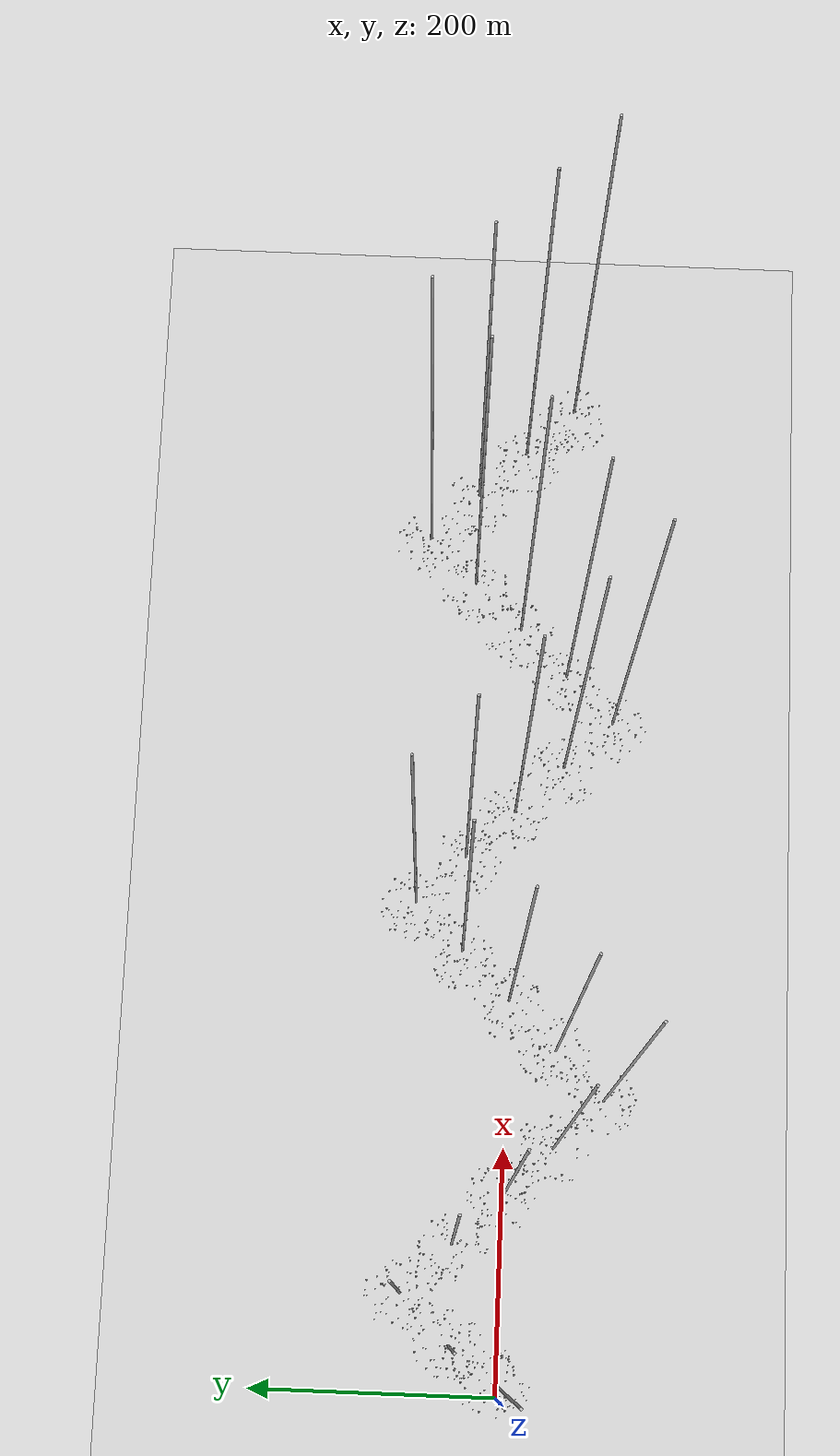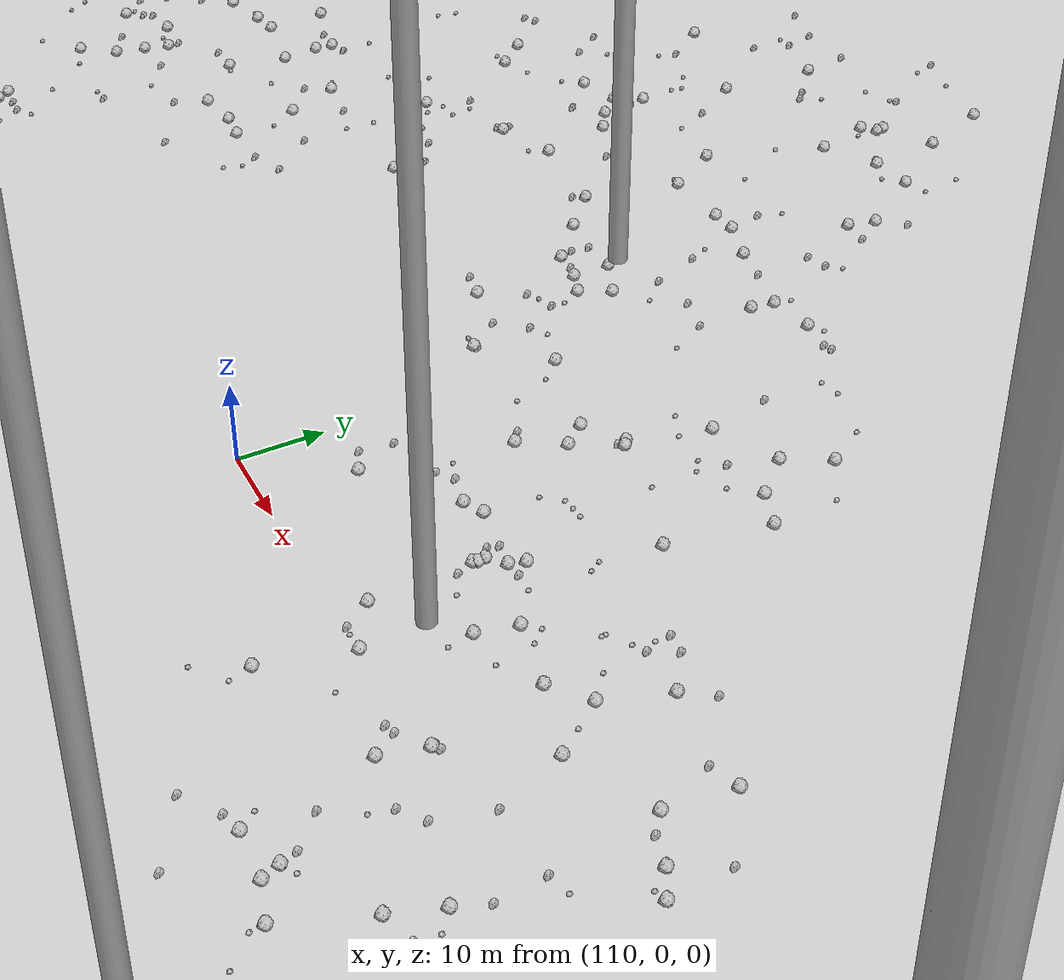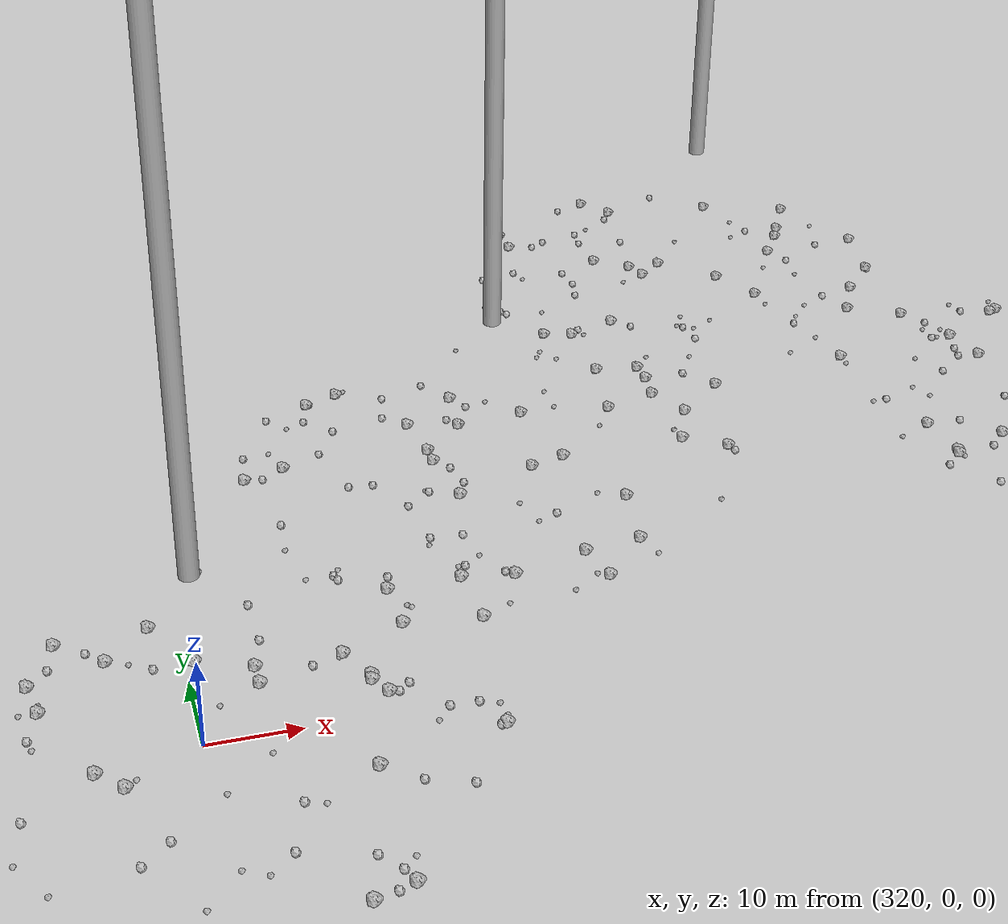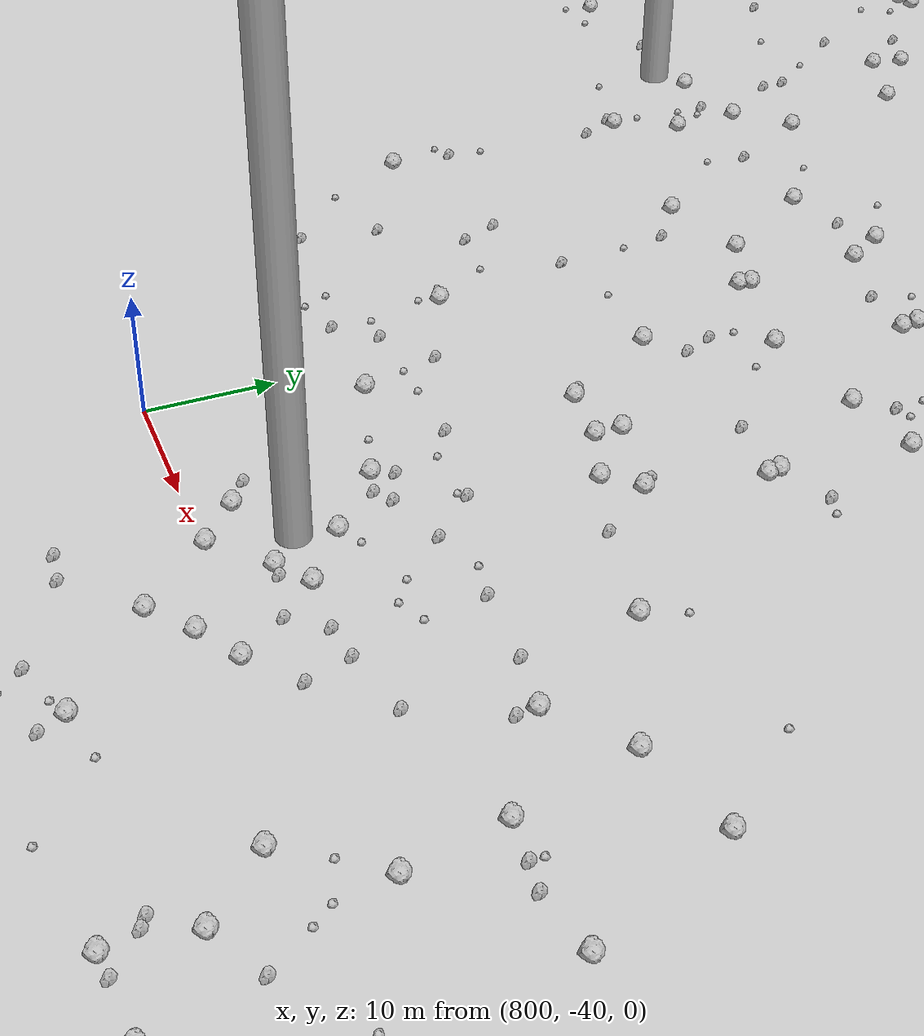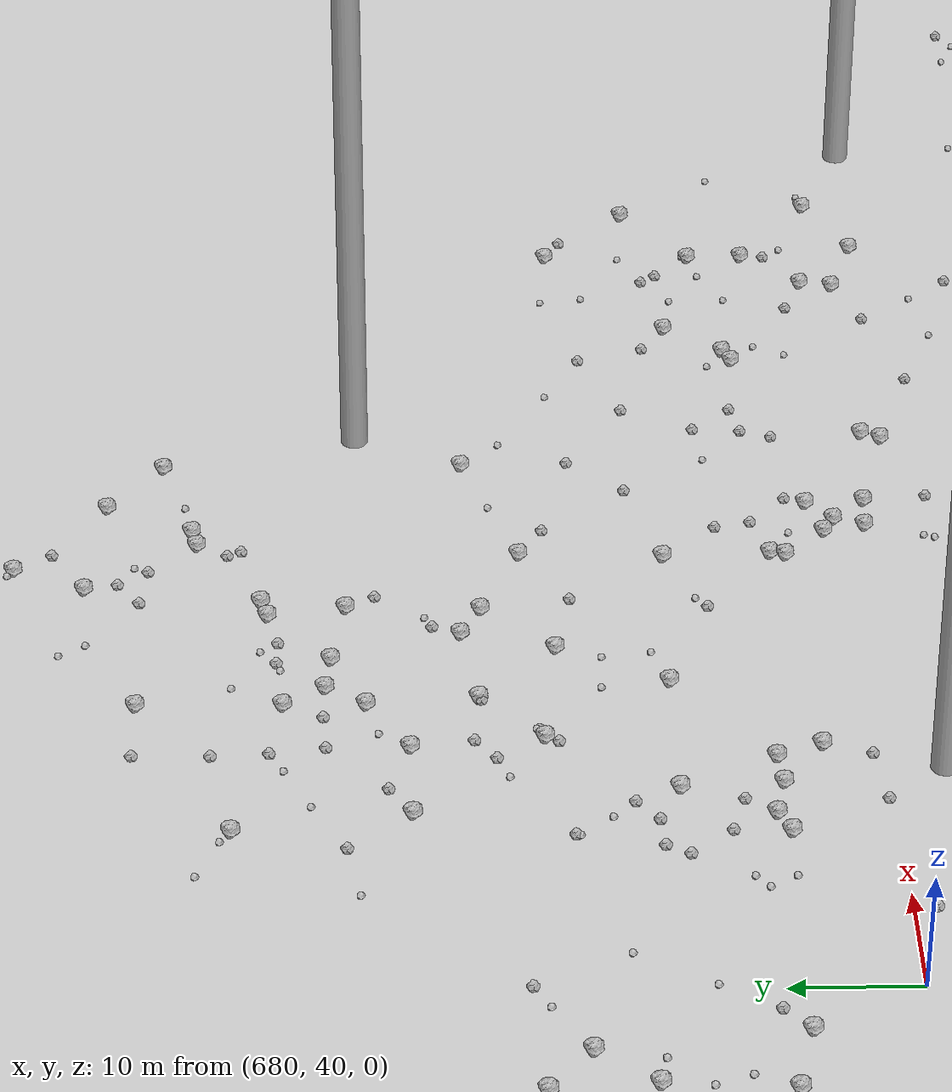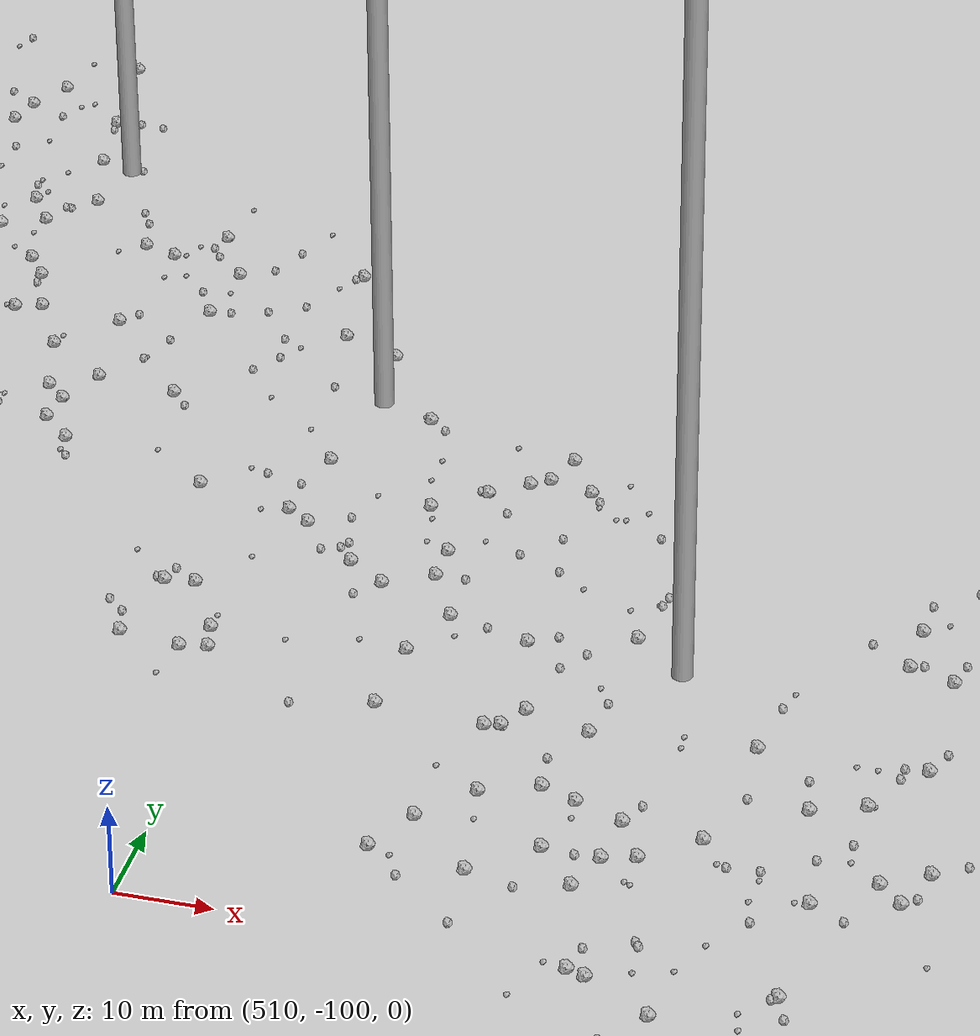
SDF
<sdf version="1.6">
 <world name="default">
  <include><uri>model://custom_ground</uri></include>
  <include><uri>model://sun</uri></include>
  <spherical_coordinates>
   <surface_model>EARTH_WGS84</surface_model>
   <latitude_deg>38.161479</latitude_deg>
   <longitude_deg>-122.454630</longitude_deg>
   <elevation>488.0</elevation>
   <heading_deg>90</heading_deg>
  </spherical_coordinates>
  <model name="rock1_0_0">
   <include><uri>model://rock1</uri><pose>-8.614815972260747 -2.031777418724097 0.5 0 0 0</pose></include>
  </model>
  <model name="rock1_0_1">
   <include><uri>model://rock1</uri><pose>-7.78394422322534 -6.519286319149742 0.5 0 0 0</pose></include>
  </model>
  <model name="rock1_0_2">
   <include><uri>model://rock1</uri><pose>16.450575903881585 26.097308537836838 0.5 0 0 0</pose></include>
  </model>
  <model name="rock1_0_3">
   <include><uri>model://rock1</uri><pose>25.048286998333765 -13.57424045054633 0.5 0 0 0</pose></include>
  </model>
  <model name="rock1_0_4">
   <include><uri>model://rock1</uri><pose>30.845028973610283 -1.8283044203259138 0.5 0 0 0</pose></include>
  </model>
  <model name="rock1_0_5">
   <include><uri>model://rock1</uri><pose>31.105628573079557 -9.634798838016849 0.5 0 0 0</pose></include>
  </model>
  <model name="rock1_0_6">
   <include><uri>model://rock1</uri><pose>1.2116098737961067 -9.155087053678479 0.5 0 0 0</pose></include>
  </model>
  <model name="rock1_0_7">
   <include><uri>model://rock1</uri><pose>20.60094537308914 -0.7698538696838746 0.5 0 0 0</pose></include>
  </model>
  <model name="rock1_0_8">
   <include><uri>model://rock1</uri><pose>-11.111936646972662 12.696370638636132 0.5 0 0 0</pose></include>
  </model>
  <model name="rock1_0_9">
   <include><uri>model://rock1</uri><pose>29.94744842816656 -0.3418322745827602 0.5 0 0 0</pose></include>
  </model>
  <model name="rock1_0_10">
   <include><uri>model://rock1</uri><pose>33.65161738342316 -4.433969054398069 0.5 0 0 0</pose></include>
  </model>
  <model name="rock1_0_11">
   <include><uri>model://rock1</uri><pose>-1.990939021658189 18.294187346339847 0.5 0 0 0</pose></include>
  </model>
  <model name="rock1_0_12">
   <include><uri>model://rock1</uri><pose>26.979606332138225 15.300556889000553 0.5 0 0 0</pose></include>
  </model>
  <model name="rock1_0_13">
   <include><uri>model://rock1</uri><pose>11.461669302039844 28.328962852112078 0.5 0 0 0</pose></include>
  </model>
  <model name="rock1_0_14">
   <include><uri>model://rock1</uri><pose>-3.2583402944482778 8.331019267700817 0.5 0 0 0</pose></include>
  </model>
  <model name="rock1_0_15">
   <include><uri>model://rock1</uri><pose>27.691527248052424 18.947970701960756 0.5 0 0 0</pose></include>
  </model>
  <model name="rock1_0_16">
   <include><uri>model://rock1</uri><pose>11.846975142518822 0.8019712065095135 0.5 0 0 0</pose></include>
  </model>
  <model name="rock1_0_17">
   <include><uri>model://rock1</uri><pose>18.648989399496777 -14.463767348111897 0.5 0 0 0</pose></include>
  </model>
  <model name="rock1_0_18">
   <include><uri>model://rock1</uri><pose>-9.455360737750013 -7.9521600681284355 0.5 0 0 0</pose></include>
  </model>
  <model name="rock1_0_19">
   <include><uri>model://rock1</uri><pose>7.245304161462027 24.990108508983013 0.5 0 0 0</pose></include>
  </model>
  <model name="rock1_0_20">
   <include><uri>model://rock1</uri><pose>-2.770140659580356 -4.511709650625917 0.5 0 0 0</pose></include>
  </model>
  <model name="rock1_0_21">
   <include><uri>model://rock1</uri><pose>22.31715483982051 -13.927593068678306 0.5 0 0 0</pose></include>
  </model>
  <model name="rock1_0_22">
   <include><uri>model://rock1</uri><pose>24.03499033692549 23.41785101547471 0.5 0 0 0</pose></include>
  </model>
  <model name="rock1_0_23">
   <include><uri>model://rock1</uri><pose>24.071305839644992 11.341626411790493 0.5 0 0 0</pose></include>
  </model>
  <model name="rock1_0_24">
   <include><uri>model://rock1</uri><pose>28.424665338773018 21.987338085395763 0.5 0 0 0</pose></include>
  </model>
  <model name="rock1_0_25">
   <include><uri>model://rock1</uri><pose>1.1732346758293772 -7.581657074117533 0.5 0 0 0</pose></include>
  </model>
  <model name="rock1_0_26">
   <include><uri>model://rock1</uri><pose>32.13419248268533 -4.464479660629902 0.5 0 0 0</pose></include>
  </model>
  <model name="rock2_0_0">
   <include><uri>model://rock2</uri><pose>14.409209959312022 27.321310593781483 0.3 0 0 0</pose></include>
  </model>
  <model name="rock2_0_1">
   <include><uri>model://rock2</uri><pose>20.81249336249276 -8.907072935852863 0.3 0 0 0</pose></include>
  </model>
  <model name="rock2_0_2">
   <include><uri>model://rock2</uri><pose>13.579138084592742 -7.8661428868274434 0.3 0 0 0</pose></include>
  </model>
  <model name="rock2_0_3">
   <include><uri>model://rock2</uri><pose>36.67901477001802 10.16250796611451 0.3 0 0 0</pose></include>
  </model>
  <model name="rock2_0_4">
   <include><uri>model://rock2</uri><pose>9.420434825224145 -27.113929422374554 0.3 0 0 0</pose></include>
  </model>
  <model name="rock2_0_5">
   <include><uri>model://rock2</uri><pose>29.055174253543413 -10.397592668865279 0.3 0 0 0</pose></include>
  </model>
  <model name="rock2_0_6">
   <include><uri>model://rock2</uri><pose>-1.5424966038495285 -8.778317953621343 0.3 0 0 0</pose></include>
  </model>
  <model name="rock2_0_7">
   <include><uri>model://rock2</uri><pose>-6.866722520114932 -14.863897702726948 0.3 0 0 0</pose></include>
  </model>
  <model name="rock2_0_8">
   <include><uri>model://rock2</uri><pose>-5.284800351336141 25.746670673359326 0.3 0 0 0</pose></include>
  </model>
  <model name="rock2_0_9">
   <include><uri>model://rock2</uri><pose>6.034992084528092 -21.36931022967329 0.3 0 0 0</pose></include>
  </model>
  <model name="rock2_0_10">
   <include><uri>model://rock2</uri><pose>12.45413126486983 -21.95559689869395 0.3 0 0 0</pose></include>
  </model>
  <model name="rock2_0_11">
   <include><uri>model://rock2</uri><pose>23.392275936064337 17.259120297020047 0.3 0 0 0</pose></include>
  </model>
  <model name="rock2_0_12">
   <include><uri>model://rock2</uri><pose>6.706672027791207 24.399355450046684 0.3 0 0 0</pose></include>
  </model>
  <model name="rock2_0_13">
   <include><uri>model://rock2</uri><pose>-5.520248896988441 -11.962757252780051 0.3 0 0 0</pose></include>
  </model>
  <model name="rock2_0_14">
   <include><uri>model://rock2</uri><pose>32.36767726548033 -0.49863255828552155 0.3 0 0 0</pose></include>
  </model>
  <model name="rock2_0_15">
   <include><uri>model://rock2</uri><pose>7.976211280331039 -3.6601295426017693 0.3 0 0 0</pose></include>
  </model>
  <model name="rock2_0_16">
   <include><uri>model://rock2</uri><pose>3.2909511551260877 12.146163806576546 0.3 0 0 0</pose></include>
  </model>
  <model name="rock2_0_17">
   <include><uri>model://rock2</uri><pose>14.652089541056739 25.636717222694067 0.3 0 0 0</pose></include>
  </model>
  <model name="rock2_0_18">
   <include><uri>model://rock2</uri><pose>33.115382564736734 -9.729900189575268 0.3 0 0 0</pose></include>
  </model>
  <model name="rock2_0_19">
   <include><uri>model://rock2</uri><pose>-1.1944686600937544 21.324705453570026 0.3 0 0 0</pose></include>
  </model>
  <model name="rock2_0_20">
   <include><uri>model://rock2</uri><pose>-15.290927961530883 -1.062250149351783 0.3 0 0 0</pose></include>
  </model>
  <model name="rock2_0_21">
   <include><uri>model://rock2</uri><pose>-0.7980286664748029 -24.892618927561394 0.3 0 0 0</pose></include>
  </model>
  <model name="rock2_0_22">
   <include><uri>model://rock2</uri><pose>11.208407206872256 3.544744424036722 0.3 0 0 0</pose></include>
  </model>
  <model name="rock2_0_23">
   <include><uri>model://rock2</uri><pose>-0.393970821190333 -16.252222595322515 0.3 0 0 0</pose></include>
  </model>
  <model name="rock2_0_24">
   <include><uri>model://rock2</uri><pose>34.36187231754576 -0.5653677214267603 0.3 0 0 0</pose></include>
  </model>
  <model name="rock2_0_25">
   <include><uri>model://rock2</uri><pose>-4.2213651732602955 21.133441623766068 0.3 0 0 0</pose></include>
  </model>
  <model name="rock2_0_26">
   <include><uri>model://rock2</uri><pose>5.830619326409529 9.015501080379892 0.3 0 0 0</pose></include>
  </model>
  <model name="rock3_0_0">
   <include><uri>model://rock3</uri><pose>-9.57347981255934 17.587470287744665 0.2 0 0 0</pose></include>
  </model>
  <model name="rock3_0_1">
   <include><uri>model://rock3</uri><pose>12.160525751083718 -19.26861525867066 0.2 0 0 0</pose></include>
  </model>
  <model name="rock3_0_2">
   <include><uri>model://rock3</uri><pose>-4.643859127121804 -23.313236719334803 0.2 0 0 0</pose></include>
  </model>
  <model name="rock3_0_3">
   <include><uri>model://rock3</uri><pose>19.517468401838087 7.540364194830211 0.2 0 0 0</pose></include>
  </model>
  <model name="rock3_0_4">
   <include><uri>model://rock3</uri><pose>-1.3547753206492956 -3.8376332944933367 0.2 0 0 0</pose></include>
  </model>
  <model name="rock3_0_5">
   <include><uri>model://rock3</uri><pose>26.359345595988188 -9.170765084433505 0.2 0 0 0</pose></include>
  </model>
  <model name="rock3_0_6">
   <include><uri>model://rock3</uri><pose>3.00697459490409 -23.020118580790587 0.2 0 0 0</pose></include>
  </model>
  <model name="rock3_0_7">
   <include><uri>model://rock3</uri><pose>37.59665895831816 -6.690484115418688 0.2 0 0 0</pose></include>
  </model>
  <model name="rock3_0_8">
   <include><uri>model://rock3</uri><pose>11.013151965692153 26.267422147189137 0.2 0 0 0</pose></include>
  </model>
  <model name="rock3_0_9">
   <include><uri>model://rock3</uri><pose>-4.781701689016163 -22.555796898171003 0.2 0 0 0</pose></include>
  </model>
  <model name="rock3_0_10">
   <include><uri>model://rock3</uri><pose>-6.432179987555308 -10.6481393354555 0.2 0 0 0</pose></include>
  </model>
  <model name="rock3_0_11">
   <include><uri>model://rock3</uri><pose>0.7619397353481574 3.7719927214673774 0.2 0 0 0</pose></include>
  </model>
  <model name="rock3_0_12">
   <include><uri>model://rock3</uri><pose>27.05921769609889 10.138226299110826 0.2 0 0 0</pose></include>
  </model>
  <model name="rock3_0_13">
   <include><uri>model://rock3</uri><pose>12.464905186362358 15.761634734136777 0.2 0 0 0</pose></include>
  </model>
  <model name="rock3_0_14">
   <include><uri>model://rock3</uri><pose>31.75561887504726 -7.617480804749036 0.2 0 0 0</pose></include>
  </model>
  <model name="rock3_0_15">
   <include><uri>model://rock3</uri><pose>33.965838126139396 -3.3157871673488124 0.2 0 0 0</pose></include>
  </model>
  <model name="rock3_0_16">
   <include><uri>model://rock3</uri><pose>13.628414845619027 13.50865715815025 0.2 0 0 0</pose></include>
  </model>
  <model name="rock3_0_17">
   <include><uri>model://rock3</uri><pose>25.878285093628676 22.08182694930624 0.2 0 0 0</pose></include>
  </model>
  <model name="rock3_0_18">
   <include><uri>model://rock3</uri><pose>31.513431810580045 4.999011129135084 0.2 0 0 0</pose></include>
  </model>
  <model name="rock3_0_19">
   <include><uri>model://rock3</uri><pose>-0.9165579341929835 -25.332729046702582 0.2 0 0 0</pose></include>
  </model>
  <model name="rock3_0_20">
   <include><uri>model://rock3</uri><pose>35.912460187429254 0.7814511170915033 0.2 0 0 0</pose></include>
  </model>
  <model name="rock3_0_21">
   <include><uri>model://rock3</uri><pose>35.584648787870876 -3.247997542572268 0.2 0 0 0</pose></include>
  </model>
  <model name="rock3_0_22">
   <include><uri>model://rock3</uri><pose>1.562872503831553 -3.509528381123875 0.2 0 0 0</pose></include>
  </model>
  <model name="rock3_0_23">
   <include><uri>model://rock3</uri><pose>34.57702822619992 10.042208773090877 0.2 0 0 0</pose></include>
  </model>
  <model name="rock3_0_24">
   <include><uri>model://rock3</uri><pose>-10.702338311997101 -12.358817724157245 0.2 0 0 0</pose></include>
  </model>
  <model name="rock3_0_25">
   <include><uri>model://rock3</uri><pose>3.3235253661282833 -24.19275873560507 0.2 0 0 0</pose></include>
  </model>
  <model name="rock3_0_26">
   <include><uri>model://rock3</uri><pose>-0.5039321731789101 18.610135452391475 0.2 0 0 0</pose></include>
  </model>
  <model name="rock1_1_0">
   <include><uri>model://rock1</uri><pose>36.50786229770451 27.43962209818818 0.5 0 0 0</pose></include>
  </model>
  <model name="rock1_1_1">
   <include><uri>model://rock1</uri><pose>33.8150879458365 66.42785583621605 0.5 0 0 0</pose></include>
  </model>
  <model name="rock1_1_2">
   <include><uri>model://rock1</uri><pose>56.102916490459066 46.685805847751034 0.5 0 0 0</pose></include>
  </model>
  <model name="rock1_1_3">
   <include><uri>model://rock1</uri><pose>21.216627223303007 56.58086102671262 0.5 0 0 0</pose></include>
  </model>
  <model name="rock1_1_4">
   <include><uri>model://rock1</uri><pose>38.099710627776005 34.58509904843109 0.5 0 0 0</pose></include>
  </model>
  <model name="rock1_1_5">
   <include><uri>model://rock1</uri><pose>21.838187916644856 40.045371897270044 0.5 0 0 0</pose></include>
  </model>
  <model name="rock1_1_6">
   <include><uri>model://rock1</uri><pose>48.36307667989648 22.76902874414228 0.5 0 0 0</pose></include>
  </model>
  <model name="rock1_1_7">
   <include><uri>model://rock1</uri><pose>51.757867287843524 59.92068973897978 0.5 0 0 0</pose></include>
  </model>
  <model name="rock1_1_8">
   <include><uri>model://rock1</uri><pose>29.763653175783794 43.09503890912119 0.5 0 0 0</pose></include>
  </model>
  <model name="rock1_1_9">
   <include><uri>model://rock1</uri><pose>67.68923982868338 36.993929852494716 0.5 0 0 0</pose></include>
  </model>
  <model name="rock1_1_10">
   <include><uri>model://rock1</uri><pose>51.926402694563265 22.45191474502782 0.5 0 0 0</pose></include>
  </model>
  <model name="rock1_1_11">
   <include><uri>model://rock1</uri><pose>16.236038758881858 31.703570664441564 0.5 0 0 0</pose></include>
  </model>
  <model name="rock1_1_12">
   <include><uri>model://rock1</uri><pose>37.66824158341361 39.080829600653644 0.5 0 0 0</pose></include>
  </model>
  <model name="rock1_1_13">
   <include><uri>model://rock1</uri><pose>15.070651266079906 47.38696599912788 0.5 0 0 0</pose></include>
  </model>
  <model name="rock1_1_14">
   <include><uri>model://rock1</uri><pose>47.62518853704741 37.108303671575925 0.5 0 0 0</pose></include>
  </model>
  <model name="rock1_1_15">
   <include><uri>model://rock1</uri><pose>65.95168401484918 52.784807064027426 0.5 0 0 0</pose></include>
  </model>
  <model name="rock1_1_16">
   <include><uri>model://rock1</uri><pose>20.59334624771239 33.79030975294356 0.5 0 0 0</pose></include>
  </model>
  <model name="rock1_1_17">
   <include><uri>model://rock1</uri><pose>21.848496648749414 33.62610410878966 0.5 0 0 0</pose></include>
  </model>
  <model name="rock1_1_18">
   <include><uri>model://rock1</uri><pose>50.19291282778267 30.735834298444765 0.5 0 0 0</pose></include>
  </model>
  <model name="rock1_1_19">
   <include><uri>model://rock1</uri><pose>37.81615767270459 41.31824021544089 0.5 0 0 0</pose></include>
  </model>
  <model name="rock1_1_20">
   <include><uri>model://rock1</uri><pose>18.283031290121215 19.666155093228742 0.5 0 0 0</pose></include>
  </model>
  <model name="rock1_1_21">
   <include><uri>model://rock1</uri><pose>27.876629055643466 53.17863003491491 0.5 0 0 0</pose></include>
  </model>
  <model name="rock1_1_22">
   <include><uri>model://rock1</uri><pose>27.02696599431435 35.13260392106166 0.5 0 0 0</pose></include>
  </model>
  <model name="rock1_1_23">
   <include><uri>model://rock1</uri><pose>30.16188699276028 35.797447661802394 0.5 0 0 0</pose></include>
  </model>
  <model name="rock1_1_24">
   <include><uri>model://rock1</uri><pose>48.6753751135182 63.28202877685351 0.5 0 0 0</pose></include>
  </model>
  <model name="rock1_1_25">
   <include><uri>model://rock1</uri><pose>60.936441055525435 42.82027902151856 0.5 0 0 0</pose></include>
  </model>
  <model name="rock1_1_26">
   <include><uri>model://rock1</uri><pose>43.31632905696491 21.876086585018392 0.5 0 0 0</pose></include>
  </model>
  <model name="rock2_1_0">
   <include><uri>model://rock2</uri><pose>52.91610029449679 36.57714399249733 0.3 0 0 0</pose></include>
  </model>
  <model name="rock2_1_1">
   <include><uri>model://rock2</uri><pose>34.751585678101875 41.41723964476705 0.3 0 0 0</pose></include>
  </model>
  <model name="rock2_1_2">
   <include><uri>model://rock2</uri><pose>45.89472571625643 34.091787411679945 0.3 0 0 0</pose></include>
  </model>
  <model name="rock2_1_3">
   <include><uri>model://rock2</uri><pose>61.52193518709539 24.326374096706434 0.3 0 0 0</pose></include>
  </model>
  <model name="rock2_1_4">
   <include><uri>model://rock2</uri><pose>57.02526611781271 29.49121362614211 0.3 0 0 0</pose></include>
  </model>
  <model name="rock2_1_5">
   <include><uri>model://rock2</uri><pose>19.213661567775407 30.067364267972682 0.3 0 0 0</pose></include>
  </model>
  <model name="rock2_1_6">
   <include><uri>model://rock2</uri><pose>64.35849009844597 43.22528559149914 0.3 0 0 0</pose></include>
  </model>
  <model name="rock2_1_7">
   <include><uri>model://rock2</uri><pose>15.63415824249578 22.563018105254272 0.3 0 0 0</pose></include>
  </model>
  <model name="rock2_1_8">
   <include><uri>model://rock2</uri><pose>49.60158495577053 13.79026035053412 0.3 0 0 0</pose></include>
  </model>
  <model name="rock2_1_9">
   <include><uri>model://rock2</uri><pose>67.8947813949685 41.12011543453848 0.3 0 0 0</pose></include>
  </model>
  <model name="rock2_1_10">
   <include><uri>model://rock2</uri><pose>32.78103124873517 27.283303794206812 0.3 0 0 0</pose></include>
  </model>
  <model name="rock2_1_11">
   <include><uri>model://rock2</uri><pose>19.430941412701948 21.65672001400191 0.3 0 0 0</pose></include>
  </model>
  <model name="rock2_1_12">
   <include><uri>model://rock2</uri><pose>64.99498287558315 52.39573252490915 0.3 0 0 0</pose></include>
  </model>
  <model name="rock2_1_13">
   <include><uri>model://rock2</uri><pose>13.414356387489537 33.243010555521714 0.3 0 0 0</pose></include>
  </model>
  <model name="rock2_1_14">
   <include><uri>model://rock2</uri><pose>41.50800681660719 17.94637816722438 0.3 0 0 0</pose></include>
  </model>
  <model name="rock2_1_15">
   <include><uri>model://rock2</uri><pose>57.69045743380996 22.65692849632247 0.3 0 0 0</pose></include>
  </model>
  <model name="rock2_1_16">
   <include><uri>model://rock2</uri><pose>42.64567518146464 67.23076895019453 0.3 0 0 0</pose></include>
  </model>
  <model name="rock2_1_17">
   <include><uri>model://rock2</uri><pose>14.98070135948508 49.91859762411246 0.3 0 0 0</pose></include>
  </model>
  <model name="rock2_1_18">
   <include><uri>model://rock2</uri><pose>61.017001768284835 43.745838520916536 0.3 0 0 0</pose></include>
  </model>
  <model name="rock2_1_19">
   <include><uri>model://rock2</uri><pose>28.22600307968017 23.43232975031445 0.3 0 0 0</pose></include>
  </model>
  <model name="rock2_1_20">
   <include><uri>model://rock2</uri><pose>20.089050966892987 22.742911237819264 0.3 0 0 0</pose></include>
  </model>
  <model name="rock2_1_21">
   <include><uri>model://rock2</uri><pose>32.47014395437304 19.424330977201475 0.3 0 0 0</pose></include>
  </model>
  <model name="rock2_1_22">
   <include><uri>model://rock2</uri><pose>39.53215319315308 42.20549003094737 0.3 0 0 0</pose></include>
  </model>
  <model name="rock2_1_23">
   <include><uri>model://rock2</uri><pose>44.00801922958878 68.15274431789712 0.3 0 0 0</pose></include>
  </model>
  <model name="rock2_1_24">
   <include><uri>model://rock2</uri><pose>14.663792465219604 29.032122174669436 0.3 0 0 0</pose></include>
  </model>
  <model name="rock2_1_25">
   <include><uri>model://rock2</uri><pose>57.89446510761523 51.9963054460528 0.3 0 0 0</pose></include>
  </model>
  <model name="rock2_1_26">
   <include><uri>model://rock2</uri><pose>22.191278122952518 48.280577357951884 0.3 0 0 0</pose></include>
  </model>
  <model name="rock3_1_0">
   <include><uri>model://rock3</uri><pose>50.43366420533463 49.61427555213427 0.2 0 0 0</pose></include>
  </model>
  <model name="rock3_1_1">
   <include><uri>model://rock3</uri><pose>14.853140945311747 38.90169783149864 0.2 0 0 0</pose></include>
  </model>
  <model name="rock3_1_2">
   <include><uri>model://rock3</uri><pose>45.86553418960879 37.926697882509615 0.2 0 0 0</pose></include>
  </model>
  <model name="rock3_1_3">
   <include><uri>model://rock3</uri><pose>57.95048569296175 18.342835056606837 0.2 0 0 0</pose></include>
  </model>
  <model name="rock3_1_4">
   <include><uri>model://rock3</uri><pose>47.893374656362965 45.00136784288513 0.2 0 0 0</pose></include>
  </model>
  <model name="rock3_1_5">
   <include><uri>model://rock3</uri><pose>59.64567954758428 48.7276933520162 0.2 0 0 0</pose></include>
  </model>
  <model name="rock3_1_6">
   <include><uri>model://rock3</uri><pose>59.31642457906031 51.240910172124586 0.2 0 0 0</pose></include>
  </model>
  <model name="rock3_1_7">
   <include><uri>model://rock3</uri><pose>37.243151582813056 59.55995383398631 0.2 0 0 0</pose></include>
  </model>
  <model name="rock3_1_8">
   <include><uri>model://rock3</uri><pose>21.818318603324855 45.1123973643089 0.2 0 0 0</pose></include>
  </model>
  <model name="rock3_1_9">
   <include><uri>model://rock3</uri><pose>51.98942140359141 27.434971195273622 0.2 0 0 0</pose></include>
  </model>
  <model name="rock3_1_10">
   <include><uri>model://rock3</uri><pose>54.88145012509798 61.626072135710594 0.2 0 0 0</pose></include>
  </model>
  <model name="rock3_1_11">
   <include><uri>model://rock3</uri><pose>42.638295218931695 30.783846859438476 0.2 0 0 0</pose></include>
  </model>
  <model name="rock3_1_12">
   <include><uri>model://rock3</uri><pose>36.25278038540679 16.740234689465645 0.2 0 0 0</pose></include>
  </model>
  <model name="rock3_1_13">
   <include><uri>model://rock3</uri><pose>17.749056361662177 20.98250427808525 0.2 0 0 0</pose></include>
  </model>
  <model name="rock3_1_14">
   <include><uri>model://rock3</uri><pose>37.414480584949004 27.225423669018994 0.2 0 0 0</pose></include>
  </model>
  <model name="rock3_1_15">
   <include><uri>model://rock3</uri><pose>28.11159200896357 50.59769212762259 0.2 0 0 0</pose></include>
  </model>
  <model name="rock3_1_16">
   <include><uri>model://rock3</uri><pose>25.264355676263552 35.39977185246632 0.2 0 0 0</pose></include>
  </model>
  <model name="rock3_1_17">
   <include><uri>model://rock3</uri><pose>57.38367088891698 48.40019912234328 0.2 0 0 0</pose></include>
  </model>
  <model name="rock3_1_18">
   <include><uri>model://rock3</uri><pose>36.76926591175557 57.16913294293619 0.2 0 0 0</pose></include>
  </model>
  <model name="rock3_1_19">
   <include><uri>model://rock3</uri><pose>39.17524288570327 46.07296741593553 0.2 0 0 0</pose></include>
  </model>
  <model name="rock3_1_20">
   <include><uri>model://rock3</uri><pose>57.73814148713493 46.06055829597468 0.2 0 0 0</pose></include>
  </model>
  <model name="rock3_1_21">
   <include><uri>model://rock3</uri><pose>29.98213032578419 67.53875754778916 0.2 0 0 0</pose></include>
  </model>
  <model name="rock3_1_22">
   <include><uri>model://rock3</uri><pose>58.603102278354385 20.616053964131282 0.2 0 0 0</pose></include>
  </model>
  <model name="rock3_1_23">
   <include><uri>model://rock3</uri><pose>56.85591828495773 39.005262710832355 0.2 0 0 0</pose></include>
  </model>
  <model name="rock3_1_24">
   <include><uri>model://rock3</uri><pose>56.64279219350741 35.38953223051018 0.2 0 0 0</pose></include>
  </model>
  <model name="rock3_1_25">
   <include><uri>model://rock3</uri><pose>26.69649116708751 64.5847746649506 0.2 0 0 0</pose></include>
  </model>
  <model name="rock3_1_26">
   <include><uri>model://rock3</uri><pose>49.55213347145343 59.826995107680055 0.2 0 0 0</pose></include>
  </model>
  <model name="rock1_2_0">
   <include><uri>model://rock1</uri><pose>97.07315498803572 67.96375808606908 0.5 0 0 0</pose></include>
  </model>
  <model name="rock1_2_1">
   <include><uri>model://rock1</uri><pose>85.4493865680243 93.25630431881207 0.5 0 0 0</pose></include>
  </model>
  <model name="rock1_2_2">
   <include><uri>model://rock1</uri><pose>68.16172367146757 66.02322722621147 0.5 0 0 0</pose></include>
  </model>
  <model name="rock1_2_3">
   <include><uri>model://rock1</uri><pose>89.25625641543641 107.67066175127344 0.5 0 0 0</pose></include>
  </model>
  <model name="rock1_2_4">
   <include><uri>model://rock1</uri><pose>86.1690728935373 66.70130114385125 0.5 0 0 0</pose></include>
  </model>
  <model name="rock1_2_5">
   <include><uri>model://rock1</uri><pose>86.74783077026498 95.69775641973224 0.5 0 0 0</pose></include>
  </model>
  <model name="rock1_2_6">
   <include><uri>model://rock1</uri><pose>72.75996341857274 55.767445942585255 0.5 0 0 0</pose></include>
  </model>
  <model name="rock1_2_7">
   <include><uri>model://rock1</uri><pose>88.20951092642996 51.30836950828847 0.5 0 0 0</pose></include>
  </model>
  <model name="rock1_2_8">
   <include><uri>model://rock1</uri><pose>82.4043028853504 72.79553977900294 0.5 0 0 0</pose></include>
  </model>
  <model name="rock1_2_9">
   <include><uri>model://rock1</uri><pose>70.08005557162221 82.62897413287033 0.5 0 0 0</pose></include>
  </model>
  <model name="rock1_2_10">
   <include><uri>model://rock1</uri><pose>60.76847445933616 66.86206253088264 0.5 0 0 0</pose></include>
  </model>
  <model name="rock1_2_11">
   <include><uri>model://rock1</uri><pose>93.11812710485393 90.81998901195493 0.5 0 0 0</pose></include>
  </model>
  <model name="rock1_2_12">
   <include><uri>model://rock1</uri><pose>103.45874719867658 84.07660769122741 0.5 0 0 0</pose></include>
  </model>
  <model name="rock1_2_13">
   <include><uri>model://rock1</uri><pose>102.68644002106856 80.68687739367137 0.5 0 0 0</pose></include>
  </model>
  <model name="rock1_2_14">
   <include><uri>model://rock1</uri><pose>70.97278509092925 94.35142144504441 0.5 0 0 0</pose></include>
  </model>
  <model name="rock1_2_15">
   <include><uri>model://rock1</uri><pose>83.65704910815626 55.27187378720988 0.5 0 0 0</pose></include>
  </model>
  <model name="rock1_2_16">
   <include><uri>model://rock1</uri><pose>92.38341510791764 99.4216177169042 0.5 0 0 0</pose></include>
  </model>
  <model name="rock1_2_17">
   <include><uri>model://rock1</uri><pose>56.30299706483026 85.61585856910438 0.5 0 0 0</pose></include>
  </model>
  <model name="rock1_2_18">
   <include><uri>model://rock1</uri><pose>86.90944631983612 94.75740324671249 0.5 0 0 0</pose></include>
  </model>
  <model name="rock1_2_19">
   <include><uri>model://rock1</uri><pose>65.6979343188789 68.5745444435666 0.5 0 0 0</pose></include>
  </model>
  <model name="rock1_2_20">
   <include><uri>model://rock1</uri><pose>87.17076929486225 86.85029204903765 0.5 0 0 0</pose></include>
  </model>
  <model name="rock1_2_21">
   <include><uri>model://rock1</uri><pose>98.12098971505733 91.77949489298854 0.5 0 0 0</pose></include>
  </model>
  <model name="rock1_2_22">
   <include><uri>model://rock1</uri><pose>67.4481009864183 71.91285286277635 0.5 0 0 0</pose></include>
  </model>
  <model name="rock1_2_23">
   <include><uri>model://rock1</uri><pose>67.89897230074865 69.52770804448599 0.5 0 0 0</pose></include>
  </model>
  <model name="rock1_2_24">
   <include><uri>model://rock1</uri><pose>70.91246149462252 64.32566604204621 0.5 0 0 0</pose></include>
  </model>
  <model name="rock1_2_25">
   <include><uri>model://rock1</uri><pose>93.94163131622543 67.54548980501664 0.5 0 0 0</pose></include>
  </model>
  <model name="rock1_2_26">
   <include><uri>model://rock1</uri><pose>102.16881327218177 66.62485891511272 0.5 0 0 0</pose></include>
  </model>
  <model name="rock2_2_0">
   <include><uri>model://rock2</uri><pose>105.73123822680492 80.82013775341778 0.3 0 0 0</pose></include>
  </model>
  <model name="rock2_2_1">
   <include><uri>model://rock2</uri><pose>88.50087099003484 57.539409916893234 0.3 0 0 0</pose></include>
  </model>
  <model name="rock2_2_2">
   <include><uri>model://rock2</uri><pose>62.84385220810181 90.94871823401769 0.3 0 0 0</pose></include>
  </model>
  <model name="rock2_2_3">
   <include><uri>model://rock2</uri><pose>63.505337238585824 99.02441545116407 0.3 0 0 0</pose></include>
  </model>
  <model name="rock2_2_4">
   <include><uri>model://rock2</uri><pose>108.34833205098106 74.10076406025757 0.3 0 0 0</pose></include>
  </model>
  <model name="rock2_2_5">
   <include><uri>model://rock2</uri><pose>82.77997269212963 53.936721994259514 0.3 0 0 0</pose></include>
  </model>
  <model name="rock2_2_6">
   <include><uri>model://rock2</uri><pose>82.1234838600667 100.70789282377945 0.3 0 0 0</pose></include>
  </model>
  <model name="rock2_2_7">
   <include><uri>model://rock2</uri><pose>105.60120927431592 87.26644974715887 0.3 0 0 0</pose></include>
  </model>
  <model name="rock2_2_8">
   <include><uri>model://rock2</uri><pose>65.13159682325306 62.909308600688526 0.3 0 0 0</pose></include>
  </model>
  <model name="rock2_2_9">
   <include><uri>model://rock2</uri><pose>51.065494164088896 73.28503389468416 0.3 0 0 0</pose></include>
  </model>
  <model name="rock2_2_10">
   <include><uri>model://rock2</uri><pose>65.52952675831791 53.80485990011535 0.3 0 0 0</pose></include>
  </model>
  <model name="rock2_2_11">
   <include><uri>model://rock2</uri><pose>76.0835840834857 90.05578281384405 0.3 0 0 0</pose></include>
  </model>
  <model name="rock2_2_12">
   <include><uri>model://rock2</uri><pose>70.00128941105547 99.9484163364352 0.3 0 0 0</pose></include>
  </model>
  <model name="rock2_2_13">
   <include><uri>model://rock2</uri><pose>63.03489980239258 71.84608878750642 0.3 0 0 0</pose></include>
  </model>
  <model name="rock2_2_14">
   <include><uri>model://rock2</uri><pose>76.69004786794456 109.54462020425339 0.3 0 0 0</pose></include>
  </model>
  <model name="rock2_2_15">
   <include><uri>model://rock2</uri><pose>64.38431358097093 95.42245573144875 0.3 0 0 0</pose></include>
  </model>
  <model name="rock2_2_16">
   <include><uri>model://rock2</uri><pose>73.52421970031827 77.15479578978575 0.3 0 0 0</pose></include>
  </model>
  <model name="rock2_2_17">
   <include><uri>model://rock2</uri><pose>52.19296215304173 76.77576629303194 0.3 0 0 0</pose></include>
  </model>
  <model name="rock2_2_18">
   <include><uri>model://rock2</uri><pose>59.59028580668665 81.03002601093881 0.3 0 0 0</pose></include>
  </model>
  <model name="rock2_2_19">
   <include><uri>model://rock2</uri><pose>96.04740743358315 72.12384912451526 0.3 0 0 0</pose></include>
  </model>
  <model name="rock2_2_20">
   <include><uri>model://rock2</uri><pose>58.166996223021634 100.02042856781799 0.3 0 0 0</pose></include>
  </model>
  <model name="rock2_2_21">
   <include><uri>model://rock2</uri><pose>105.96605830078485 73.16664396897005 0.3 0 0 0</pose></include>
  </model>
  <model name="rock2_2_22">
   <include><uri>model://rock2</uri><pose>53.634654024585814 69.85271470598487 0.3 0 0 0</pose></include>
  </model>
  <model name="rock2_2_23">
   <include><uri>model://rock2</uri><pose>76.8101831121719 61.72020437689545 0.3 0 0 0</pose></include>
  </model>
  <model name="rock2_2_24">
   <include><uri>model://rock2</uri><pose>106.36251185034689 66.1679379348488 0.3 0 0 0</pose></include>
  </model>
  <model name="rock2_2_25">
   <include><uri>model://rock2</uri><pose>74.95272721188333 91.01754620284332 0.3 0 0 0</pose></include>
  </model>
  <model name="rock2_2_26">
   <include><uri>model://rock2</uri><pose>92.16724286849706 91.24644679211531 0.3 0 0 0</pose></include>
  </model>
  <model name="rock3_2_0">
   <include><uri>model://rock3</uri><pose>99.06709856628976 63.14593913826139 0.2 0 0 0</pose></include>
  </model>
  <model name="rock3_2_1">
   <include><uri>model://rock3</uri><pose>96.81238288799672 75.05061597593924 0.2 0 0 0</pose></include>
  </model>
  <model name="rock3_2_2">
   <include><uri>model://rock3</uri><pose>71.25224108893826 53.67217296530573 0.2 0 0 0</pose></include>
  </model>
  <model name="rock3_2_3">
   <include><uri>model://rock3</uri><pose>75.2496671747056 73.23401357229503 0.2 0 0 0</pose></include>
  </model>
  <model name="rock3_2_4">
   <include><uri>model://rock3</uri><pose>62.41712477176762 95.20743025071346 0.2 0 0 0</pose></include>
  </model>
  <model name="rock3_2_5">
   <include><uri>model://rock3</uri><pose>100.01496994916178 97.8586659976095 0.2 0 0 0</pose></include>
  </model>
  <model name="rock3_2_6">
   <include><uri>model://rock3</uri><pose>75.19802634617346 65.01818644156549 0.2 0 0 0</pose></include>
  </model>
  <model name="rock3_2_7">
   <include><uri>model://rock3</uri><pose>58.749274517416374 64.64410301779851 0.2 0 0 0</pose></include>
  </model>
  <model name="rock3_2_8">
   <include><uri>model://rock3</uri><pose>66.86158108402027 76.3510238387444 0.2 0 0 0</pose></include>
  </model>
  <model name="rock3_2_9">
   <include><uri>model://rock3</uri><pose>81.58973773118832 108.61400971241918 0.2 0 0 0</pose></include>
  </model>
  <model name="rock3_2_10">
   <include><uri>model://rock3</uri><pose>55.47374258069975 73.00904910467253 0.2 0 0 0</pose></include>
  </model>
  <model name="rock3_2_11">
   <include><uri>model://rock3</uri><pose>77.2395716404808 92.54168793118643 0.2 0 0 0</pose></include>
  </model>
  <model name="rock3_2_12">
   <include><uri>model://rock3</uri><pose>84.6155279540254 81.35043441648517 0.2 0 0 0</pose></include>
  </model>
  <model name="rock3_2_13">
   <include><uri>model://rock3</uri><pose>71.1966017692016 67.68068861571732 0.2 0 0 0</pose></include>
  </model>
  <model name="rock3_2_14">
   <include><uri>model://rock3</uri><pose>88.5232205775446 74.71194833655198 0.2 0 0 0</pose></include>
  </model>
  <model name="rock3_2_15">
   <include><uri>model://rock3</uri><pose>58.79895079434735 78.86218597203573 0.2 0 0 0</pose></include>
  </model>
  <model name="rock3_2_16">
   <include><uri>model://rock3</uri><pose>67.03901756639488 77.76168086819321 0.2 0 0 0</pose></include>
  </model>
  <model name="rock3_2_17">
   <include><uri>model://rock3</uri><pose>81.36545953543819 100.15922071511972 0.2 0 0 0</pose></include>
  </model>
  <model name="rock3_2_18">
   <include><uri>model://rock3</uri><pose>77.29337944148723 107.05559530491237 0.2 0 0 0</pose></include>
  </model>
  <model name="rock3_2_19">
   <include><uri>model://rock3</uri><pose>109.51933702374812 75.74491962228043 0.2 0 0 0</pose></include>
  </model>
  <model name="rock3_2_20">
   <include><uri>model://rock3</uri><pose>84.74342441035824 66.91317055162811 0.2 0 0 0</pose></include>
  </model>
  <model name="rock3_2_21">
   <include><uri>model://rock3</uri><pose>100.55088667279256 93.09608932465724 0.2 0 0 0</pose></include>
  </model>
  <model name="rock3_2_22">
   <include><uri>model://rock3</uri><pose>78.27234659314844 98.50100432556667 0.2 0 0 0</pose></include>
  </model>
  <model name="rock3_2_23">
   <include><uri>model://rock3</uri><pose>64.83638532972456 79.1937894978865 0.2 0 0 0</pose></include>
  </model>
  <model name="rock3_2_24">
   <include><uri>model://rock3</uri><pose>95.89980731928743 89.7481835214517 0.2 0 0 0</pose></include>
  </model>
  <model name="rock3_2_25">
   <include><uri>model://rock3</uri><pose>64.38002049501135 63.4602840058554 0.2 0 0 0</pose></include>
  </model>
  <model name="rock3_2_26">
   <include><uri>model://rock3</uri><pose>86.4781171269203 92.25793129527932 0.2 0 0 0</pose></include>
  </model>
  <model name="rock1_3_0">
   <include><uri>model://rock1</uri><pose>117.3344356091119 66.26222720379852 0.5 0 0 0</pose></include>
  </model>
  <model name="rock1_3_1">
   <include><uri>model://rock1</uri><pose>138.6900211683173 56.74194866518095 0.5 0 0 0</pose></include>
  </model>
  <model name="rock1_3_2">
   <include><uri>model://rock1</uri><pose>111.98728796692961 65.01504313569075 0.5 0 0 0</pose></include>
  </model>
  <model name="rock1_3_3">
   <include><uri>model://rock1</uri><pose>127.29348647351233 18.506891404762207 0.5 0 0 0</pose></include>
  </model>
  <model name="rock1_3_4">
   <include><uri>model://rock1</uri><pose>121.54224437432057 35.15180413993041 0.5 0 0 0</pose></include>
  </model>
  <model name="rock1_3_5">
   <include><uri>model://rock1</uri><pose>117.77983648741676 10.722523956095504 0.5 0 0 0</pose></include>
  </model>
  <model name="rock1_3_6">
   <include><uri>model://rock1</uri><pose>128.3990655974845 47.62759892263989 0.5 0 0 0</pose></include>
  </model>
  <model name="rock1_3_7">
   <include><uri>model://rock1</uri><pose>126.04406707101776 38.31107754317782 0.5 0 0 0</pose></include>
  </model>
  <model name="rock1_3_8">
   <include><uri>model://rock1</uri><pose>120.94334394745488 27.546975714466654 0.5 0 0 0</pose></include>
  </model>
  <model name="rock1_3_9">
   <include><uri>model://rock1</uri><pose>137.75745436988743 18.574225709767425 0.5 0 0 0</pose></include>
  </model>
  <model name="rock1_3_10">
   <include><uri>model://rock1</uri><pose>135.90972720644254 51.50925918851346 0.5 0 0 0</pose></include>
  </model>
  <model name="rock1_3_11">
   <include><uri>model://rock1</uri><pose>142.2509077680975 34.00565940386443 0.5 0 0 0</pose></include>
  </model>
  <model name="rock1_3_12">
   <include><uri>model://rock1</uri><pose>100.05329820652736 45.80221284252696 0.5 0 0 0</pose></include>
  </model>
  <model name="rock1_3_13">
   <include><uri>model://rock1</uri><pose>135.95778190445378 15.496226879177339 0.5 0 0 0</pose></include>
  </model>
  <model name="rock1_3_14">
   <include><uri>model://rock1</uri><pose>144.49698886578733 45.84221708245507 0.5 0 0 0</pose></include>
  </model>
  <model name="rock1_3_15">
   <include><uri>model://rock1</uri><pose>97.24003123565201 46.77915433677861 0.5 0 0 0</pose></include>
  </model>
  <model name="rock1_3_16">
   <include><uri>model://rock1</uri><pose>111.65306377810711 62.16211408169962 0.5 0 0 0</pose></include>
  </model>
  <model name="rock1_3_17">
   <include><uri>model://rock1</uri><pose>140.01372593383005 47.32515809710206 0.5 0 0 0</pose></include>
  </model>
  <model name="rock1_3_18">
   <include><uri>model://rock1</uri><pose>97.20491626561535 51.30860239751263 0.5 0 0 0</pose></include>
  </model>
  <model name="rock1_3_19">
   <include><uri>model://rock1</uri><pose>129.6780966499019 19.718918706239446 0.5 0 0 0</pose></include>
  </model>
  <model name="rock1_3_20">
   <include><uri>model://rock1</uri><pose>123.85003193002636 32.4948179855982 0.5 0 0 0</pose></include>
  </model>
  <model name="rock1_3_21">
   <include><uri>model://rock1</uri><pose>126.6703906433038 37.862459604841575 0.5 0 0 0</pose></include>
  </model>
  <model name="rock1_3_22">
   <include><uri>model://rock1</uri><pose>101.83167434641051 49.395686631631854 0.5 0 0 0</pose></include>
  </model>
  <model name="rock1_3_23">
   <include><uri>model://rock1</uri><pose>110.36632376302083 37.763889967801454 0.5 0 0 0</pose></include>
  </model>
  <model name="rock1_3_24">
   <include><uri>model://rock1</uri><pose>93.29117429737556 47.127469912682244 0.5 0 0 0</pose></include>
  </model>
  <model name="rock1_3_25">
   <include><uri>model://rock1</uri><pose>104.01983925740146 30.70109796485579 0.5 0 0 0</pose></include>
  </model>
  <model name="rock1_3_26">
   <include><uri>model://rock1</uri><pose>95.22786072522649 35.30877214059087 0.5 0 0 0</pose></include>
  </model>
  <model name="rock2_3_0">
   <include><uri>model://rock2</uri><pose>119.38791425907112 28.617398320908006 0.3 0 0 0</pose></include>
  </model>
  <model name="rock2_3_1">
   <include><uri>model://rock2</uri><pose>139.610618465746 18.902322098336214 0.3 0 0 0</pose></include>
  </model>
  <model name="rock2_3_2">
   <include><uri>model://rock2</uri><pose>94.5037942645913 54.658771273786236 0.3 0 0 0</pose></include>
  </model>
  <model name="rock2_3_3">
   <include><uri>model://rock2</uri><pose>101.01356752060825 34.50020884971167 0.3 0 0 0</pose></include>
  </model>
  <model name="rock2_3_4">
   <include><uri>model://rock2</uri><pose>114.88131658040842 11.980597906388756 0.3 0 0 0</pose></include>
  </model>
  <model name="rock2_3_5">
   <include><uri>model://rock2</uri><pose>125.99688910752488 37.37144311060895 0.3 0 0 0</pose></include>
  </model>
  <model name="rock2_3_6">
   <include><uri>model://rock2</uri><pose>97.88711697849578 40.39566644710493 0.3 0 0 0</pose></include>
  </model>
  <model name="rock2_3_7">
   <include><uri>model://rock2</uri><pose>134.53485647196783 17.746513264281724 0.3 0 0 0</pose></include>
  </model>
  <model name="rock2_3_8">
   <include><uri>model://rock2</uri><pose>101.10410183039707 41.94751509687097 0.3 0 0 0</pose></include>
  </model>
  <model name="rock2_3_9">
   <include><uri>model://rock2</uri><pose>123.42822417509339 19.346772520889502 0.3 0 0 0</pose></include>
  </model>
  <model name="rock2_3_10">
   <include><uri>model://rock2</uri><pose>103.64630331082421 37.90410602922134 0.3 0 0 0</pose></include>
  </model>
  <model name="rock2_3_11">
   <include><uri>model://rock2</uri><pose>121.5435066515902 17.95263293925531 0.3 0 0 0</pose></include>
  </model>
  <model name="rock2_3_12">
   <include><uri>model://rock2</uri><pose>104.3521857655192 30.949704620454796 0.3 0 0 0</pose></include>
  </model>
  <model name="rock2_3_13">
   <include><uri>model://rock2</uri><pose>107.58372183355075 56.14683819377863 0.3 0 0 0</pose></include>
  </model>
  <model name="rock2_3_14">
   <include><uri>model://rock2</uri><pose>100.22887293144159 60.85395312597616 0.3 0 0 0</pose></include>
  </model>
  <model name="rock2_3_15">
   <include><uri>model://rock2</uri><pose>115.27855711539755 15.925176038041219 0.3 0 0 0</pose></include>
  </model>
  <model name="rock2_3_16">
   <include><uri>model://rock2</uri><pose>122.14142878847457 66.49460996893932 0.3 0 0 0</pose></include>
  </model>
  <model name="rock2_3_17">
   <include><uri>model://rock2</uri><pose>126.51745667483397 55.20547373338483 0.3 0 0 0</pose></include>
  </model>
  <model name="rock2_3_18">
   <include><uri>model://rock2</uri><pose>102.39100864507363 55.21312332575765 0.3 0 0 0</pose></include>
  </model>
  <model name="rock2_3_19">
   <include><uri>model://rock2</uri><pose>121.15058273000335 66.07927117770527 0.3 0 0 0</pose></include>
  </model>
  <model name="rock2_3_20">
   <include><uri>model://rock2</uri><pose>134.15574166477765 46.17900309803575 0.3 0 0 0</pose></include>
  </model>
  <model name="rock2_3_21">
   <include><uri>model://rock2</uri><pose>134.86360712966808 19.03198989267917 0.3 0 0 0</pose></include>
  </model>
  <model name="rock2_3_22">
   <include><uri>model://rock2</uri><pose>92.86676321165959 50.954869109206555 0.3 0 0 0</pose></include>
  </model>
  <model name="rock2_3_23">
   <include><uri>model://rock2</uri><pose>111.85894073746128 55.35355563278937 0.3 0 0 0</pose></include>
  </model>
  <model name="rock2_3_24">
   <include><uri>model://rock2</uri><pose>91.9448697260874 35.89951206874005 0.3 0 0 0</pose></include>
  </model>
  <model name="rock2_3_25">
   <include><uri>model://rock2</uri><pose>92.60274582155998 48.81993670142512 0.3 0 0 0</pose></include>
  </model>
  <model name="rock2_3_26">
   <include><uri>model://rock2</uri><pose>95.49660968408199 47.227756544596474 0.3 0 0 0</pose></include>
  </model>
  <model name="rock3_3_0">
   <include><uri>model://rock3</uri><pose>99.10958696000128 41.27410106531462 0.2 0 0 0</pose></include>
  </model>
  <model name="rock3_3_1">
   <include><uri>model://rock3</uri><pose>132.9264994498579 28.430153913358915 0.2 0 0 0</pose></include>
  </model>
  <model name="rock3_3_2">
   <include><uri>model://rock3</uri><pose>126.58644779929054 62.453865418212956 0.2 0 0 0</pose></include>
  </model>
  <model name="rock3_3_3">
   <include><uri>model://rock3</uri><pose>114.57723293029147 30.936558539627548 0.2 0 0 0</pose></include>
  </model>
  <model name="rock3_3_4">
   <include><uri>model://rock3</uri><pose>114.07848022326708 51.113333822687906 0.2 0 0 0</pose></include>
  </model>
  <model name="rock3_3_5">
   <include><uri>model://rock3</uri><pose>124.45260924906248 45.214541686210126 0.2 0 0 0</pose></include>
  </model>
  <model name="rock3_3_6">
   <include><uri>model://rock3</uri><pose>141.318602649739 27.126215908702296 0.2 0 0 0</pose></include>
  </model>
  <model name="rock3_3_7">
   <include><uri>model://rock3</uri><pose>105.44677715382716 39.241092276225174 0.2 0 0 0</pose></include>
  </model>
  <model name="rock3_3_8">
   <include><uri>model://rock3</uri><pose>127.61313716129632 43.92158010118164 0.2 0 0 0</pose></include>
  </model>
  <model name="rock3_3_9">
   <include><uri>model://rock3</uri><pose>118.72537704882892 67.58290838425961 0.2 0 0 0</pose></include>
  </model>
  <model name="rock3_3_10">
   <include><uri>model://rock3</uri><pose>132.0285989164487 43.79448802679185 0.2 0 0 0</pose></include>
  </model>
  <model name="rock3_3_11">
   <include><uri>model://rock3</uri><pose>120.90012632021009 20.256588457820015 0.2 0 0 0</pose></include>
  </model>
  <model name="rock3_3_12">
   <include><uri>model://rock3</uri><pose>133.60879420753074 37.3866540497133 0.2 0 0 0</pose></include>
  </model>
  <model name="rock3_3_13">
   <include><uri>model://rock3</uri><pose>128.96784881093106 63.048429513039565 0.2 0 0 0</pose></include>
  </model>
  <model name="rock3_3_14">
   <include><uri>model://rock3</uri><pose>134.3823700792741 28.518165511300158 0.2 0 0 0</pose></include>
  </model>
  <model name="rock3_3_15">
   <include><uri>model://rock3</uri><pose>129.81646687244674 26.068155931985046 0.2 0 0 0</pose></include>
  </model>
  <model name="rock3_3_16">
   <include><uri>model://rock3</uri><pose>105.00949544011893 52.58643018394676 0.2 0 0 0</pose></include>
  </model>
  <model name="rock3_3_17">
   <include><uri>model://rock3</uri><pose>143.93631221805273 53.728198220245474 0.2 0 0 0</pose></include>
  </model>
  <model name="rock3_3_18">
   <include><uri>model://rock3</uri><pose>112.58182016758161 35.426124451001925 0.2 0 0 0</pose></include>
  </model>
  <model name="rock3_3_19">
   <include><uri>model://rock3</uri><pose>142.1918558267664 25.81370464093926 0.2 0 0 0</pose></include>
  </model>
  <model name="rock3_3_20">
   <include><uri>model://rock3</uri><pose>131.4878020165434 28.225220005627655 0.2 0 0 0</pose></include>
  </model>
  <model name="rock3_3_21">
   <include><uri>model://rock3</uri><pose>112.1377784218042 67.17740780926127 0.2 0 0 0</pose></include>
  </model>
  <model name="rock3_3_22">
   <include><uri>model://rock3</uri><pose>137.27310018354058 44.319418070949375 0.2 0 0 0</pose></include>
  </model>
  <model name="rock3_3_23">
   <include><uri>model://rock3</uri><pose>102.13703160457135 30.87660409337611 0.2 0 0 0</pose></include>
  </model>
  <model name="rock3_3_24">
   <include><uri>model://rock3</uri><pose>133.4938269504156 42.78492974186223 0.2 0 0 0</pose></include>
  </model>
  <model name="rock3_3_25">
   <include><uri>model://rock3</uri><pose>135.46662035562224 61.43922004356464 0.2 0 0 0</pose></include>
  </model>
  <model name="rock3_3_26">
   <include><uri>model://rock3</uri><pose>101.05921153722224 43.60978809592524 0.2 0 0 0</pose></include>
  </model>
  <model name="rock1_4_0">
   <include><uri>model://rock1</uri><pose>163.39318564301462 11.756726158055521 0.5 0 0 0</pose></include>
  </model>
  <model name="rock1_4_1">
   <include><uri>model://rock1</uri><pose>179.81453747304616 -16.996090269546524 0.5 0 0 0</pose></include>
  </model>
  <model name="rock1_4_2">
   <include><uri>model://rock1</uri><pose>145.23185346945868 11.177479967347509 0.5 0 0 0</pose></include>
  </model>
  <model name="rock1_4_3">
   <include><uri>model://rock1</uri><pose>163.95625073275943 -16.75709365704607 0.5 0 0 0</pose></include>
  </model>
  <model name="rock1_4_4">
   <include><uri>model://rock1</uri><pose>182.8120757278792 12.251931270026098 0.5 0 0 0</pose></include>
  </model>
  <model name="rock1_4_5">
   <include><uri>model://rock1</uri><pose>155.83278814084855 -3.9616707294164826 0.5 0 0 0</pose></include>
  </model>
  <model name="rock1_4_6">
   <include><uri>model://rock1</uri><pose>188.46727610873535 -6.716917025443735 0.5 0 0 0</pose></include>
  </model>
  <model name="rock1_4_7">
   <include><uri>model://rock1</uri><pose>179.4667519810779 14.013858831004967 0.5 0 0 0</pose></include>
  </model>
  <model name="rock1_4_8">
   <include><uri>model://rock1</uri><pose>158.71718674055978 -18.573825935877565 0.5 0 0 0</pose></include>
  </model>
  <model name="rock1_4_9">
   <include><uri>model://rock1</uri><pose>164.8547375845867 -18.9134458511788 0.5 0 0 0</pose></include>
  </model>
  <model name="rock1_4_10">
   <include><uri>model://rock1</uri><pose>158.63803065164166 17.728338881335198 0.5 0 0 0</pose></include>
  </model>
  <model name="rock1_4_11">
   <include><uri>model://rock1</uri><pose>169.68506090379447 -20.44645949716277 0.5 0 0 0</pose></include>
  </model>
  <model name="rock1_4_12">
   <include><uri>model://rock1</uri><pose>174.16143152188255 24.635465932863582 0.5 0 0 0</pose></include>
  </model>
  <model name="rock1_4_13">
   <include><uri>model://rock1</uri><pose>146.22182388324637 15.865705183584481 0.5 0 0 0</pose></include>
  </model>
  <model name="rock1_4_14">
   <include><uri>model://rock1</uri><pose>157.0383344498033 1.26872060213217 0.5 0 0 0</pose></include>
  </model>
  <model name="rock1_4_15">
   <include><uri>model://rock1</uri><pose>139.81555049886833 -9.994208542680411 0.5 0 0 0</pose></include>
  </model>
  <model name="rock1_4_16">
   <include><uri>model://rock1</uri><pose>182.89251264125016 -10.34021379787174 0.5 0 0 0</pose></include>
  </model>
  <model name="rock1_4_17">
   <include><uri>model://rock1</uri><pose>142.25439949457697 0.28166815009831225 0.5 0 0 0</pose></include>
  </model>
  <model name="rock1_4_18">
   <include><uri>model://rock1</uri><pose>154.48142371477232 14.282998812855581 0.5 0 0 0</pose></include>
  </model>
  <model name="rock1_4_19">
   <include><uri>model://rock1</uri><pose>175.06225553450875 -5.219115191557417 0.5 0 0 0</pose></include>
  </model>
  <model name="rock1_4_20">
   <include><uri>model://rock1</uri><pose>173.4338012593703 16.737943295341616 0.5 0 0 0</pose></include>
  </model>
  <model name="rock1_4_21">
   <include><uri>model://rock1</uri><pose>136.14421246708386 15.951137294409662 0.5 0 0 0</pose></include>
  </model>
  <model name="rock1_4_22">
   <include><uri>model://rock1</uri><pose>161.0168380196506 25.296325735950028 0.5 0 0 0</pose></include>
  </model>
  <model name="rock1_4_23">
   <include><uri>model://rock1</uri><pose>135.98615832971115 16.849706173528887 0.5 0 0 0</pose></include>
  </model>
  <model name="rock1_4_24">
   <include><uri>model://rock1</uri><pose>173.23163305493932 -10.835143038359178 0.5 0 0 0</pose></include>
  </model>
  <model name="rock1_4_25">
   <include><uri>model://rock1</uri><pose>136.5115039725608 3.6388892519327385 0.5 0 0 0</pose></include>
  </model>
  <model name="rock1_4_26">
   <include><uri>model://rock1</uri><pose>138.2898429923058 20.421978311598963 0.5 0 0 0</pose></include>
  </model>
  <model name="rock2_4_0">
   <include><uri>model://rock2</uri><pose>175.5923644147701 4.230565763101879 0.3 0 0 0</pose></include>
  </model>
  <model name="rock2_4_1">
   <include><uri>model://rock2</uri><pose>182.0862647615044 19.595126345807557 0.3 0 0 0</pose></include>
  </model>
  <model name="rock2_4_2">
   <include><uri>model://rock2</uri><pose>153.895349107263 28.515890395900215 0.3 0 0 0</pose></include>
  </model>
  <model name="rock2_4_3">
   <include><uri>model://rock2</uri><pose>163.14157812562394 -14.769034530130467 0.3 0 0 0</pose></include>
  </model>
  <model name="rock2_4_4">
   <include><uri>model://rock2</uri><pose>138.77072582708504 0.4333428485511668 0.3 0 0 0</pose></include>
  </model>
  <model name="rock2_4_5">
   <include><uri>model://rock2</uri><pose>154.8241586835678 25.362089887155136 0.3 0 0 0</pose></include>
  </model>
  <model name="rock2_4_6">
   <include><uri>model://rock2</uri><pose>182.64804380814365 -8.903781380284833 0.3 0 0 0</pose></include>
  </model>
  <model name="rock2_4_7">
   <include><uri>model://rock2</uri><pose>163.1713566446331 28.72865930933871 0.3 0 0 0</pose></include>
  </model>
  <model name="rock2_4_8">
   <include><uri>model://rock2</uri><pose>159.4989017398596 -11.392505857385245 0.3 0 0 0</pose></include>
  </model>
  <model name="rock2_4_9">
   <include><uri>model://rock2</uri><pose>156.38909915114166 28.302727256565866 0.3 0 0 0</pose></include>
  </model>
  <model name="rock2_4_10">
   <include><uri>model://rock2</uri><pose>187.56562851904465 -1.4039715429651025 0.3 0 0 0</pose></include>
  </model>
  <model name="rock2_4_11">
   <include><uri>model://rock2</uri><pose>160.01240788264104 -26.76246588759893 0.3 0 0 0</pose></include>
  </model>
  <model name="rock2_4_12">
   <include><uri>model://rock2</uri><pose>156.07993152897873 -19.218196742645475 0.3 0 0 0</pose></include>
  </model>
  <model name="rock2_4_13">
   <include><uri>model://rock2</uri><pose>175.7080700911815 15.00322223007609 0.3 0 0 0</pose></include>
  </model>
  <model name="rock2_4_14">
   <include><uri>model://rock2</uri><pose>162.49293517039132 -4.795857814274832 0.3 0 0 0</pose></include>
  </model>
  <model name="rock2_4_15">
   <include><uri>model://rock2</uri><pose>153.78829220948143 -1.1103593411206418 0.3 0 0 0</pose></include>
  </model>
  <model name="rock2_4_16">
   <include><uri>model://rock2</uri><pose>165.12378768005064 -2.7543794206996637 0.3 0 0 0</pose></include>
  </model>
  <model name="rock2_4_17">
   <include><uri>model://rock2</uri><pose>136.708483752699 13.492095574297217 0.3 0 0 0</pose></include>
  </model>
  <model name="rock2_4_18">
   <include><uri>model://rock2</uri><pose>176.9908606293128 -9.630475593766935 0.3 0 0 0</pose></include>
  </model>
  <model name="rock2_4_19">
   <include><uri>model://rock2</uri><pose>152.02761273006936 -22.187407874108896 0.3 0 0 0</pose></include>
  </model>
  <model name="rock2_4_20">
   <include><uri>model://rock2</uri><pose>180.6733600126313 -12.848607007373431 0.3 0 0 0</pose></include>
  </model>
  <model name="rock2_4_21">
   <include><uri>model://rock2</uri><pose>157.61109758119534 1.9784387946408515 0.3 0 0 0</pose></include>
  </model>
  <model name="rock2_4_22">
   <include><uri>model://rock2</uri><pose>176.29833677405497 -1.5292144421598692 0.3 0 0 0</pose></include>
  </model>
  <model name="rock2_4_23">
   <include><uri>model://rock2</uri><pose>170.55306280335844 23.464702624086634 0.3 0 0 0</pose></include>
  </model>
  <model name="rock2_4_24">
   <include><uri>model://rock2</uri><pose>152.55431664851633 -1.515259293725336 0.3 0 0 0</pose></include>
  </model>
  <model name="rock2_4_25">
   <include><uri>model://rock2</uri><pose>166.7162529557002 3.660007382562881 0.3 0 0 0</pose></include>
  </model>
  <model name="rock2_4_26">
   <include><uri>model://rock2</uri><pose>156.82045545399674 1.7286793232899882 0.3 0 0 0</pose></include>
  </model>
  <model name="rock3_4_0">
   <include><uri>model://rock3</uri><pose>141.8898084864401 18.85447809050111 0.2 0 0 0</pose></include>
  </model>
  <model name="rock3_4_1">
   <include><uri>model://rock3</uri><pose>181.21392440735832 11.905078308634728 0.2 0 0 0</pose></include>
  </model>
  <model name="rock3_4_2">
   <include><uri>model://rock3</uri><pose>172.81518035111873 -24.984487966207286 0.2 0 0 0</pose></include>
  </model>
  <model name="rock3_4_3">
   <include><uri>model://rock3</uri><pose>160.88845474949463 14.72652782148672 0.2 0 0 0</pose></include>
  </model>
  <model name="rock3_4_4">
   <include><uri>model://rock3</uri><pose>156.86582847188993 -16.432540160124166 0.2 0 0 0</pose></include>
  </model>
  <model name="rock3_4_5">
   <include><uri>model://rock3</uri><pose>150.85410690275174 22.879852541776174 0.2 0 0 0</pose></include>
  </model>
  <model name="rock3_4_6">
   <include><uri>model://rock3</uri><pose>155.4350151899683 20.24478604697157 0.2 0 0 0</pose></include>
  </model>
  <model name="rock3_4_7">
   <include><uri>model://rock3</uri><pose>137.27695784066887 9.16179532705683 0.2 0 0 0</pose></include>
  </model>
  <model name="rock3_4_8">
   <include><uri>model://rock3</uri><pose>148.88387427294896 16.059445920410013 0.2 0 0 0</pose></include>
  </model>
  <model name="rock3_4_9">
   <include><uri>model://rock3</uri><pose>161.8056051395282 -7.361098684692195 0.2 0 0 0</pose></include>
  </model>
  <model name="rock3_4_10">
   <include><uri>model://rock3</uri><pose>145.61510642922926 8.255660500284108 0.2 0 0 0</pose></include>
  </model>
  <model name="rock3_4_11">
   <include><uri>model://rock3</uri><pose>140.41499526748228 -12.608265152472221 0.2 0 0 0</pose></include>
  </model>
  <model name="rock3_4_12">
   <include><uri>model://rock3</uri><pose>178.16619828290686 4.998073595304028 0.2 0 0 0</pose></include>
  </model>
  <model name="rock3_4_13">
   <include><uri>model://rock3</uri><pose>147.3977772775059 17.624574350808345 0.2 0 0 0</pose></include>
  </model>
  <model name="rock3_4_14">
   <include><uri>model://rock3</uri><pose>153.27166278696393 24.546628262684308 0.2 0 0 0</pose></include>
  </model>
  <model name="rock3_4_15">
   <include><uri>model://rock3</uri><pose>149.88462766801214 11.383441814148632 0.2 0 0 0</pose></include>
  </model>
  <model name="rock3_4_16">
   <include><uri>model://rock3</uri><pose>139.74186078753704 0.33002132249482585 0.2 0 0 0</pose></include>
  </model>
  <model name="rock3_4_17">
   <include><uri>model://rock3</uri><pose>177.23460399100796 -6.996524926783497 0.2 0 0 0</pose></include>
  </model>
  <model name="rock3_4_18">
   <include><uri>model://rock3</uri><pose>136.91659343168735 -15.522307861867601 0.2 0 0 0</pose></include>
  </model>
  <model name="rock3_4_19">
   <include><uri>model://rock3</uri><pose>150.90257133999117 22.434672033000815 0.2 0 0 0</pose></include>
  </model>
  <model name="rock3_4_20">
   <include><uri>model://rock3</uri><pose>139.33642071473813 12.100176069209056 0.2 0 0 0</pose></include>
  </model>
  <model name="rock3_4_21">
   <include><uri>model://rock3</uri><pose>184.94906161141594 -12.290833206310971 0.2 0 0 0</pose></include>
  </model>
  <model name="rock3_4_22">
   <include><uri>model://rock3</uri><pose>183.76133197825482 -5.952001256182669 0.2 0 0 0</pose></include>
  </model>
  <model name="rock3_4_23">
   <include><uri>model://rock3</uri><pose>146.36356942058467 -3.9976499528028526 0.2 0 0 0</pose></include>
  </model>
  <model name="rock3_4_24">
   <include><uri>model://rock3</uri><pose>169.65580512137655 -21.964912289052513 0.2 0 0 0</pose></include>
  </model>
  <model name="rock3_4_25">
   <include><uri>model://rock3</uri><pose>165.3858324329965 -15.727058777279716 0.2 0 0 0</pose></include>
  </model>
  <model name="rock3_4_26">
   <include><uri>model://rock3</uri><pose>153.82828175563648 26.823116178486558 0.2 0 0 0</pose></include>
  </model>
  <model name="rock1_5_0">
   <include><uri>model://rock1</uri><pose>202.1327205696061 -60.63480989050575 0.5 0 0 0</pose></include>
  </model>
  <model name="rock1_5_1">
   <include><uri>model://rock1</uri><pose>220.45577164598546 -38.41499840432313 0.5 0 0 0</pose></include>
  </model>
  <model name="rock1_5_2">
   <include><uri>model://rock1</uri><pose>177.22691599293523 -43.59832641427416 0.5 0 0 0</pose></include>
  </model>
  <model name="rock1_5_3">
   <include><uri>model://rock1</uri><pose>218.65595535535454 -25.10978860367871 0.5 0 0 0</pose></include>
  </model>
  <model name="rock1_5_4">
   <include><uri>model://rock1</uri><pose>179.87874066911297 -48.43939448490568 0.5 0 0 0</pose></include>
  </model>
  <model name="rock1_5_5">
   <include><uri>model://rock1</uri><pose>219.06857426976322 -58.9694913993425 0.5 0 0 0</pose></include>
  </model>
  <model name="rock1_5_6">
   <include><uri>model://rock1</uri><pose>215.94772200794725 -44.89157877075762 0.5 0 0 0</pose></include>
  </model>
  <model name="rock1_5_7">
   <include><uri>model://rock1</uri><pose>188.41623271647808 -26.126845771929823 0.5 0 0 0</pose></include>
  </model>
  <model name="rock1_5_8">
   <include><uri>model://rock1</uri><pose>227.57799456198418 -38.40993105404928 0.5 0 0 0</pose></include>
  </model>
  <model name="rock1_5_9">
   <include><uri>model://rock1</uri><pose>177.27769299289298 -34.89499113724291 0.5 0 0 0</pose></include>
  </model>
  <model name="rock1_5_10">
   <include><uri>model://rock1</uri><pose>204.01222094718077 -35.15047501424148 0.5 0 0 0</pose></include>
  </model>
  <model name="rock1_5_11">
   <include><uri>model://rock1</uri><pose>192.9847601067904 -34.97989481470907 0.5 0 0 0</pose></include>
  </model>
  <model name="rock1_5_12">
   <include><uri>model://rock1</uri><pose>228.193674879552 -39.00539708685707 0.5 0 0 0</pose></include>
  </model>
  <model name="rock1_5_13">
   <include><uri>model://rock1</uri><pose>188.5845174259987 -25.002027170237625 0.5 0 0 0</pose></include>
  </model>
  <model name="rock1_5_14">
   <include><uri>model://rock1</uri><pose>197.6643825965944 -31.137636432222315 0.5 0 0 0</pose></include>
  </model>
  <model name="rock1_5_15">
   <include><uri>model://rock1</uri><pose>175.19885739151255 -29.488463540536102 0.5 0 0 0</pose></include>
  </model>
  <model name="rock1_5_16">
   <include><uri>model://rock1</uri><pose>196.60514149034765 -21.34941970189557 0.5 0 0 0</pose></include>
  </model>
  <model name="rock1_5_17">
   <include><uri>model://rock1</uri><pose>220.54290215410353 -18.41110750010038 0.5 0 0 0</pose></include>
  </model>
  <model name="rock1_5_18">
   <include><uri>model://rock1</uri><pose>221.65604676544416 -60.24052337234433 0.5 0 0 0</pose></include>
  </model>
  <model name="rock1_5_19">
   <include><uri>model://rock1</uri><pose>186.79922755276135 -17.981947083235973 0.5 0 0 0</pose></include>
  </model>
  <model name="rock1_5_20">
   <include><uri>model://rock1</uri><pose>210.4860667744811 -16.873627144449273 0.5 0 0 0</pose></include>
  </model>
  <model name="rock1_5_21">
   <include><uri>model://rock1</uri><pose>215.11205250165807 -21.081061078595432 0.5 0 0 0</pose></include>
  </model>
  <model name="rock1_5_22">
   <include><uri>model://rock1</uri><pose>208.21707749189414 -17.749663100580058 0.5 0 0 0</pose></include>
  </model>
  <model name="rock1_5_23">
   <include><uri>model://rock1</uri><pose>215.51135768899994 -14.457821112530063 0.5 0 0 0</pose></include>
  </model>
  <model name="rock1_5_24">
   <include><uri>model://rock1</uri><pose>209.7384303354668 -44.115728457360824 0.5 0 0 0</pose></include>
  </model>
  <model name="rock1_5_25">
   <include><uri>model://rock1</uri><pose>181.90796744356967 -19.989481317352038 0.5 0 0 0</pose></include>
  </model>
  <model name="rock1_5_26">
   <include><uri>model://rock1</uri><pose>188.89855189413254 -35.052026468652485 0.5 0 0 0</pose></include>
  </model>
  <model name="rock2_5_0">
   <include><uri>model://rock2</uri><pose>198.76690732133082 -42.955575273152505 0.3 0 0 0</pose></include>
  </model>
  <model name="rock2_5_1">
   <include><uri>model://rock2</uri><pose>204.2100455826432 -15.061699179015662 0.3 0 0 0</pose></include>
  </model>
  <model name="rock2_5_2">
   <include><uri>model://rock2</uri><pose>206.18091550127983 -31.109052524272002 0.3 0 0 0</pose></include>
  </model>
  <model name="rock2_5_3">
   <include><uri>model://rock2</uri><pose>182.83577752942884 -28.924418244869628 0.3 0 0 0</pose></include>
  </model>
  <model name="rock2_5_4">
   <include><uri>model://rock2</uri><pose>209.95463149367947 -21.115595430035654 0.3 0 0 0</pose></include>
  </model>
  <model name="rock2_5_5">
   <include><uri>model://rock2</uri><pose>196.77266495424868 -32.41893619937835 0.3 0 0 0</pose></include>
  </model>
  <model name="rock2_5_6">
   <include><uri>model://rock2</uri><pose>178.42771262003333 -23.852997196747374 0.3 0 0 0</pose></include>
  </model>
  <model name="rock2_5_7">
   <include><uri>model://rock2</uri><pose>214.40429609155177 -59.88080922746207 0.3 0 0 0</pose></include>
  </model>
  <model name="rock2_5_8">
   <include><uri>model://rock2</uri><pose>219.78693545435928 -55.55014293710759 0.3 0 0 0</pose></include>
  </model>
  <model name="rock2_5_9">
   <include><uri>model://rock2</uri><pose>218.689611864881 -60.560429608644554 0.3 0 0 0</pose></include>
  </model>
  <model name="rock2_5_10">
   <include><uri>model://rock2</uri><pose>218.57779432779597 -35.45495535028996 0.3 0 0 0</pose></include>
  </model>
  <model name="rock2_5_11">
   <include><uri>model://rock2</uri><pose>197.69127301316627 -38.50972175166322 0.3 0 0 0</pose></include>
  </model>
  <model name="rock2_5_12">
   <include><uri>model://rock2</uri><pose>190.1167609478241 -14.063714541007812 0.3 0 0 0</pose></include>
  </model>
  <model name="rock2_5_13">
   <include><uri>model://rock2</uri><pose>175.56912735895833 -49.011137694640325 0.3 0 0 0</pose></include>
  </model>
  <model name="rock2_5_14">
   <include><uri>model://rock2</uri><pose>197.3432970084585 -69.58333171649186 0.3 0 0 0</pose></include>
  </model>
  <model name="rock2_5_15">
   <include><uri>model://rock2</uri><pose>191.3189273296198 -29.32902455009517 0.3 0 0 0</pose></include>
  </model>
  <model name="rock2_5_16">
   <include><uri>model://rock2</uri><pose>203.09622146400005 -39.097395958321144 0.3 0 0 0</pose></include>
  </model>
  <model name="rock2_5_17">
   <include><uri>model://rock2</uri><pose>210.87649327097304 -32.29575158816586 0.3 0 0 0</pose></include>
  </model>
  <model name="rock2_5_18">
   <include><uri>model://rock2</uri><pose>189.65839279569394 -24.14829043710052 0.3 0 0 0</pose></include>
  </model>
  <model name="rock2_5_19">
   <include><uri>model://rock2</uri><pose>211.1157647085694 -50.31493131517644 0.3 0 0 0</pose></include>
  </model>
  <model name="rock2_5_20">
   <include><uri>model://rock2</uri><pose>183.6847209278839 -16.78588608298456 0.3 0 0 0</pose></include>
  </model>
  <model name="rock2_5_21">
   <include><uri>model://rock2</uri><pose>176.016510005704 -38.10021619363848 0.3 0 0 0</pose></include>
  </model>
  <model name="rock2_5_22">
   <include><uri>model://rock2</uri><pose>206.51009586885058 -40.529198858070025 0.3 0 0 0</pose></include>
  </model>
  <model name="rock2_5_23">
   <include><uri>model://rock2</uri><pose>205.0129461016139 -24.204107158979355 0.3 0 0 0</pose></include>
  </model>
  <model name="rock2_5_24">
   <include><uri>model://rock2</uri><pose>208.8181128668274 -33.576818959878274 0.3 0 0 0</pose></include>
  </model>
  <model name="rock2_5_25">
   <include><uri>model://rock2</uri><pose>183.44064776028912 -16.91391879809511 0.3 0 0 0</pose></include>
  </model>
  <model name="rock2_5_26">
   <include><uri>model://rock2</uri><pose>210.78676195276012 -39.1994318681959 0.3 0 0 0</pose></include>
  </model>
  <model name="rock3_5_0">
   <include><uri>model://rock3</uri><pose>219.2059498510619 -50.55029595035086 0.2 0 0 0</pose></include>
  </model>
  <model name="rock3_5_1">
   <include><uri>model://rock3</uri><pose>206.1774669259274 -11.421767575247053 0.2 0 0 0</pose></include>
  </model>
  <model name="rock3_5_2">
   <include><uri>model://rock3</uri><pose>216.78544211197698 -47.54687225038697 0.2 0 0 0</pose></include>
  </model>
  <model name="rock3_5_3">
   <include><uri>model://rock3</uri><pose>177.506359099638 -57.282092590405114 0.2 0 0 0</pose></include>
  </model>
  <model name="rock3_5_4">
   <include><uri>model://rock3</uri><pose>216.89079465847448 -20.308626052314025 0.2 0 0 0</pose></include>
  </model>
  <model name="rock3_5_5">
   <include><uri>model://rock3</uri><pose>181.8379332718906 -24.645803717004426 0.2 0 0 0</pose></include>
  </model>
  <model name="rock3_5_6">
   <include><uri>model://rock3</uri><pose>182.47083724045288 -17.779149257659924 0.2 0 0 0</pose></include>
  </model>
  <model name="rock3_5_7">
   <include><uri>model://rock3</uri><pose>184.11035118877538 -53.737613648089116 0.2 0 0 0</pose></include>
  </model>
  <model name="rock3_5_8">
   <include><uri>model://rock3</uri><pose>204.9589095874357 -44.06158422041765 0.2 0 0 0</pose></include>
  </model>
  <model name="rock3_5_9">
   <include><uri>model://rock3</uri><pose>194.6033882795753 -60.497707009928355 0.2 0 0 0</pose></include>
  </model>
  <model name="rock3_5_10">
   <include><uri>model://rock3</uri><pose>195.3197097575213 -14.422935014240359 0.2 0 0 0</pose></include>
  </model>
  <model name="rock3_5_11">
   <include><uri>model://rock3</uri><pose>213.8049146622604 -43.286282293321754 0.2 0 0 0</pose></include>
  </model>
  <model name="rock3_5_12">
   <include><uri>model://rock3</uri><pose>178.76033850853466 -39.424758070656985 0.2 0 0 0</pose></include>
  </model>
  <model name="rock3_5_13">
   <include><uri>model://rock3</uri><pose>204.55155368337282 -30.34670503847279 0.2 0 0 0</pose></include>
  </model>
  <model name="rock3_5_14">
   <include><uri>model://rock3</uri><pose>176.36071530755362 -55.27644329041863 0.2 0 0 0</pose></include>
  </model>
  <model name="rock3_5_15">
   <include><uri>model://rock3</uri><pose>216.6373117677161 -31.358469261657312 0.2 0 0 0</pose></include>
  </model>
  <model name="rock3_5_16">
   <include><uri>model://rock3</uri><pose>216.29504076655115 -47.76909786604486 0.2 0 0 0</pose></include>
  </model>
  <model name="rock3_5_17">
   <include><uri>model://rock3</uri><pose>196.13973157815784 -45.91576335233859 0.2 0 0 0</pose></include>
  </model>
  <model name="rock3_5_18">
   <include><uri>model://rock3</uri><pose>227.34512895303112 -46.0874586734259 0.2 0 0 0</pose></include>
  </model>
  <model name="rock3_5_19">
   <include><uri>model://rock3</uri><pose>209.26906999904685 -24.749224272462115 0.2 0 0 0</pose></include>
  </model>
  <model name="rock3_5_20">
   <include><uri>model://rock3</uri><pose>210.00639571340946 -42.9088271004224 0.2 0 0 0</pose></include>
  </model>
  <model name="rock3_5_21">
   <include><uri>model://rock3</uri><pose>180.53317360497078 -49.04135541876518 0.2 0 0 0</pose></include>
  </model>
  <model name="rock3_5_22">
   <include><uri>model://rock3</uri><pose>182.84652261556366 -16.73565886307403 0.2 0 0 0</pose></include>
  </model>
  <model name="rock3_5_23">
   <include><uri>model://rock3</uri><pose>200.51746569649944 -26.99322406622818 0.2 0 0 0</pose></include>
  </model>
  <model name="rock3_5_24">
   <include><uri>model://rock3</uri><pose>176.2945391147913 -57.53743178188774 0.2 0 0 0</pose></include>
  </model>
  <model name="rock3_5_25">
   <include><uri>model://rock3</uri><pose>220.78922656958048 -26.75455902314379 0.2 0 0 0</pose></include>
  </model>
  <model name="rock3_5_26">
   <include><uri>model://rock3</uri><pose>221.5865219770884 -44.03747915472988 0.2 0 0 0</pose></include>
  </model>
  <model name="rock1_6_0">
   <include><uri>model://rock1</uri><pose>231.17363480421238 -61.21275233849187 0.5 0 0 0</pose></include>
  </model>
  <model name="rock1_6_1">
   <include><uri>model://rock1</uri><pose>251.59012073028927 -94.28699391930341 0.5 0 0 0</pose></include>
  </model>
  <model name="rock1_6_2">
   <include><uri>model://rock1</uri><pose>253.3473069549843 -71.3161568361046 0.5 0 0 0</pose></include>
  </model>
  <model name="rock1_6_3">
   <include><uri>model://rock1</uri><pose>253.58226707361698 -103.89684256218816 0.5 0 0 0</pose></include>
  </model>
  <model name="rock1_6_4">
   <include><uri>model://rock1</uri><pose>238.0903155120015 -102.77451226426992 0.5 0 0 0</pose></include>
  </model>
  <model name="rock1_6_5">
   <include><uri>model://rock1</uri><pose>258.0047500368802 -67.67302754526816 0.5 0 0 0</pose></include>
  </model>
  <model name="rock1_6_6">
   <include><uri>model://rock1</uri><pose>262.66260863318087 -95.0705115683563 0.5 0 0 0</pose></include>
  </model>
  <model name="rock1_6_7">
   <include><uri>model://rock1</uri><pose>238.82947035932136 -103.35939764643408 0.5 0 0 0</pose></include>
  </model>
  <model name="rock1_6_8">
   <include><uri>model://rock1</uri><pose>235.5490120743889 -97.11868948186913 0.5 0 0 0</pose></include>
  </model>
  <model name="rock1_6_9">
   <include><uri>model://rock1</uri><pose>217.16340431298363 -72.65356185121814 0.5 0 0 0</pose></include>
  </model>
  <model name="rock1_6_10">
   <include><uri>model://rock1</uri><pose>245.01361708821895 -57.50915780200757 0.5 0 0 0</pose></include>
  </model>
  <model name="rock1_6_11">
   <include><uri>model://rock1</uri><pose>247.62913993979205 -74.76156186752033 0.5 0 0 0</pose></include>
  </model>
  <model name="rock1_6_12">
   <include><uri>model://rock1</uri><pose>250.66658660873418 -59.53987844853055 0.5 0 0 0</pose></include>
  </model>
  <model name="rock1_6_13">
   <include><uri>model://rock1</uri><pose>235.20070420645416 -78.93488339816528 0.5 0 0 0</pose></include>
  </model>
  <model name="rock1_6_14">
   <include><uri>model://rock1</uri><pose>244.1534654191672 -108.19985101811322 0.5 0 0 0</pose></include>
  </model>
  <model name="rock1_6_15">
   <include><uri>model://rock1</uri><pose>247.13351895467787 -53.03188948362334 0.5 0 0 0</pose></include>
  </model>
  <model name="rock1_6_16">
   <include><uri>model://rock1</uri><pose>246.27711357185336 -96.49554350124014 0.5 0 0 0</pose></include>
  </model>
  <model name="rock1_6_17">
   <include><uri>model://rock1</uri><pose>215.3380921008779 -85.75445670312071 0.5 0 0 0</pose></include>
  </model>
  <model name="rock1_6_18">
   <include><uri>model://rock1</uri><pose>228.24805363067443 -58.973061974335565 0.5 0 0 0</pose></include>
  </model>
  <model name="rock1_6_19">
   <include><uri>model://rock1</uri><pose>235.2771424641577 -97.99731996197829 0.5 0 0 0</pose></include>
  </model>
  <model name="rock1_6_20">
   <include><uri>model://rock1</uri><pose>248.26884482376556 -72.75400699410763 0.5 0 0 0</pose></include>
  </model>
  <model name="rock1_6_21">
   <include><uri>model://rock1</uri><pose>226.21688093765624 -71.45024959124996 0.5 0 0 0</pose></include>
  </model>
  <model name="rock1_6_22">
   <include><uri>model://rock1</uri><pose>231.38118706931854 -63.95521265474402 0.5 0 0 0</pose></include>
  </model>
  <model name="rock1_6_23">
   <include><uri>model://rock1</uri><pose>240.78537663679495 -77.73378988155562 0.5 0 0 0</pose></include>
  </model>
  <model name="rock1_6_24">
   <include><uri>model://rock1</uri><pose>240.6178840248977 -62.87282288180082 0.5 0 0 0</pose></include>
  </model>
  <model name="rock1_6_25">
   <include><uri>model://rock1</uri><pose>249.77070379219546 -75.09520421360617 0.5 0 0 0</pose></include>
  </model>
  <model name="rock1_6_26">
   <include><uri>model://rock1</uri><pose>258.76365114202264 -60.57855299482327 0.5 0 0 0</pose></include>
  </model>
  <model name="rock2_6_0">
   <include><uri>model://rock2</uri><pose>222.44215117633513 -102.15029490591226 0.3 0 0 0</pose></include>
  </model>
  <model name="rock2_6_1">
   <include><uri>model://rock2</uri><pose>247.96735809045984 -84.3902842899522 0.3 0 0 0</pose></include>
  </model>
  <model name="rock2_6_2">
   <include><uri>model://rock2</uri><pose>247.11424080776803 -87.93768864073338 0.3 0 0 0</pose></include>
  </model>
  <model name="rock2_6_3">
   <include><uri>model://rock2</uri><pose>226.38237183900227 -65.61530567124393 0.3 0 0 0</pose></include>
  </model>
  <model name="rock2_6_4">
   <include><uri>model://rock2</uri><pose>238.84867399711533 -95.26055832161737 0.3 0 0 0</pose></include>
  </model>
  <model name="rock2_6_5">
   <include><uri>model://rock2</uri><pose>252.87381782882295 -85.52588847339034 0.3 0 0 0</pose></include>
  </model>
  <model name="rock2_6_6">
   <include><uri>model://rock2</uri><pose>251.15840386448002 -57.48103681144914 0.3 0 0 0</pose></include>
  </model>
  <model name="rock2_6_7">
   <include><uri>model://rock2</uri><pose>263.6669250076111 -95.27568172919936 0.3 0 0 0</pose></include>
  </model>
  <model name="rock2_6_8">
   <include><uri>model://rock2</uri><pose>221.39515091699994 -68.22142738695682 0.3 0 0 0</pose></include>
  </model>
  <model name="rock2_6_9">
   <include><uri>model://rock2</uri><pose>231.4865383479218 -65.26968761616422 0.3 0 0 0</pose></include>
  </model>
  <model name="rock2_6_10">
   <include><uri>model://rock2</uri><pose>265.3859660487674 -66.24813128801787 0.3 0 0 0</pose></include>
  </model>
  <model name="rock2_6_11">
   <include><uri>model://rock2</uri><pose>257.0893577798301 -58.86180870443829 0.3 0 0 0</pose></include>
  </model>
  <model name="rock2_6_12">
   <include><uri>model://rock2</uri><pose>259.91242679600185 -100.30862577390992 0.3 0 0 0</pose></include>
  </model>
  <model name="rock2_6_13">
   <include><uri>model://rock2</uri><pose>248.54515217548249 -106.19291256337927 0.3 0 0 0</pose></include>
  </model>
  <model name="rock2_6_14">
   <include><uri>model://rock2</uri><pose>262.1159629142425 -69.24938991802344 0.3 0 0 0</pose></include>
  </model>
  <model name="rock2_6_15">
   <include><uri>model://rock2</uri><pose>225.5900565284739 -68.05753753226684 0.3 0 0 0</pose></include>
  </model>
  <model name="rock2_6_16">
   <include><uri>model://rock2</uri><pose>224.13756451887042 -99.84473308758271 0.3 0 0 0</pose></include>
  </model>
  <model name="rock2_6_17">
   <include><uri>model://rock2</uri><pose>238.4709840921038 -63.345522021099626 0.3 0 0 0</pose></include>
  </model>
  <model name="rock2_6_18">
   <include><uri>model://rock2</uri><pose>234.60690018390295 -103.8076885755099 0.3 0 0 0</pose></include>
  </model>
  <model name="rock2_6_19">
   <include><uri>model://rock2</uri><pose>238.39367962751626 -85.84663769000147 0.3 0 0 0</pose></include>
  </model>
  <model name="rock2_6_20">
   <include><uri>model://rock2</uri><pose>232.78124107377556 -55.68452066040932 0.3 0 0 0</pose></include>
  </model>
  <model name="rock2_6_21">
   <include><uri>model://rock2</uri><pose>251.10672264459978 -72.64055482467893 0.3 0 0 0</pose></include>
  </model>
  <model name="rock2_6_22">
   <include><uri>model://rock2</uri><pose>223.21927421542063 -58.24717905762563 0.3 0 0 0</pose></include>
  </model>
  <model name="rock2_6_23">
   <include><uri>model://rock2</uri><pose>232.30898847891058 -55.75883336693127 0.3 0 0 0</pose></include>
  </model>
  <model name="rock2_6_24">
   <include><uri>model://rock2</uri><pose>231.06765437605065 -103.0948270569339 0.3 0 0 0</pose></include>
  </model>
  <model name="rock2_6_25">
   <include><uri>model://rock2</uri><pose>221.48097971108405 -94.76740357360652 0.3 0 0 0</pose></include>
  </model>
  <model name="rock2_6_26">
   <include><uri>model://rock2</uri><pose>239.78355672191165 -106.84822304939848 0.3 0 0 0</pose></include>
  </model>
  <model name="rock3_6_0">
   <include><uri>model://rock3</uri><pose>234.7601210702132 -50.819870415800196 0.2 0 0 0</pose></include>
  </model>
  <model name="rock3_6_1">
   <include><uri>model://rock3</uri><pose>244.66888571834676 -74.99339238723225 0.2 0 0 0</pose></include>
  </model>
  <model name="rock3_6_2">
   <include><uri>model://rock3</uri><pose>247.68169937300246 -102.7407648478373 0.2 0 0 0</pose></include>
  </model>
  <model name="rock3_6_3">
   <include><uri>model://rock3</uri><pose>249.52088856299898 -89.70525739976523 0.2 0 0 0</pose></include>
  </model>
  <model name="rock3_6_4">
   <include><uri>model://rock3</uri><pose>240.43966646297906 -74.28679091449499 0.2 0 0 0</pose></include>
  </model>
  <model name="rock3_6_5">
   <include><uri>model://rock3</uri><pose>250.198708299752 -71.34082229238598 0.2 0 0 0</pose></include>
  </model>
  <model name="rock3_6_6">
   <include><uri>model://rock3</uri><pose>248.68650599085998 -102.19797954085975 0.2 0 0 0</pose></include>
  </model>
  <model name="rock3_6_7">
   <include><uri>model://rock3</uri><pose>261.3793918251669 -64.96616075718484 0.2 0 0 0</pose></include>
  </model>
  <model name="rock3_6_8">
   <include><uri>model://rock3</uri><pose>219.17068911931136 -61.69465693486038 0.2 0 0 0</pose></include>
  </model>
  <model name="rock3_6_9">
   <include><uri>model://rock3</uri><pose>219.27309888541794 -95.7133328711208 0.2 0 0 0</pose></include>
  </model>
  <model name="rock3_6_10">
   <include><uri>model://rock3</uri><pose>250.0919076784955 -77.88389327238177 0.2 0 0 0</pose></include>
  </model>
  <model name="rock3_6_11">
   <include><uri>model://rock3</uri><pose>248.90099961141627 -76.59359714368225 0.2 0 0 0</pose></include>
  </model>
  <model name="rock3_6_12">
   <include><uri>model://rock3</uri><pose>223.6517339620366 -91.78267662861373 0.2 0 0 0</pose></include>
  </model>
  <model name="rock3_6_13">
   <include><uri>model://rock3</uri><pose>252.02460107091434 -89.9595284141585 0.2 0 0 0</pose></include>
  </model>
  <model name="rock3_6_14">
   <include><uri>model://rock3</uri><pose>254.6785715523515 -71.46485003809947 0.2 0 0 0</pose></include>
  </model>
  <model name="rock3_6_15">
   <include><uri>model://rock3</uri><pose>229.3584002250674 -83.35618016821613 0.2 0 0 0</pose></include>
  </model>
  <model name="rock3_6_16">
   <include><uri>model://rock3</uri><pose>253.58183638783424 -87.91743010790486 0.2 0 0 0</pose></include>
  </model>
  <model name="rock3_6_17">
   <include><uri>model://rock3</uri><pose>216.87533376983134 -95.38226589587012 0.2 0 0 0</pose></include>
  </model>
  <model name="rock3_6_18">
   <include><uri>model://rock3</uri><pose>257.89032454527785 -77.18960291767434 0.2 0 0 0</pose></include>
  </model>
  <model name="rock3_6_19">
   <include><uri>model://rock3</uri><pose>226.77320914600563 -59.100015371741925 0.2 0 0 0</pose></include>
  </model>
  <model name="rock3_6_20">
   <include><uri>model://rock3</uri><pose>254.13196373163163 -59.61641973546469 0.2 0 0 0</pose></include>
  </model>
  <model name="rock3_6_21">
   <include><uri>model://rock3</uri><pose>213.30133250095926 -82.06492843638964 0.2 0 0 0</pose></include>
  </model>
  <model name="rock3_6_22">
   <include><uri>model://rock3</uri><pose>219.7779069047393 -88.67476570535499 0.2 0 0 0</pose></include>
  </model>
  <model name="rock3_6_23">
   <include><uri>model://rock3</uri><pose>215.7854852187733 -69.91251811496787 0.2 0 0 0</pose></include>
  </model>
  <model name="rock3_6_24">
   <include><uri>model://rock3</uri><pose>226.8606348533892 -79.47824406189883 0.2 0 0 0</pose></include>
  </model>
  <model name="rock3_6_25">
   <include><uri>model://rock3</uri><pose>218.7107154292725 -100.03651167989295 0.2 0 0 0</pose></include>
  </model>
  <model name="rock3_6_26">
   <include><uri>model://rock3</uri><pose>231.01707115996473 -97.19782135844562 0.2 0 0 0</pose></include>
  </model>
  <model name="rock1_7_0">
   <include><uri>model://rock1</uri><pose>266.5505701982625 -14.842815111087297 0.5 0 0 0</pose></include>
  </model>
  <model name="rock1_7_1">
   <include><uri>model://rock1</uri><pose>277.85412237671284 -26.06487673303336 0.5 0 0 0</pose></include>
  </model>
  <model name="rock1_7_2">
   <include><uri>model://rock1</uri><pose>298.2756180551348 -17.99452422102508 0.5 0 0 0</pose></include>
  </model>
  <model name="rock1_7_3">
   <include><uri>model://rock1</uri><pose>264.00223758236325 -16.416556895014793 0.5 0 0 0</pose></include>
  </model>
  <model name="rock1_7_4">
   <include><uri>model://rock1</uri><pose>256.65951626051884 -24.964908268739272 0.5 0 0 0</pose></include>
  </model>
  <model name="rock1_7_5">
   <include><uri>model://rock1</uri><pose>259.49663356462565 -46.14192691764085 0.5 0 0 0</pose></include>
  </model>
  <model name="rock1_7_6">
   <include><uri>model://rock1</uri><pose>270.907426688145 -55.945204363901766 0.5 0 0 0</pose></include>
  </model>
  <model name="rock1_7_7">
   <include><uri>model://rock1</uri><pose>261.859866715881 -57.93082358251293 0.5 0 0 0</pose></include>
  </model>
  <model name="rock1_7_8">
   <include><uri>model://rock1</uri><pose>309.1371517230692 -45.05735999175576 0.5 0 0 0</pose></include>
  </model>
  <model name="rock1_7_9">
   <include><uri>model://rock1</uri><pose>259.76729375019977 -29.854463044252498 0.5 0 0 0</pose></include>
  </model>
  <model name="rock1_7_10">
   <include><uri>model://rock1</uri><pose>280.259203669616 -10.481214459171312 0.5 0 0 0</pose></include>
  </model>
  <model name="rock1_7_11">
   <include><uri>model://rock1</uri><pose>267.949500981679 -53.940865470336036 0.5 0 0 0</pose></include>
  </model>
  <model name="rock1_7_12">
   <include><uri>model://rock1</uri><pose>260.9009159307001 -42.23064190738683 0.5 0 0 0</pose></include>
  </model>
  <model name="rock1_7_13">
   <include><uri>model://rock1</uri><pose>285.0885347070719 -27.571069758483155 0.5 0 0 0</pose></include>
  </model>
  <model name="rock1_7_14">
   <include><uri>model://rock1</uri><pose>285.4049437774447 -31.35038786371738 0.5 0 0 0</pose></include>
  </model>
  <model name="rock1_7_15">
   <include><uri>model://rock1</uri><pose>264.3716762771387 -45.31904631953624 0.5 0 0 0</pose></include>
  </model>
  <model name="rock1_7_16">
   <include><uri>model://rock1</uri><pose>257.87351039267884 -24.768885793584474 0.5 0 0 0</pose></include>
  </model>
  <model name="rock1_7_17">
   <include><uri>model://rock1</uri><pose>268.9619186446857 -38.06872334327717 0.5 0 0 0</pose></include>
  </model>
  <model name="rock1_7_18">
   <include><uri>model://rock1</uri><pose>274.1888277930058 -30.48785479620124 0.5 0 0 0</pose></include>
  </model>
  <model name="rock1_7_19">
   <include><uri>model://rock1</uri><pose>283.5925747294025 -27.49092306473964 0.5 0 0 0</pose></include>
  </model>
  <model name="rock1_7_20">
   <include><uri>model://rock1</uri><pose>292.07605088837875 -57.919789922537575 0.5 0 0 0</pose></include>
  </model>
  <model name="rock1_7_21">
   <include><uri>model://rock1</uri><pose>300.7349249930481 -36.126211413901366 0.5 0 0 0</pose></include>
  </model>
  <model name="rock1_7_22">
   <include><uri>model://rock1</uri><pose>277.6204440102083 -49.02824700012069 0.5 0 0 0</pose></include>
  </model>
  <model name="rock1_7_23">
   <include><uri>model://rock1</uri><pose>271.40350526956655 -26.12542595332824 0.5 0 0 0</pose></include>
  </model>
  <model name="rock1_7_24">
   <include><uri>model://rock1</uri><pose>299.09303863896645 -25.703774505264875 0.5 0 0 0</pose></include>
  </model>
  <model name="rock1_7_25">
   <include><uri>model://rock1</uri><pose>277.0145214787023 -23.315162049231603 0.5 0 0 0</pose></include>
  </model>
  <model name="rock1_7_26">
   <include><uri>model://rock1</uri><pose>288.0406903120246 -60.27203039209959 0.5 0 0 0</pose></include>
  </model>
  <model name="rock2_7_0">
   <include><uri>model://rock2</uri><pose>301.9186289035098 -21.823248867236344 0.3 0 0 0</pose></include>
  </model>
  <model name="rock2_7_1">
   <include><uri>model://rock2</uri><pose>253.90871047605583 -54.352773680123185 0.3 0 0 0</pose></include>
  </model>
  <model name="rock2_7_2">
   <include><uri>model://rock2</uri><pose>274.55550127623934 -68.55067105090157 0.3 0 0 0</pose></include>
  </model>
  <model name="rock2_7_3">
   <include><uri>model://rock2</uri><pose>287.56443723197685 -33.149423511106455 0.3 0 0 0</pose></include>
  </model>
  <model name="rock2_7_4">
   <include><uri>model://rock2</uri><pose>269.37539417312456 -39.53888374887586 0.3 0 0 0</pose></include>
  </model>
  <model name="rock2_7_5">
   <include><uri>model://rock2</uri><pose>273.1353666259136 -42.747903258253984 0.3 0 0 0</pose></include>
  </model>
  <model name="rock2_7_6">
   <include><uri>model://rock2</uri><pose>308.0295291058964 -38.41644597089628 0.3 0 0 0</pose></include>
  </model>
  <model name="rock2_7_7">
   <include><uri>model://rock2</uri><pose>276.27491089969175 -52.44641292612782 0.3 0 0 0</pose></include>
  </model>
  <model name="rock2_7_8">
   <include><uri>model://rock2</uri><pose>268.5272832498493 -58.04034719482854 0.3 0 0 0</pose></include>
  </model>
  <model name="rock2_7_9">
   <include><uri>model://rock2</uri><pose>257.99541925549556 -33.00425037469873 0.3 0 0 0</pose></include>
  </model>
  <model name="rock2_7_10">
   <include><uri>model://rock2</uri><pose>296.3865554032628 -30.956456690748134 0.3 0 0 0</pose></include>
  </model>
  <model name="rock2_7_11">
   <include><uri>model://rock2</uri><pose>291.4808853002606 -20.652927639024398 0.3 0 0 0</pose></include>
  </model>
  <model name="rock2_7_12">
   <include><uri>model://rock2</uri><pose>252.752211892106 -41.27214927392147 0.3 0 0 0</pose></include>
  </model>
  <model name="rock2_7_13">
   <include><uri>model://rock2</uri><pose>258.46540152440303 -51.522289912150576 0.3 0 0 0</pose></include>
  </model>
  <model name="rock2_7_14">
   <include><uri>model://rock2</uri><pose>262.8026131314399 -20.263231768664973 0.3 0 0 0</pose></include>
  </model>
  <model name="rock2_7_15">
   <include><uri>model://rock2</uri><pose>268.95394701310175 -31.135175429573692 0.3 0 0 0</pose></include>
  </model>
  <model name="rock2_7_16">
   <include><uri>model://rock2</uri><pose>286.0387545213283 -48.58569941043368 0.3 0 0 0</pose></include>
  </model>
  <model name="rock2_7_17">
   <include><uri>model://rock2</uri><pose>306.1041770067509 -46.45098141207247 0.3 0 0 0</pose></include>
  </model>
  <model name="rock2_7_18">
   <include><uri>model://rock2</uri><pose>281.64030986760145 -35.46528331222068 0.3 0 0 0</pose></include>
  </model>
  <model name="rock2_7_19">
   <include><uri>model://rock2</uri><pose>303.33531308867396 -49.96483636314716 0.3 0 0 0</pose></include>
  </model>
  <model name="rock2_7_20">
   <include><uri>model://rock2</uri><pose>286.2376977343077 -21.762635959221818 0.3 0 0 0</pose></include>
  </model>
  <model name="rock2_7_21">
   <include><uri>model://rock2</uri><pose>262.89537740305576 -63.99979318415549 0.3 0 0 0</pose></include>
  </model>
  <model name="rock2_7_22">
   <include><uri>model://rock2</uri><pose>301.3568387359975 -57.925382584219136 0.3 0 0 0</pose></include>
  </model>
  <model name="rock2_7_23">
   <include><uri>model://rock2</uri><pose>283.3636842292759 -68.29773651801192 0.3 0 0 0</pose></include>
  </model>
  <model name="rock2_7_24">
   <include><uri>model://rock2</uri><pose>274.77067752173946 -67.9949466836455 0.3 0 0 0</pose></include>
  </model>
  <model name="rock2_7_25">
   <include><uri>model://rock2</uri><pose>270.857925956757 -64.34192850140543 0.3 0 0 0</pose></include>
  </model>
  <model name="rock2_7_26">
   <include><uri>model://rock2</uri><pose>303.657759911408 -41.201335476548024 0.3 0 0 0</pose></include>
  </model>
  <model name="rock3_7_0">
   <include><uri>model://rock3</uri><pose>256.1408409685868 -45.03941771868102 0.2 0 0 0</pose></include>
  </model>
  <model name="rock3_7_1">
   <include><uri>model://rock3</uri><pose>274.45821494078734 -53.45453829044627 0.2 0 0 0</pose></include>
  </model>
  <model name="rock3_7_2">
   <include><uri>model://rock3</uri><pose>267.7822694734055 -55.282914395784516 0.2 0 0 0</pose></include>
  </model>
  <model name="rock3_7_3">
   <include><uri>model://rock3</uri><pose>276.1635850188834 -64.39948127380319 0.2 0 0 0</pose></include>
  </model>
  <model name="rock3_7_4">
   <include><uri>model://rock3</uri><pose>286.6637406119279 -36.863557143967235 0.2 0 0 0</pose></include>
  </model>
  <model name="rock3_7_5">
   <include><uri>model://rock3</uri><pose>258.036685995953 -26.58011131412765 0.2 0 0 0</pose></include>
  </model>
  <model name="rock3_7_6">
   <include><uri>model://rock3</uri><pose>283.59863623436087 -63.72216237812532 0.2 0 0 0</pose></include>
  </model>
  <model name="rock3_7_7">
   <include><uri>model://rock3</uri><pose>277.35539638357545 -45.88501434885522 0.2 0 0 0</pose></include>
  </model>
  <model name="rock3_7_8">
   <include><uri>model://rock3</uri><pose>264.95544708510334 -15.921446004912404 0.2 0 0 0</pose></include>
  </model>
  <model name="rock3_7_9">
   <include><uri>model://rock3</uri><pose>262.45387871105964 -50.57384000750271 0.2 0 0 0</pose></include>
  </model>
  <model name="rock3_7_10">
   <include><uri>model://rock3</uri><pose>265.20135243690083 -37.77392128208248 0.2 0 0 0</pose></include>
  </model>
  <model name="rock3_7_11">
   <include><uri>model://rock3</uri><pose>286.7460642661687 -22.080278603312408 0.2 0 0 0</pose></include>
  </model>
  <model name="rock3_7_12">
   <include><uri>model://rock3</uri><pose>299.6607102279294 -56.75575152189006 0.2 0 0 0</pose></include>
  </model>
  <model name="rock3_7_13">
   <include><uri>model://rock3</uri><pose>278.99823568913604 -62.06659724418604 0.2 0 0 0</pose></include>
  </model>
  <model name="rock3_7_14">
   <include><uri>model://rock3</uri><pose>257.5737825629507 -33.73977418743957 0.2 0 0 0</pose></include>
  </model>
  <model name="rock3_7_15">
   <include><uri>model://rock3</uri><pose>285.2497670837271 -21.61349181399465 0.2 0 0 0</pose></include>
  </model>
  <model name="rock3_7_16">
   <include><uri>model://rock3</uri><pose>280.55586902145575 -36.21776540925682 0.2 0 0 0</pose></include>
  </model>
  <model name="rock3_7_17">
   <include><uri>model://rock3</uri><pose>269.58309850090757 -11.936725718667518 0.2 0 0 0</pose></include>
  </model>
  <model name="rock3_7_18">
   <include><uri>model://rock3</uri><pose>276.33985320496026 -32.90933455870915 0.2 0 0 0</pose></include>
  </model>
  <model name="rock3_7_19">
   <include><uri>model://rock3</uri><pose>261.01953664453487 -37.79507242814952 0.2 0 0 0</pose></include>
  </model>
  <model name="rock3_7_20">
   <include><uri>model://rock3</uri><pose>263.8226323455157 -46.8542914181926 0.2 0 0 0</pose></include>
  </model>
  <model name="rock3_7_21">
   <include><uri>model://rock3</uri><pose>263.5731704027111 -30.642011578012706 0.2 0 0 0</pose></include>
  </model>
  <model name="rock3_7_22">
   <include><uri>model://rock3</uri><pose>278.09831088347596 -14.317135083900205 0.2 0 0 0</pose></include>
  </model>
  <model name="rock3_7_23">
   <include><uri>model://rock3</uri><pose>253.56318971304685 -34.61734524858208 0.2 0 0 0</pose></include>
  </model>
  <model name="rock3_7_24">
   <include><uri>model://rock3</uri><pose>267.67059173193786 -16.932119332012917 0.2 0 0 0</pose></include>
  </model>
  <model name="rock3_7_25">
   <include><uri>model://rock3</uri><pose>257.5251821624522 -50.78423862679253 0.2 0 0 0</pose></include>
  </model>
  <model name="rock3_7_26">
   <include><uri>model://rock3</uri><pose>280.91616731778396 -16.50826512419249 0.2 0 0 0</pose></include>
  </model>
  <model name="rock1_8_0">
   <include><uri>model://rock1</uri><pose>323.3020676409359 28.07532546846013 0.5 0 0 0</pose></include>
  </model>
  <model name="rock1_8_1">
   <include><uri>model://rock1</uri><pose>335.7494127220408 -7.476555922489837 0.5 0 0 0</pose></include>
  </model>
  <model name="rock1_8_2">
   <include><uri>model://rock1</uri><pose>290.8677773753254 -3.031400866867571 0.5 0 0 0</pose></include>
  </model>
  <model name="rock1_8_3">
   <include><uri>model://rock1</uri><pose>321.0148497540892 12.781079823963786 0.5 0 0 0</pose></include>
  </model>
  <model name="rock1_8_4">
   <include><uri>model://rock1</uri><pose>297.3980318451954 -15.364463972029922 0.5 0 0 0</pose></include>
  </model>
  <model name="rock1_8_5">
   <include><uri>model://rock1</uri><pose>335.932454191339 10.19897183605751 0.5 0 0 0</pose></include>
  </model>
  <model name="rock1_8_6">
   <include><uri>model://rock1</uri><pose>349.1542863059704 -4.598751285301962 0.5 0 0 0</pose></include>
  </model>
  <model name="rock1_8_7">
   <include><uri>model://rock1</uri><pose>326.8869010121225 10.38805844843688 0.5 0 0 0</pose></include>
  </model>
  <model name="rock1_8_8">
   <include><uri>model://rock1</uri><pose>337.89034455571976 5.328285995834811 0.5 0 0 0</pose></include>
  </model>
  <model name="rock1_8_9">
   <include><uri>model://rock1</uri><pose>331.3151423588962 -24.501292074644223 0.5 0 0 0</pose></include>
  </model>
  <model name="rock1_8_10">
   <include><uri>model://rock1</uri><pose>295.69881281265987 -3.863427546134538 0.5 0 0 0</pose></include>
  </model>
  <model name="rock1_8_11">
   <include><uri>model://rock1</uri><pose>309.5237031417379 -1.8339480501253078 0.5 0 0 0</pose></include>
  </model>
  <model name="rock1_8_12">
   <include><uri>model://rock1</uri><pose>298.05925593957966 -2.8189764168421014 0.5 0 0 0</pose></include>
  </model>
  <model name="rock1_8_13">
   <include><uri>model://rock1</uri><pose>312.08332663514256 -4.476170723635555 0.5 0 0 0</pose></include>
  </model>
  <model name="rock1_8_14">
   <include><uri>model://rock1</uri><pose>337.98109777601985 6.045830493492645 0.5 0 0 0</pose></include>
  </model>
  <model name="rock1_8_15">
   <include><uri>model://rock1</uri><pose>304.2325674593097 12.875130121756094 0.5 0 0 0</pose></include>
  </model>
  <model name="rock1_8_16">
   <include><uri>model://rock1</uri><pose>317.16152980029113 19.587112659071252 0.5 0 0 0</pose></include>
  </model>
  <model name="rock1_8_17">
   <include><uri>model://rock1</uri><pose>335.4978434664227 -23.219397346337733 0.5 0 0 0</pose></include>
  </model>
  <model name="rock1_8_18">
   <include><uri>model://rock1</uri><pose>307.3567344398311 19.025510929376857 0.5 0 0 0</pose></include>
  </model>
  <model name="rock1_8_19">
   <include><uri>model://rock1</uri><pose>339.1359918763674 3.0516090991427305 0.5 0 0 0</pose></include>
  </model>
  <model name="rock1_8_20">
   <include><uri>model://rock1</uri><pose>304.9923744073045 8.555939182442373 0.5 0 0 0</pose></include>
  </model>
  <model name="rock1_8_21">
   <include><uri>model://rock1</uri><pose>291.78738233677217 -4.893512752648327 0.5 0 0 0</pose></include>
  </model>
  <model name="rock1_8_22">
   <include><uri>model://rock1</uri><pose>326.88744617889284 7.612825698440787 0.5 0 0 0</pose></include>
  </model>
  <model name="rock1_8_23">
   <include><uri>model://rock1</uri><pose>292.15782974295274 10.35594590013713 0.5 0 0 0</pose></include>
  </model>
  <model name="rock1_8_24">
   <include><uri>model://rock1</uri><pose>312.2416210142225 14.970422978099826 0.5 0 0 0</pose></include>
  </model>
  <model name="rock1_8_25">
   <include><uri>model://rock1</uri><pose>295.05674205559023 14.31144029875071 0.5 0 0 0</pose></include>
  </model>
  <model name="rock1_8_26">
   <include><uri>model://rock1</uri><pose>343.07413844008425 13.622610472667027 0.5 0 0 0</pose></include>
  </model>
  <model name="rock2_8_0">
   <include><uri>model://rock2</uri><pose>297.8253744318902 -9.587819816363645 0.3 0 0 0</pose></include>
  </model>
  <model name="rock2_8_1">
   <include><uri>model://rock2</uri><pose>340.0978833518463 2.981057231889288 0.3 0 0 0</pose></include>
  </model>
  <model name="rock2_8_2">
   <include><uri>model://rock2</uri><pose>333.66321590017793 -23.759888278269386 0.3 0 0 0</pose></include>
  </model>
  <model name="rock2_8_3">
   <include><uri>model://rock2</uri><pose>343.9027505447018 -12.000030659409504 0.3 0 0 0</pose></include>
  </model>
  <model name="rock2_8_4">
   <include><uri>model://rock2</uri><pose>334.71121635876455 -21.29395791994542 0.3 0 0 0</pose></include>
  </model>
  <model name="rock2_8_5">
   <include><uri>model://rock2</uri><pose>310.3860456252554 17.033595903313064 0.3 0 0 0</pose></include>
  </model>
  <model name="rock2_8_6">
   <include><uri>model://rock2</uri><pose>302.2953728256495 -6.623346200067552 0.3 0 0 0</pose></include>
  </model>
  <model name="rock2_8_7">
   <include><uri>model://rock2</uri><pose>347.3775625389629 -0.6164689051618311 0.3 0 0 0</pose></include>
  </model>
  <model name="rock2_8_8">
   <include><uri>model://rock2</uri><pose>332.5359390220239 9.144009765739469 0.3 0 0 0</pose></include>
  </model>
  <model name="rock2_8_9">
   <include><uri>model://rock2</uri><pose>339.346162540247 -10.331562689743073 0.3 0 0 0</pose></include>
  </model>
  <model name="rock2_8_10">
   <include><uri>model://rock2</uri><pose>327.90058806657066 21.020726709441313 0.3 0 0 0</pose></include>
  </model>
  <model name="rock2_8_11">
   <include><uri>model://rock2</uri><pose>344.3957140433407 -0.500933263296016 0.3 0 0 0</pose></include>
  </model>
  <model name="rock2_8_12">
   <include><uri>model://rock2</uri><pose>327.8502242534147 -10.487947718274114 0.3 0 0 0</pose></include>
  </model>
  <model name="rock2_8_13">
   <include><uri>model://rock2</uri><pose>338.0461656157534 23.0074246749952 0.3 0 0 0</pose></include>
  </model>
  <model name="rock2_8_14">
   <include><uri>model://rock2</uri><pose>303.6438078361752 4.648355596764375 0.3 0 0 0</pose></include>
  </model>
  <model name="rock2_8_15">
   <include><uri>model://rock2</uri><pose>300.67787855121713 4.113669348642347 0.3 0 0 0</pose></include>
  </model>
  <model name="rock2_8_16">
   <include><uri>model://rock2</uri><pose>306.40383733600845 15.186001931981039 0.3 0 0 0</pose></include>
  </model>
  <model name="rock2_8_17">
   <include><uri>model://rock2</uri><pose>315.21294920161193 -12.537302834535854 0.3 0 0 0</pose></include>
  </model>
  <model name="rock2_8_18">
   <include><uri>model://rock2</uri><pose>325.8077431739569 -16.767018552091407 0.3 0 0 0</pose></include>
  </model>
  <model name="rock2_8_19">
   <include><uri>model://rock2</uri><pose>298.9683014814316 -18.727828060629186 0.3 0 0 0</pose></include>
  </model>
  <model name="rock2_8_20">
   <include><uri>model://rock2</uri><pose>315.9596903550169 -28.88994183851751 0.3 0 0 0</pose></include>
  </model>
  <model name="rock2_8_21">
   <include><uri>model://rock2</uri><pose>316.7891949654476 12.68775486762339 0.3 0 0 0</pose></include>
  </model>
  <model name="rock2_8_22">
   <include><uri>model://rock2</uri><pose>341.3835839286728 4.047614459265276 0.3 0 0 0</pose></include>
  </model>
  <model name="rock2_8_23">
   <include><uri>model://rock2</uri><pose>332.872560475834 -18.936786484595377 0.3 0 0 0</pose></include>
  </model>
  <model name="rock2_8_24">
   <include><uri>model://rock2</uri><pose>312.22982069528564 -15.09081418192449 0.3 0 0 0</pose></include>
  </model>
  <model name="rock2_8_25">
   <include><uri>model://rock2</uri><pose>328.01361876336756 14.7445080784113 0.3 0 0 0</pose></include>
  </model>
  <model name="rock2_8_26">
   <include><uri>model://rock2</uri><pose>348.54276124263964 -4.583791762440153 0.3 0 0 0</pose></include>
  </model>
  <model name="rock3_8_0">
   <include><uri>model://rock3</uri><pose>313.19573010748485 -3.449490171565756 0.2 0 0 0</pose></include>
  </model>
  <model name="rock3_8_1">
   <include><uri>model://rock3</uri><pose>290.8499543321972 -1.773358360982428 0.2 0 0 0</pose></include>
  </model>
  <model name="rock3_8_2">
   <include><uri>model://rock3</uri><pose>344.2486864112066 16.76922013101926 0.2 0 0 0</pose></include>
  </model>
  <model name="rock3_8_3">
   <include><uri>model://rock3</uri><pose>321.1181886450184 -7.574198352195726 0.2 0 0 0</pose></include>
  </model>
  <model name="rock3_8_4">
   <include><uri>model://rock3</uri><pose>344.62728952769186 16.314090118646654 0.2 0 0 0</pose></include>
  </model>
  <model name="rock3_8_5">
   <include><uri>model://rock3</uri><pose>297.90246501526394 -4.243393276068282 0.2 0 0 0</pose></include>
  </model>
  <model name="rock3_8_6">
   <include><uri>model://rock3</uri><pose>322.4452336458763 5.294249061985241 0.2 0 0 0</pose></include>
  </model>
  <model name="rock3_8_7">
   <include><uri>model://rock3</uri><pose>320.16035152425724 -25.39766740597299 0.2 0 0 0</pose></include>
  </model>
  <model name="rock3_8_8">
   <include><uri>model://rock3</uri><pose>305.0513865268538 9.905327553995015 0.2 0 0 0</pose></include>
  </model>
  <model name="rock3_8_9">
   <include><uri>model://rock3</uri><pose>326.2664911156944 -2.944269335313688 0.2 0 0 0</pose></include>
  </model>
  <model name="rock3_8_10">
   <include><uri>model://rock3</uri><pose>349.52828630321204 -3.322958044288548 0.2 0 0 0</pose></include>
  </model>
  <model name="rock3_8_11">
   <include><uri>model://rock3</uri><pose>314.4748887419404 14.149892545440814 0.2 0 0 0</pose></include>
  </model>
  <model name="rock3_8_12">
   <include><uri>model://rock3</uri><pose>336.17034956707727 -19.919882177694646 0.2 0 0 0</pose></include>
  </model>
  <model name="rock3_8_13">
   <include><uri>model://rock3</uri><pose>335.4508718774801 9.885288232061654 0.2 0 0 0</pose></include>
  </model>
  <model name="rock3_8_14">
   <include><uri>model://rock3</uri><pose>323.134083888275 -19.002193055629753 0.2 0 0 0</pose></include>
  </model>
  <model name="rock3_8_15">
   <include><uri>model://rock3</uri><pose>337.5996261941529 23.718448791204167 0.2 0 0 0</pose></include>
  </model>
  <model name="rock3_8_16">
   <include><uri>model://rock3</uri><pose>303.95332704939096 -16.606130344340038 0.2 0 0 0</pose></include>
  </model>
  <model name="rock3_8_17">
   <include><uri>model://rock3</uri><pose>303.9740408135288 3.252058858622547 0.2 0 0 0</pose></include>
  </model>
  <model name="rock3_8_18">
   <include><uri>model://rock3</uri><pose>292.9884121696581 12.045038145063813 0.2 0 0 0</pose></include>
  </model>
  <model name="rock3_8_19">
   <include><uri>model://rock3</uri><pose>303.08299375429334 8.762039919634915 0.2 0 0 0</pose></include>
  </model>
  <model name="rock3_8_20">
   <include><uri>model://rock3</uri><pose>320.76761277439255 -17.776581350995105 0.2 0 0 0</pose></include>
  </model>
  <model name="rock3_8_21">
   <include><uri>model://rock3</uri><pose>301.22224945652573 -12.065058060845022 0.2 0 0 0</pose></include>
  </model>
  <model name="rock3_8_22">
   <include><uri>model://rock3</uri><pose>349.29829851615284 -1.3459870305814192 0.2 0 0 0</pose></include>
  </model>
  <model name="rock3_8_23">
   <include><uri>model://rock3</uri><pose>342.82272391579426 -2.3901640994689615 0.2 0 0 0</pose></include>
  </model>
  <model name="rock3_8_24">
   <include><uri>model://rock3</uri><pose>329.8386265149158 -11.172612801951246 0.2 0 0 0</pose></include>
  </model>
  <model name="rock3_8_25">
   <include><uri>model://rock3</uri><pose>317.0673733194254 -21.820643401789603 0.2 0 0 0</pose></include>
  </model>
  <model name="rock3_8_26">
   <include><uri>model://rock3</uri><pose>322.3518715321629 29.20456679211709 0.2 0 0 0</pose></include>
  </model>
  <model name="rock1_9_0">
   <include><uri>model://rock1</uri><pose>387.0945167009783 46.95085633999147 0.5 0 0 0</pose></include>
  </model>
  <model name="rock1_9_1">
   <include><uri>model://rock1</uri><pose>331.612148501504 45.06976965833529 0.5 0 0 0</pose></include>
  </model>
  <model name="rock1_9_2">
   <include><uri>model://rock1</uri><pose>365.06698173664375 39.56303067254151 0.5 0 0 0</pose></include>
  </model>
  <model name="rock1_9_3">
   <include><uri>model://rock1</uri><pose>365.7349084373325 21.269597893687973 0.5 0 0 0</pose></include>
  </model>
  <model name="rock1_9_4">
   <include><uri>model://rock1</uri><pose>378.1804418046952 50.14270187902889 0.5 0 0 0</pose></include>
  </model>
  <model name="rock1_9_5">
   <include><uri>model://rock1</uri><pose>359.07109066596956 50.92198642650616 0.5 0 0 0</pose></include>
  </model>
  <model name="rock1_9_6">
   <include><uri>model://rock1</uri><pose>351.1334609766695 20.005726650153147 0.5 0 0 0</pose></include>
  </model>
  <model name="rock1_9_7">
   <include><uri>model://rock1</uri><pose>336.46487274080073 46.62298399186799 0.5 0 0 0</pose></include>
  </model>
  <model name="rock1_9_8">
   <include><uri>model://rock1</uri><pose>345.9917173121274 61.88525582104197 0.5 0 0 0</pose></include>
  </model>
  <model name="rock1_9_9">
   <include><uri>model://rock1</uri><pose>342.8739432028124 19.851439754555273 0.5 0 0 0</pose></include>
  </model>
  <model name="rock1_9_10">
   <include><uri>model://rock1</uri><pose>385.1853566338862 55.95952183201837 0.5 0 0 0</pose></include>
  </model>
  <model name="rock1_9_11">
   <include><uri>model://rock1</uri><pose>384.6197796191682 52.04307295397353 0.5 0 0 0</pose></include>
  </model>
  <model name="rock1_9_12">
   <include><uri>model://rock1</uri><pose>353.9871479396958 46.115556901481426 0.5 0 0 0</pose></include>
  </model>
  <model name="rock1_9_13">
   <include><uri>model://rock1</uri><pose>355.2331222441457 35.806315020723396 0.5 0 0 0</pose></include>
  </model>
  <model name="rock1_9_14">
   <include><uri>model://rock1</uri><pose>356.98560427612193 19.059405048520805 0.5 0 0 0</pose></include>
  </model>
  <model name="rock1_9_15">
   <include><uri>model://rock1</uri><pose>353.0178193183157 52.500485689026 0.5 0 0 0</pose></include>
  </model>
  <model name="rock1_9_16">
   <include><uri>model://rock1</uri><pose>366.8583697133001 16.223324928652072 0.5 0 0 0</pose></include>
  </model>
  <model name="rock1_9_17">
   <include><uri>model://rock1</uri><pose>359.66392287653326 57.41158619442255 0.5 0 0 0</pose></include>
  </model>
  <model name="rock1_9_18">
   <include><uri>model://rock1</uri><pose>369.3237596067925 40.81546722343166 0.5 0 0 0</pose></include>
  </model>
  <model name="rock1_9_19">
   <include><uri>model://rock1</uri><pose>373.72508755494715 30.617756199287456 0.5 0 0 0</pose></include>
  </model>
  <model name="rock1_9_20">
   <include><uri>model://rock1</uri><pose>389.2902300993345 37.97572214236028 0.5 0 0 0</pose></include>
  </model>
  <model name="rock1_9_21">
   <include><uri>model://rock1</uri><pose>384.5353369237625 41.00847661649638 0.5 0 0 0</pose></include>
  </model>
  <model name="rock1_9_22">
   <include><uri>model://rock1</uri><pose>367.29946781211436 51.724807202359244 0.5 0 0 0</pose></include>
  </model>
  <model name="rock1_9_23">
   <include><uri>model://rock1</uri><pose>372.38268310910473 22.08570817673864 0.5 0 0 0</pose></include>
  </model>
  <model name="rock1_9_24">
   <include><uri>model://rock1</uri><pose>351.5599197265599 12.528882558389519 0.5 0 0 0</pose></include>
  </model>
  <model name="rock1_9_25">
   <include><uri>model://rock1</uri><pose>354.03408280918956 43.717987377976804 0.5 0 0 0</pose></include>
  </model>
  <model name="rock1_9_26">
   <include><uri>model://rock1</uri><pose>341.9147779989236 60.26777780064698 0.5 0 0 0</pose></include>
  </model>
  <model name="rock2_9_0">
   <include><uri>model://rock2</uri><pose>349.6859420108907 28.266248669486156 0.3 0 0 0</pose></include>
  </model>
  <model name="rock2_9_1">
   <include><uri>model://rock2</uri><pose>340.80986566507727 56.59939285261774 0.3 0 0 0</pose></include>
  </model>
  <model name="rock2_9_2">
   <include><uri>model://rock2</uri><pose>333.67597102520625 44.91871353141735 0.3 0 0 0</pose></include>
  </model>
  <model name="rock2_9_3">
   <include><uri>model://rock2</uri><pose>351.3788995523369 59.59836217028919 0.3 0 0 0</pose></include>
  </model>
  <model name="rock2_9_4">
   <include><uri>model://rock2</uri><pose>353.3611079036157 27.938898518456927 0.3 0 0 0</pose></include>
  </model>
  <model name="rock2_9_5">
   <include><uri>model://rock2</uri><pose>355.5810236364633 41.80352582576147 0.3 0 0 0</pose></include>
  </model>
  <model name="rock2_9_6">
   <include><uri>model://rock2</uri><pose>357.93115302856205 52.62742775563035 0.3 0 0 0</pose></include>
  </model>
  <model name="rock2_9_7">
   <include><uri>model://rock2</uri><pose>343.06211449382664 40.76999422323239 0.3 0 0 0</pose></include>
  </model>
  <model name="rock2_9_8">
   <include><uri>model://rock2</uri><pose>356.9095767830985 61.56075789238869 0.3 0 0 0</pose></include>
  </model>
  <model name="rock2_9_9">
   <include><uri>model://rock2</uri><pose>361.0345764843597 55.0490815759944 0.3 0 0 0</pose></include>
  </model>
  <model name="rock2_9_10">
   <include><uri>model://rock2</uri><pose>334.03906056645525 35.02672619474444 0.3 0 0 0</pose></include>
  </model>
  <model name="rock2_9_11">
   <include><uri>model://rock2</uri><pose>343.8212767657543 53.49568440853839 0.3 0 0 0</pose></include>
  </model>
  <model name="rock2_9_12">
   <include><uri>model://rock2</uri><pose>345.89702089148386 40.501857737554744 0.3 0 0 0</pose></include>
  </model>
  <model name="rock2_9_13">
   <include><uri>model://rock2</uri><pose>364.9089500803006 29.417073026435038 0.3 0 0 0</pose></include>
  </model>
  <model name="rock2_9_14">
   <include><uri>model://rock2</uri><pose>352.0697415315714 22.072494859992826 0.3 0 0 0</pose></include>
  </model>
  <model name="rock2_9_15">
   <include><uri>model://rock2</uri><pose>332.23042113648546 50.02305174174139 0.3 0 0 0</pose></include>
  </model>
  <model name="rock2_9_16">
   <include><uri>model://rock2</uri><pose>341.156394107269 48.789955786737416 0.3 0 0 0</pose></include>
  </model>
  <model name="rock2_9_17">
   <include><uri>model://rock2</uri><pose>389.6425373727506 36.88810304494491 0.3 0 0 0</pose></include>
  </model>
  <model name="rock2_9_18">
   <include><uri>model://rock2</uri><pose>337.7653294197956 23.904462270890292 0.3 0 0 0</pose></include>
  </model>
  <model name="rock2_9_19">
   <include><uri>model://rock2</uri><pose>342.20835778126764 60.49085200073246 0.3 0 0 0</pose></include>
  </model>
  <model name="rock2_9_20">
   <include><uri>model://rock2</uri><pose>348.87242146783854 35.111957923690774 0.3 0 0 0</pose></include>
  </model>
  <model name="rock2_9_21">
   <include><uri>model://rock2</uri><pose>350.3527031325309 55.035065388433175 0.3 0 0 0</pose></include>
  </model>
  <model name="rock2_9_22">
   <include><uri>model://rock2</uri><pose>343.3788595730985 22.195153385853935 0.3 0 0 0</pose></include>
  </model>
  <model name="rock2_9_23">
   <include><uri>model://rock2</uri><pose>336.4059915302915 57.979784102788344 0.3 0 0 0</pose></include>
  </model>
  <model name="rock2_9_24">
   <include><uri>model://rock2</uri><pose>356.0094905002632 19.898280680343696 0.3 0 0 0</pose></include>
  </model>
  <model name="rock2_9_25">
   <include><uri>model://rock2</uri><pose>356.3083521499814 38.32416238676015 0.3 0 0 0</pose></include>
  </model>
  <model name="rock2_9_26">
   <include><uri>model://rock2</uri><pose>351.8632462874633 37.41546288804338 0.3 0 0 0</pose></include>
  </model>
  <model name="rock3_9_0">
   <include><uri>model://rock3</uri><pose>384.1366576327182 27.330526804832992 0.2 0 0 0</pose></include>
  </model>
  <model name="rock3_9_1">
   <include><uri>model://rock3</uri><pose>338.4400783305157 24.931004396076776 0.2 0 0 0</pose></include>
  </model>
  <model name="rock3_9_2">
   <include><uri>model://rock3</uri><pose>334.7085107721871 24.006701390055 0.2 0 0 0</pose></include>
  </model>
  <model name="rock3_9_3">
   <include><uri>model://rock3</uri><pose>335.33991185293286 50.47283341176402 0.2 0 0 0</pose></include>
  </model>
  <model name="rock3_9_4">
   <include><uri>model://rock3</uri><pose>370.68605380598535 32.24356916959185 0.2 0 0 0</pose></include>
  </model>
  <model name="rock3_9_5">
   <include><uri>model://rock3</uri><pose>354.89883809118 14.2799762266318 0.2 0 0 0</pose></include>
  </model>
  <model name="rock3_9_6">
   <include><uri>model://rock3</uri><pose>384.2868202750364 43.305549548371445 0.2 0 0 0</pose></include>
  </model>
  <model name="rock3_9_7">
   <include><uri>model://rock3</uri><pose>386.99230444490007 47.150196599611526 0.2 0 0 0</pose></include>
  </model>
  <model name="rock3_9_8">
   <include><uri>model://rock3</uri><pose>371.7392525682721 52.36281628094743 0.2 0 0 0</pose></include>
  </model>
  <model name="rock3_9_9">
   <include><uri>model://rock3</uri><pose>362.40150832550273 14.743868951656701 0.2 0 0 0</pose></include>
  </model>
  <model name="rock3_9_10">
   <include><uri>model://rock3</uri><pose>351.3055056515356 22.16482193576016 0.2 0 0 0</pose></include>
  </model>
  <model name="rock3_9_11">
   <include><uri>model://rock3</uri><pose>351.5173767867253 37.81646972155046 0.2 0 0 0</pose></include>
  </model>
  <model name="rock3_9_12">
   <include><uri>model://rock3</uri><pose>338.517343442663 55.61306982083313 0.2 0 0 0</pose></include>
  </model>
  <model name="rock3_9_13">
   <include><uri>model://rock3</uri><pose>362.4754228941654 28.41148251173797 0.2 0 0 0</pose></include>
  </model>
  <model name="rock3_9_14">
   <include><uri>model://rock3</uri><pose>363.672368517105 69.52552513606994 0.2 0 0 0</pose></include>
  </model>
  <model name="rock3_9_15">
   <include><uri>model://rock3</uri><pose>361.3995432699731 32.50907671878237 0.2 0 0 0</pose></include>
  </model>
  <model name="rock3_9_16">
   <include><uri>model://rock3</uri><pose>373.3706895154408 64.98259368730916 0.2 0 0 0</pose></include>
  </model>
  <model name="rock3_9_17">
   <include><uri>model://rock3</uri><pose>363.75649464009376 55.70560750786676 0.2 0 0 0</pose></include>
  </model>
  <model name="rock3_9_18">
   <include><uri>model://rock3</uri><pose>371.681506775391 56.29522268285474 0.2 0 0 0</pose></include>
  </model>
  <model name="rock3_9_19">
   <include><uri>model://rock3</uri><pose>347.03151767243054 62.689652133045236 0.2 0 0 0</pose></include>
  </model>
  <model name="rock3_9_20">
   <include><uri>model://rock3</uri><pose>365.6332103960568 17.045141629219597 0.2 0 0 0</pose></include>
  </model>
  <model name="rock3_9_21">
   <include><uri>model://rock3</uri><pose>354.0828551176163 23.623050681517803 0.2 0 0 0</pose></include>
  </model>
  <model name="rock3_9_22">
   <include><uri>model://rock3</uri><pose>349.2629180056979 26.968305614178195 0.2 0 0 0</pose></include>
  </model>
  <model name="rock3_9_23">
   <include><uri>model://rock3</uri><pose>351.9545666602811 37.633384445727174 0.2 0 0 0</pose></include>
  </model>
  <model name="rock3_9_24">
   <include><uri>model://rock3</uri><pose>375.80461654140123 46.57832289980967 0.2 0 0 0</pose></include>
  </model>
  <model name="rock3_9_25">
   <include><uri>model://rock3</uri><pose>333.58356533756427 30.075742557781105 0.2 0 0 0</pose></include>
  </model>
  <model name="rock3_9_26">
   <include><uri>model://rock3</uri><pose>373.35031748888264 18.95158911355085 0.2 0 0 0</pose></include>
  </model>
  <model name="rock1_10_0">
   <include><uri>model://rock1</uri><pose>376.1311432204629 70.48837398690483 0.5 0 0 0</pose></include>
  </model>
  <model name="rock1_10_1">
   <include><uri>model://rock1</uri><pose>421.36737011266433 72.65318584039073 0.5 0 0 0</pose></include>
  </model>
  <model name="rock1_10_2">
   <include><uri>model://rock1</uri><pose>385.9324165856829 71.72768069799187 0.5 0 0 0</pose></include>
  </model>
  <model name="rock1_10_3">
   <include><uri>model://rock1</uri><pose>414.77030141048766 86.30838608723133 0.5 0 0 0</pose></include>
  </model>
  <model name="rock1_10_4">
   <include><uri>model://rock1</uri><pose>379.0682622169267 97.17528522722182 0.5 0 0 0</pose></include>
  </model>
  <model name="rock1_10_5">
   <include><uri>model://rock1</uri><pose>398.1236899930926 86.70565378758971 0.5 0 0 0</pose></include>
  </model>
  <model name="rock1_10_6">
   <include><uri>model://rock1</uri><pose>427.8081796250096 86.98464934863026 0.5 0 0 0</pose></include>
  </model>
  <model name="rock1_10_7">
   <include><uri>model://rock1</uri><pose>393.23219488322377 52.17434751850568 0.5 0 0 0</pose></include>
  </model>
  <model name="rock1_10_8">
   <include><uri>model://rock1</uri><pose>404.60371837298953 80.66028905679252 0.5 0 0 0</pose></include>
  </model>
  <model name="rock1_10_9">
   <include><uri>model://rock1</uri><pose>389.5027087717562 89.7494192357689 0.5 0 0 0</pose></include>
  </model>
  <model name="rock1_10_10">
   <include><uri>model://rock1</uri><pose>424.64702147026156 63.669489942329704 0.5 0 0 0</pose></include>
  </model>
  <model name="rock1_10_11">
   <include><uri>model://rock1</uri><pose>426.1046505661653 77.86945501264226 0.5 0 0 0</pose></include>
  </model>
  <model name="rock1_10_12">
   <include><uri>model://rock1</uri><pose>396.8200864168241 104.77304408596788 0.5 0 0 0</pose></include>
  </model>
  <model name="rock1_10_13">
   <include><uri>model://rock1</uri><pose>378.84015799721567 101.26440287066399 0.5 0 0 0</pose></include>
  </model>
  <model name="rock1_10_14">
   <include><uri>model://rock1</uri><pose>417.76367694037117 90.80843739063388 0.5 0 0 0</pose></include>
  </model>
  <model name="rock1_10_15">
   <include><uri>model://rock1</uri><pose>393.8152963743317 108.76059356794103 0.5 0 0 0</pose></include>
  </model>
  <model name="rock1_10_16">
   <include><uri>model://rock1</uri><pose>407.81253155886833 74.32049194313295 0.5 0 0 0</pose></include>
  </model>
  <model name="rock1_10_17">
   <include><uri>model://rock1</uri><pose>385.06856575077313 58.85845357426152 0.5 0 0 0</pose></include>
  </model>
  <model name="rock1_10_18">
   <include><uri>model://rock1</uri><pose>379.79654793854735 59.65771511030243 0.5 0 0 0</pose></include>
  </model>
  <model name="rock1_10_19">
   <include><uri>model://rock1</uri><pose>419.0686101973388 93.24709132069242 0.5 0 0 0</pose></include>
  </model>
  <model name="rock1_10_20">
   <include><uri>model://rock1</uri><pose>422.3301097293283 99.16868403738617 0.5 0 0 0</pose></include>
  </model>
  <model name="rock1_10_21">
   <include><uri>model://rock1</uri><pose>411.70786198245867 54.827823942096316 0.5 0 0 0</pose></include>
  </model>
  <model name="rock1_10_22">
   <include><uri>model://rock1</uri><pose>379.6887635060069 69.56344854581573 0.5 0 0 0</pose></include>
  </model>
  <model name="rock1_10_23">
   <include><uri>model://rock1</uri><pose>411.3810277501473 102.97872633316939 0.5 0 0 0</pose></include>
  </model>
  <model name="rock1_10_24">
   <include><uri>model://rock1</uri><pose>393.72849780655565 86.64934216088025 0.5 0 0 0</pose></include>
  </model>
  <model name="rock1_10_25">
   <include><uri>model://rock1</uri><pose>394.75723743607864 83.91592013652979 0.5 0 0 0</pose></include>
  </model>
  <model name="rock1_10_26">
   <include><uri>model://rock1</uri><pose>418.3026162782296 67.01013679816167 0.5 0 0 0</pose></include>
  </model>
  <model name="rock2_10_0">
   <include><uri>model://rock2</uri><pose>384.3698286939503 83.85732573483233 0.3 0 0 0</pose></include>
  </model>
  <model name="rock2_10_1">
   <include><uri>model://rock2</uri><pose>395.17130767586696 64.48684350092353 0.3 0 0 0</pose></include>
  </model>
  <model name="rock2_10_2">
   <include><uri>model://rock2</uri><pose>383.92017617105284 87.31993101811645 0.3 0 0 0</pose></include>
  </model>
  <model name="rock2_10_3">
   <include><uri>model://rock2</uri><pose>389.6418521325786 107.37203899522328 0.3 0 0 0</pose></include>
  </model>
  <model name="rock2_10_4">
   <include><uri>model://rock2</uri><pose>416.20701369609304 83.1163947215368 0.3 0 0 0</pose></include>
  </model>
  <model name="rock2_10_5">
   <include><uri>model://rock2</uri><pose>383.638372927638 80.51047076514564 0.3 0 0 0</pose></include>
  </model>
  <model name="rock2_10_6">
   <include><uri>model://rock2</uri><pose>384.2461358623742 97.70193047866748 0.3 0 0 0</pose></include>
  </model>
  <model name="rock2_10_7">
   <include><uri>model://rock2</uri><pose>389.2385637070152 96.02286988783092 0.3 0 0 0</pose></include>
  </model>
  <model name="rock2_10_8">
   <include><uri>model://rock2</uri><pose>387.9961248000639 69.85972967832919 0.3 0 0 0</pose></include>
  </model>
  <model name="rock2_10_9">
   <include><uri>model://rock2</uri><pose>395.2225225458105 94.89387472944182 0.3 0 0 0</pose></include>
  </model>
  <model name="rock2_10_10">
   <include><uri>model://rock2</uri><pose>389.56136518409767 98.96551002106487 0.3 0 0 0</pose></include>
  </model>
  <model name="rock2_10_11">
   <include><uri>model://rock2</uri><pose>372.30666304081774 78.34246459589328 0.3 0 0 0</pose></include>
  </model>
  <model name="rock2_10_12">
   <include><uri>model://rock2</uri><pose>390.1950865721359 56.092497127904515 0.3 0 0 0</pose></include>
  </model>
  <model name="rock2_10_13">
   <include><uri>model://rock2</uri><pose>416.58888649525886 71.51633282898922 0.3 0 0 0</pose></include>
  </model>
  <model name="rock2_10_14">
   <include><uri>model://rock2</uri><pose>409.5251934486041 65.0418841734553 0.3 0 0 0</pose></include>
  </model>
  <model name="rock2_10_15">
   <include><uri>model://rock2</uri><pose>426.1104766030994 77.60215484312984 0.3 0 0 0</pose></include>
  </model>
  <model name="rock2_10_16">
   <include><uri>model://rock2</uri><pose>380.84923071955507 70.75041991082308 0.3 0 0 0</pose></include>
  </model>
  <model name="rock2_10_17">
   <include><uri>model://rock2</uri><pose>372.89964969154255 77.5125060482842 0.3 0 0 0</pose></include>
  </model>
  <model name="rock2_10_18">
   <include><uri>model://rock2</uri><pose>372.5118905729966 88.15807527338995 0.3 0 0 0</pose></include>
  </model>
  <model name="rock2_10_19">
   <include><uri>model://rock2</uri><pose>394.69722686925945 67.85147735349933 0.3 0 0 0</pose></include>
  </model>
  <model name="rock2_10_20">
   <include><uri>model://rock2</uri><pose>422.3580303728139 86.85658581277279 0.3 0 0 0</pose></include>
  </model>
  <model name="rock2_10_21">
   <include><uri>model://rock2</uri><pose>377.30969358180505 89.18565818472979 0.3 0 0 0</pose></include>
  </model>
  <model name="rock2_10_22">
   <include><uri>model://rock2</uri><pose>414.255125729865 93.6719997921171 0.3 0 0 0</pose></include>
  </model>
  <model name="rock2_10_23">
   <include><uri>model://rock2</uri><pose>395.4838607889303 102.8636370835271 0.3 0 0 0</pose></include>
  </model>
  <model name="rock2_10_24">
   <include><uri>model://rock2</uri><pose>382.27568720787747 96.52580182718829 0.3 0 0 0</pose></include>
  </model>
  <model name="rock2_10_25">
   <include><uri>model://rock2</uri><pose>370.7376391634655 80.10341622323486 0.3 0 0 0</pose></include>
  </model>
  <model name="rock2_10_26">
   <include><uri>model://rock2</uri><pose>404.68313252749834 108.47013172367825 0.3 0 0 0</pose></include>
  </model>
  <model name="rock3_10_0">
   <include><uri>model://rock3</uri><pose>413.28622165173874 97.2977590327186 0.2 0 0 0</pose></include>
  </model>
  <model name="rock3_10_1">
   <include><uri>model://rock3</uri><pose>387.19099319498645 61.42929573272123 0.2 0 0 0</pose></include>
  </model>
  <model name="rock3_10_2">
   <include><uri>model://rock3</uri><pose>410.6639796596201 66.96547803355712 0.2 0 0 0</pose></include>
  </model>
  <model name="rock3_10_3">
   <include><uri>model://rock3</uri><pose>411.52482696501136 92.44393084296931 0.2 0 0 0</pose></include>
  </model>
  <model name="rock3_10_4">
   <include><uri>model://rock3</uri><pose>424.25450999874124 93.03651495330173 0.2 0 0 0</pose></include>
  </model>
  <model name="rock3_10_5">
   <include><uri>model://rock3</uri><pose>394.12931446394646 68.58361321722185 0.2 0 0 0</pose></include>
  </model>
  <model name="rock3_10_6">
   <include><uri>model://rock3</uri><pose>408.1074840034169 71.43028019639053 0.2 0 0 0</pose></include>
  </model>
  <model name="rock3_10_7">
   <include><uri>model://rock3</uri><pose>375.7206368115734 63.97090594464984 0.2 0 0 0</pose></include>
  </model>
  <model name="rock3_10_8">
   <include><uri>model://rock3</uri><pose>396.0744587866944 67.35676615383414 0.2 0 0 0</pose></include>
  </model>
  <model name="rock3_10_9">
   <include><uri>model://rock3</uri><pose>405.87819427651357 57.68376852426458 0.2 0 0 0</pose></include>
  </model>
  <model name="rock3_10_10">
   <include><uri>model://rock3</uri><pose>391.74436056981807 100.36731644038281 0.2 0 0 0</pose></include>
  </model>
  <model name="rock3_10_11">
   <include><uri>model://rock3</uri><pose>398.9994667782332 68.95285657052924 0.2 0 0 0</pose></include>
  </model>
  <model name="rock3_10_12">
   <include><uri>model://rock3</uri><pose>415.6700246966664 78.80837852567805 0.2 0 0 0</pose></include>
  </model>
  <model name="rock3_10_13">
   <include><uri>model://rock3</uri><pose>381.2546377128925 69.40005736667727 0.2 0 0 0</pose></include>
  </model>
  <model name="rock3_10_14">
   <include><uri>model://rock3</uri><pose>411.7157612656375 53.20642782235908 0.2 0 0 0</pose></include>
  </model>
  <model name="rock3_10_15">
   <include><uri>model://rock3</uri><pose>378.0865556021262 87.1882934203239 0.2 0 0 0</pose></include>
  </model>
  <model name="rock3_10_16">
   <include><uri>model://rock3</uri><pose>392.6907077888225 60.13083298154725 0.2 0 0 0</pose></include>
  </model>
  <model name="rock3_10_17">
   <include><uri>model://rock3</uri><pose>403.01745525045936 93.1275754255871 0.2 0 0 0</pose></include>
  </model>
  <model name="rock3_10_18">
   <include><uri>model://rock3</uri><pose>384.06409917642713 87.7306086988687 0.2 0 0 0</pose></include>
  </model>
  <model name="rock3_10_19">
   <include><uri>model://rock3</uri><pose>377.73752284508595 76.89488335288522 0.2 0 0 0</pose></include>
  </model>
  <model name="rock3_10_20">
   <include><uri>model://rock3</uri><pose>374.2148592859042 66.32988417450356 0.2 0 0 0</pose></include>
  </model>
  <model name="rock3_10_21">
   <include><uri>model://rock3</uri><pose>395.5345806224404 70.90607323486057 0.2 0 0 0</pose></include>
  </model>
  <model name="rock3_10_22">
   <include><uri>model://rock3</uri><pose>413.11581876059915 69.6852597370685 0.2 0 0 0</pose></include>
  </model>
  <model name="rock3_10_23">
   <include><uri>model://rock3</uri><pose>390.35277030070074 55.801484427923725 0.2 0 0 0</pose></include>
  </model>
  <model name="rock3_10_24">
   <include><uri>model://rock3</uri><pose>410.77182867716175 60.70763960692452 0.2 0 0 0</pose></include>
  </model>
  <model name="rock3_10_25">
   <include><uri>model://rock3</uri><pose>412.2332405178134 81.92568354273617 0.2 0 0 0</pose></include>
  </model>
  <model name="rock3_10_26">
   <include><uri>model://rock3</uri><pose>391.509948579276 82.74633429172773 0.2 0 0 0</pose></include>
  </model>
  <model name="rock1_11_0">
   <include><uri>model://rock1</uri><pose>453.60927925443957 52.351344009386914 0.5 0 0 0</pose></include>
  </model>
  <model name="rock1_11_1">
   <include><uri>model://rock1</uri><pose>455.5628195607635 19.907459500950697 0.5 0 0 0</pose></include>
  </model>
  <model name="rock1_11_2">
   <include><uri>model://rock1</uri><pose>460.61517969859966 59.05576410862839 0.5 0 0 0</pose></include>
  </model>
  <model name="rock1_11_3">
   <include><uri>model://rock1</uri><pose>462.3625849866896 45.26102824799656 0.5 0 0 0</pose></include>
  </model>
  <model name="rock1_11_4">
   <include><uri>model://rock1</uri><pose>459.0680206802708 25.17074195647777 0.5 0 0 0</pose></include>
  </model>
  <model name="rock1_11_5">
   <include><uri>model://rock1</uri><pose>435.53318712521826 47.68720173016005 0.5 0 0 0</pose></include>
  </model>
  <model name="rock1_11_6">
   <include><uri>model://rock1</uri><pose>415.35622158254677 29.209398601631896 0.5 0 0 0</pose></include>
  </model>
  <model name="rock1_11_7">
   <include><uri>model://rock1</uri><pose>414.79086193078103 36.36461950851128 0.5 0 0 0</pose></include>
  </model>
  <model name="rock1_11_8">
   <include><uri>model://rock1</uri><pose>422.6431386395245 32.10024800271997 0.5 0 0 0</pose></include>
  </model>
  <model name="rock1_11_9">
   <include><uri>model://rock1</uri><pose>427.28461613162034 25.873892105878312 0.5 0 0 0</pose></include>
  </model>
  <model name="rock1_11_10">
   <include><uri>model://rock1</uri><pose>429.3637356602232 50.71904424740975 0.5 0 0 0</pose></include>
  </model>
  <model name="rock1_11_11">
   <include><uri>model://rock1</uri><pose>439.88634432783175 27.084601432863955 0.5 0 0 0</pose></include>
  </model>
  <model name="rock1_11_12">
   <include><uri>model://rock1</uri><pose>451.04180733935294 23.086172709242152 0.5 0 0 0</pose></include>
  </model>
  <model name="rock1_11_13">
   <include><uri>model://rock1</uri><pose>445.13287816479715 46.450888267170534 0.5 0 0 0</pose></include>
  </model>
  <model name="rock1_11_14">
   <include><uri>model://rock1</uri><pose>429.92655305747485 29.58425736295295 0.5 0 0 0</pose></include>
  </model>
  <model name="rock1_11_15">
   <include><uri>model://rock1</uri><pose>437.71872559940635 61.566414312816 0.5 0 0 0</pose></include>
  </model>
  <model name="rock1_11_16">
   <include><uri>model://rock1</uri><pose>467.56938521767603 34.267357553890406 0.5 0 0 0</pose></include>
  </model>
  <model name="rock1_11_17">
   <include><uri>model://rock1</uri><pose>463.8173191249899 35.73699850619611 0.5 0 0 0</pose></include>
  </model>
  <model name="rock1_11_18">
   <include><uri>model://rock1</uri><pose>436.6514535644666 61.20041913514246 0.5 0 0 0</pose></include>
  </model>
  <model name="rock1_11_19">
   <include><uri>model://rock1</uri><pose>440.02593450487996 10.535588841871684 0.5 0 0 0</pose></include>
  </model>
  <model name="rock1_11_20">
   <include><uri>model://rock1</uri><pose>450.51099996504325 19.586211637639984 0.5 0 0 0</pose></include>
  </model>
  <model name="rock1_11_21">
   <include><uri>model://rock1</uri><pose>415.49849990899554 29.85256080272519 0.5 0 0 0</pose></include>
  </model>
  <model name="rock1_11_22">
   <include><uri>model://rock1</uri><pose>450.0439912330865 43.365377044951465 0.5 0 0 0</pose></include>
  </model>
  <model name="rock1_11_23">
   <include><uri>model://rock1</uri><pose>428.182839553127 56.37600865440888 0.5 0 0 0</pose></include>
  </model>
  <model name="rock1_11_24">
   <include><uri>model://rock1</uri><pose>447.8684254586567 25.878497233509428 0.5 0 0 0</pose></include>
  </model>
  <model name="rock1_11_25">
   <include><uri>model://rock1</uri><pose>435.9817137535672 23.919042982229513 0.5 0 0 0</pose></include>
  </model>
  <model name="rock1_11_26">
   <include><uri>model://rock1</uri><pose>451.00728665439976 47.49287316440512 0.5 0 0 0</pose></include>
  </model>
  <model name="rock2_11_0">
   <include><uri>model://rock2</uri><pose>427.3246987578696 40.19728818987048 0.3 0 0 0</pose></include>
  </model>
  <model name="rock2_11_1">
   <include><uri>model://rock2</uri><pose>452.4160388666699 36.91217589534163 0.3 0 0 0</pose></include>
  </model>
  <model name="rock2_11_2">
   <include><uri>model://rock2</uri><pose>465.3432940025999 45.77062352787499 0.3 0 0 0</pose></include>
  </model>
  <model name="rock2_11_3">
   <include><uri>model://rock2</uri><pose>425.5996105496877 56.632244380247535 0.3 0 0 0</pose></include>
  </model>
  <model name="rock2_11_4">
   <include><uri>model://rock2</uri><pose>426.66187289875637 51.208653818463766 0.3 0 0 0</pose></include>
  </model>
  <model name="rock2_11_5">
   <include><uri>model://rock2</uri><pose>419.08417835074806 36.29956289133677 0.3 0 0 0</pose></include>
  </model>
  <model name="rock2_11_6">
   <include><uri>model://rock2</uri><pose>444.2496776386758 14.37778991847985 0.3 0 0 0</pose></include>
  </model>
  <model name="rock2_11_7">
   <include><uri>model://rock2</uri><pose>455.40833537231015 45.40530386830792 0.3 0 0 0</pose></include>
  </model>
  <model name="rock2_11_8">
   <include><uri>model://rock2</uri><pose>423.5907703473625 17.972665171775226 0.3 0 0 0</pose></include>
  </model>
  <model name="rock2_11_9">
   <include><uri>model://rock2</uri><pose>436.04266078318295 14.762471345569217 0.3 0 0 0</pose></include>
  </model>
  <model name="rock2_11_10">
   <include><uri>model://rock2</uri><pose>413.03016278198845 27.214644609446836 0.3 0 0 0</pose></include>
  </model>
  <model name="rock2_11_11">
   <include><uri>model://rock2</uri><pose>427.087639982671 53.12513381106023 0.3 0 0 0</pose></include>
  </model>
  <model name="rock2_11_12">
   <include><uri>model://rock2</uri><pose>458.12868232864366 28.483751657013247 0.3 0 0 0</pose></include>
  </model>
  <model name="rock2_11_13">
   <include><uri>model://rock2</uri><pose>469.10772378560296 34.681474643162126 0.3 0 0 0</pose></include>
  </model>
  <model name="rock2_11_14">
   <include><uri>model://rock2</uri><pose>462.536386757605 43.66113616755499 0.3 0 0 0</pose></include>
  </model>
  <model name="rock2_11_15">
   <include><uri>model://rock2</uri><pose>420.20042421053233 29.834936575666294 0.3 0 0 0</pose></include>
  </model>
  <model name="rock2_11_16">
   <include><uri>model://rock2</uri><pose>468.1167360500825 45.46104478706095 0.3 0 0 0</pose></include>
  </model>
  <model name="rock2_11_17">
   <include><uri>model://rock2</uri><pose>430.39978389086826 14.185279983274091 0.3 0 0 0</pose></include>
  </model>
  <model name="rock2_11_18">
   <include><uri>model://rock2</uri><pose>440.33278937312093 53.03423922168133 0.3 0 0 0</pose></include>
  </model>
  <model name="rock2_11_19">
   <include><uri>model://rock2</uri><pose>412.5928097230246 43.347656948020884 0.3 0 0 0</pose></include>
  </model>
  <model name="rock2_11_20">
   <include><uri>model://rock2</uri><pose>445.09980581522046 64.07233380692878 0.3 0 0 0</pose></include>
  </model>
  <model name="rock2_11_21">
   <include><uri>model://rock2</uri><pose>447.5527023236186 50.06870160287365 0.3 0 0 0</pose></include>
  </model>
  <model name="rock2_11_22">
   <include><uri>model://rock2</uri><pose>417.0301392692394 22.324321134068597 0.3 0 0 0</pose></include>
  </model>
  <model name="rock2_11_23">
   <include><uri>model://rock2</uri><pose>443.15314901783836 35.366794353675445 0.3 0 0 0</pose></include>
  </model>
  <model name="rock2_11_24">
   <include><uri>model://rock2</uri><pose>422.7953454099088 48.00695424865795 0.3 0 0 0</pose></include>
  </model>
  <model name="rock2_11_25">
   <include><uri>model://rock2</uri><pose>432.8252292241586 62.43400270549928 0.3 0 0 0</pose></include>
  </model>
  <model name="rock2_11_26">
   <include><uri>model://rock2</uri><pose>426.62863366957475 60.683959772815335 0.3 0 0 0</pose></include>
  </model>
  <model name="rock3_11_0">
   <include><uri>model://rock3</uri><pose>459.73261136731395 27.27400014074212 0.2 0 0 0</pose></include>
  </model>
  <model name="rock3_11_1">
   <include><uri>model://rock3</uri><pose>432.3156480894295 64.66869968852939 0.2 0 0 0</pose></include>
  </model>
  <model name="rock3_11_2">
   <include><uri>model://rock3</uri><pose>446.5007561031166 38.44060130639628 0.2 0 0 0</pose></include>
  </model>
  <model name="rock3_11_3">
   <include><uri>model://rock3</uri><pose>455.7704430861049 39.22486295195188 0.2 0 0 0</pose></include>
  </model>
  <model name="rock3_11_4">
   <include><uri>model://rock3</uri><pose>458.1574648538948 29.850200987068646 0.2 0 0 0</pose></include>
  </model>
  <model name="rock3_11_5">
   <include><uri>model://rock3</uri><pose>435.0946604092964 38.480672524619415 0.2 0 0 0</pose></include>
  </model>
  <model name="rock3_11_6">
   <include><uri>model://rock3</uri><pose>446.8687327311294 41.28768326800736 0.2 0 0 0</pose></include>
  </model>
  <model name="rock3_11_7">
   <include><uri>model://rock3</uri><pose>410.89257308675616 43.332144079617514 0.2 0 0 0</pose></include>
  </model>
  <model name="rock3_11_8">
   <include><uri>model://rock3</uri><pose>418.3751492423625 42.8038819599438 0.2 0 0 0</pose></include>
  </model>
  <model name="rock3_11_9">
   <include><uri>model://rock3</uri><pose>452.27996387281553 32.014349820157115 0.2 0 0 0</pose></include>
  </model>
  <model name="rock3_11_10">
   <include><uri>model://rock3</uri><pose>456.74642499079573 48.35935932691868 0.2 0 0 0</pose></include>
  </model>
  <model name="rock3_11_11">
   <include><uri>model://rock3</uri><pose>415.76891930508134 28.677758574059084 0.2 0 0 0</pose></include>
  </model>
  <model name="rock3_11_12">
   <include><uri>model://rock3</uri><pose>420.93064301378195 52.01988478126114 0.2 0 0 0</pose></include>
  </model>
  <model name="rock3_11_13">
   <include><uri>model://rock3</uri><pose>410.57513753869665 34.60299036872709 0.2 0 0 0</pose></include>
  </model>
  <model name="rock3_11_14">
   <include><uri>model://rock3</uri><pose>427.81666633213564 58.46396175650773 0.2 0 0 0</pose></include>
  </model>
  <model name="rock3_11_15">
   <include><uri>model://rock3</uri><pose>444.1272684267068 61.72677268414257 0.2 0 0 0</pose></include>
  </model>
  <model name="rock3_11_16">
   <include><uri>model://rock3</uri><pose>454.63300204074994 59.37297793523131 0.2 0 0 0</pose></include>
  </model>
  <model name="rock3_11_17">
   <include><uri>model://rock3</uri><pose>441.940817853485 36.12665819971211 0.2 0 0 0</pose></include>
  </model>
  <model name="rock3_11_18">
   <include><uri>model://rock3</uri><pose>426.42276531719403 56.683760215909324 0.2 0 0 0</pose></include>
  </model>
  <model name="rock3_11_19">
   <include><uri>model://rock3</uri><pose>424.80618746363166 24.321780142448624 0.2 0 0 0</pose></include>
  </model>
  <model name="rock3_11_20">
   <include><uri>model://rock3</uri><pose>442.0042017531226 45.27385068347506 0.2 0 0 0</pose></include>
  </model>
  <model name="rock3_11_21">
   <include><uri>model://rock3</uri><pose>458.08230625456224 49.435497608380544 0.2 0 0 0</pose></include>
  </model>
  <model name="rock3_11_22">
   <include><uri>model://rock3</uri><pose>425.52413301677296 59.07172777346604 0.2 0 0 0</pose></include>
  </model>
  <model name="rock3_11_23">
   <include><uri>model://rock3</uri><pose>437.98616717114265 64.11833916698677 0.2 0 0 0</pose></include>
  </model>
  <model name="rock3_11_24">
   <include><uri>model://rock3</uri><pose>460.4897995013639 32.29419674858576 0.2 0 0 0</pose></include>
  </model>
  <model name="rock3_11_25">
   <include><uri>model://rock3</uri><pose>455.82768391335287 22.916825126320845 0.2 0 0 0</pose></include>
  </model>
  <model name="rock3_11_26">
   <include><uri>model://rock3</uri><pose>417.1937938901002 45.27130314175014 0.2 0 0 0</pose></include>
  </model>
  <model name="rock1_12_0">
   <include><uri>model://rock1</uri><pose>509.63126937904667 0.7377635349317195 0.5 0 0 0</pose></include>
  </model>
  <model name="rock1_12_1">
   <include><uri>model://rock1</uri><pose>476.6089246504633 -16.714314367268667 0.5 0 0 0</pose></include>
  </model>
  <model name="rock1_12_2">
   <include><uri>model://rock1</uri><pose>462.02785773076226 -4.249847015018609 0.5 0 0 0</pose></include>
  </model>
  <model name="rock1_12_3">
   <include><uri>model://rock1</uri><pose>478.9979666574049 -11.321955841227894 0.5 0 0 0</pose></include>
  </model>
  <model name="rock1_12_4">
   <include><uri>model://rock1</uri><pose>453.43185582969943 -1.1146230439060645 0.5 0 0 0</pose></include>
  </model>
  <model name="rock1_12_5">
   <include><uri>model://rock1</uri><pose>488.0646466434342 -12.581796171926406 0.5 0 0 0</pose></include>
  </model>
  <model name="rock1_12_6">
   <include><uri>model://rock1</uri><pose>471.8839684683597 -5.788768649592676 0.5 0 0 0</pose></include>
  </model>
  <model name="rock1_12_7">
   <include><uri>model://rock1</uri><pose>465.49385698080954 8.403208958265942 0.5 0 0 0</pose></include>
  </model>
  <model name="rock1_12_8">
   <include><uri>model://rock1</uri><pose>475.0511181758279 17.737032083558 0.5 0 0 0</pose></include>
  </model>
  <model name="rock1_12_9">
   <include><uri>model://rock1</uri><pose>474.2610069267966 -14.296044044997501 0.5 0 0 0</pose></include>
  </model>
  <model name="rock1_12_10">
   <include><uri>model://rock1</uri><pose>466.2734669664699 26.28355561217613 0.5 0 0 0</pose></include>
  </model>
  <model name="rock1_12_11">
   <include><uri>model://rock1</uri><pose>477.4364613899486 0.6109753626851031 0.5 0 0 0</pose></include>
  </model>
  <model name="rock1_12_12">
   <include><uri>model://rock1</uri><pose>463.15539710802244 11.874513165677548 0.5 0 0 0</pose></include>
  </model>
  <model name="rock1_12_13">
   <include><uri>model://rock1</uri><pose>478.8876127807842 16.302103549103514 0.5 0 0 0</pose></include>
  </model>
  <model name="rock1_12_14">
   <include><uri>model://rock1</uri><pose>461.82449692430055 20.6991288338509 0.5 0 0 0</pose></include>
  </model>
  <model name="rock1_12_15">
   <include><uri>model://rock1</uri><pose>467.88305459633835 1.7839058208097782 0.5 0 0 0</pose></include>
  </model>
  <model name="rock1_12_16">
   <include><uri>model://rock1</uri><pose>464.9671408394477 0.8990096378290815 0.5 0 0 0</pose></include>
  </model>
  <model name="rock1_12_17">
   <include><uri>model://rock1</uri><pose>486.68624769932137 4.989639565514459 0.5 0 0 0</pose></include>
  </model>
  <model name="rock1_12_18">
   <include><uri>model://rock1</uri><pose>461.3884391600293 -17.329431269185648 0.5 0 0 0</pose></include>
  </model>
  <model name="rock1_12_19">
   <include><uri>model://rock1</uri><pose>479.52980673115354 -24.29888190498705 0.5 0 0 0</pose></include>
  </model>
  <model name="rock1_12_20">
   <include><uri>model://rock1</uri><pose>483.64812353643777 21.623138563469915 0.5 0 0 0</pose></include>
  </model>
  <model name="rock1_12_21">
   <include><uri>model://rock1</uri><pose>476.15834916299127 -20.724738317171184 0.5 0 0 0</pose></include>
  </model>
  <model name="rock1_12_22">
   <include><uri>model://rock1</uri><pose>487.48990807806524 13.855440470583588 0.5 0 0 0</pose></include>
  </model>
  <model name="rock1_12_23">
   <include><uri>model://rock1</uri><pose>501.36576430724807 16.82425750042414 0.5 0 0 0</pose></include>
  </model>
  <model name="rock1_12_24">
   <include><uri>model://rock1</uri><pose>461.428586962855 0.5224267040594626 0.5 0 0 0</pose></include>
  </model>
  <model name="rock1_12_25">
   <include><uri>model://rock1</uri><pose>503.1052875918725 3.645157968670688 0.5 0 0 0</pose></include>
  </model>
  <model name="rock1_12_26">
   <include><uri>model://rock1</uri><pose>457.06007690111466 18.665494868852036 0.5 0 0 0</pose></include>
  </model>
  <model name="rock2_12_0">
   <include><uri>model://rock2</uri><pose>483.95962775328866 17.41644945815721 0.3 0 0 0</pose></include>
  </model>
  <model name="rock2_12_1">
   <include><uri>model://rock2</uri><pose>504.7926168260862 -7.015774057708185 0.3 0 0 0</pose></include>
  </model>
  <model name="rock2_12_2">
   <include><uri>model://rock2</uri><pose>473.73874244079866 22.764127102554014 0.3 0 0 0</pose></include>
  </model>
  <model name="rock2_12_3">
   <include><uri>model://rock2</uri><pose>492.9571455244656 20.399760591087265 0.3 0 0 0</pose></include>
  </model>
  <model name="rock2_12_4">
   <include><uri>model://rock2</uri><pose>472.487454586982 25.05266212670535 0.3 0 0 0</pose></include>
  </model>
  <model name="rock2_12_5">
   <include><uri>model://rock2</uri><pose>500.56018065586665 16.249587667022226 0.3 0 0 0</pose></include>
  </model>
  <model name="rock2_12_6">
   <include><uri>model://rock2</uri><pose>461.4523716397918 -15.846483331426661 0.3 0 0 0</pose></include>
  </model>
  <model name="rock2_12_7">
   <include><uri>model://rock2</uri><pose>479.086630843042 2.705387569076578 0.3 0 0 0</pose></include>
  </model>
  <model name="rock2_12_8">
   <include><uri>model://rock2</uri><pose>484.519920730858 9.250704758282573 0.3 0 0 0</pose></include>
  </model>
  <model name="rock2_12_9">
   <include><uri>model://rock2</uri><pose>489.0124584801028 5.528368187918964 0.3 0 0 0</pose></include>
  </model>
  <model name="rock2_12_10">
   <include><uri>model://rock2</uri><pose>491.0928259273965 15.90241147977747 0.3 0 0 0</pose></include>
  </model>
  <model name="rock2_12_11">
   <include><uri>model://rock2</uri><pose>489.9859108768402 -14.774149468811919 0.3 0 0 0</pose></include>
  </model>
  <model name="rock2_12_12">
   <include><uri>model://rock2</uri><pose>484.16739207208684 -1.8089442728239078 0.3 0 0 0</pose></include>
  </model>
  <model name="rock2_12_13">
   <include><uri>model://rock2</uri><pose>469.9411436980223 -18.947723561443972 0.3 0 0 0</pose></include>
  </model>
  <model name="rock2_12_14">
   <include><uri>model://rock2</uri><pose>465.57324047338875 6.713728413899965 0.3 0 0 0</pose></include>
  </model>
  <model name="rock2_12_15">
   <include><uri>model://rock2</uri><pose>462.39988587963296 -9.24670994653301 0.3 0 0 0</pose></include>
  </model>
  <model name="rock2_12_16">
   <include><uri>model://rock2</uri><pose>463.7831346847367 24.13796534455856 0.3 0 0 0</pose></include>
  </model>
  <model name="rock2_12_17">
   <include><uri>model://rock2</uri><pose>480.6784812229129 -27.67865435544929 0.3 0 0 0</pose></include>
  </model>
  <model name="rock2_12_18">
   <include><uri>model://rock2</uri><pose>494.9900968504047 -5.644082986706071 0.3 0 0 0</pose></include>
  </model>
  <model name="rock2_12_19">
   <include><uri>model://rock2</uri><pose>482.5373269238688 -6.308602175666696 0.3 0 0 0</pose></include>
  </model>
  <model name="rock2_12_20">
   <include><uri>model://rock2</uri><pose>459.48407341318756 -12.303219473598887 0.3 0 0 0</pose></include>
  </model>
  <model name="rock2_12_21">
   <include><uri>model://rock2</uri><pose>463.1480266222652 24.165692663710523 0.3 0 0 0</pose></include>
  </model>
  <model name="rock2_12_22">
   <include><uri>model://rock2</uri><pose>493.0117759598421 6.79189058996095 0.3 0 0 0</pose></include>
  </model>
  <model name="rock2_12_23">
   <include><uri>model://rock2</uri><pose>482.82409762449555 19.1973584076829 0.3 0 0 0</pose></include>
  </model>
  <model name="rock2_12_24">
   <include><uri>model://rock2</uri><pose>497.1903372742253 -2.427720524551109 0.3 0 0 0</pose></include>
  </model>
  <model name="rock2_12_25">
   <include><uri>model://rock2</uri><pose>496.52494536013995 1.5071265904593822 0.3 0 0 0</pose></include>
  </model>
  <model name="rock2_12_26">
   <include><uri>model://rock2</uri><pose>496.85742716863984 8.91404424349276 0.3 0 0 0</pose></include>
  </model>
  <model name="rock3_12_0">
   <include><uri>model://rock3</uri><pose>499.23294706083374 13.916897517862466 0.2 0 0 0</pose></include>
  </model>
  <model name="rock3_12_1">
   <include><uri>model://rock3</uri><pose>481.4766102523351 12.386796431319326 0.2 0 0 0</pose></include>
  </model>
  <model name="rock3_12_2">
   <include><uri>model://rock3</uri><pose>498.57209021344073 -10.697739023531899 0.2 0 0 0</pose></include>
  </model>
  <model name="rock3_12_3">
   <include><uri>model://rock3</uri><pose>469.24905203259124 -17.185173875717602 0.2 0 0 0</pose></include>
  </model>
  <model name="rock3_12_4">
   <include><uri>model://rock3</uri><pose>461.3145630414396 17.650778409891025 0.2 0 0 0</pose></include>
  </model>
  <model name="rock3_12_5">
   <include><uri>model://rock3</uri><pose>469.95001980482755 -17.06951346206064 0.2 0 0 0</pose></include>
  </model>
  <model name="rock3_12_6">
   <include><uri>model://rock3</uri><pose>463.7819822215517 1.2741183978463013 0.2 0 0 0</pose></include>
  </model>
  <model name="rock3_12_7">
   <include><uri>model://rock3</uri><pose>479.1216306818117 11.500900862782146 0.2 0 0 0</pose></include>
  </model>
  <model name="rock3_12_8">
   <include><uri>model://rock3</uri><pose>463.22917815115727 -1.968638582098741 0.2 0 0 0</pose></include>
  </model>
  <model name="rock3_12_9">
   <include><uri>model://rock3</uri><pose>479.6817794457276 -26.58138650299621 0.2 0 0 0</pose></include>
  </model>
  <model name="rock3_12_10">
   <include><uri>model://rock3</uri><pose>454.63226438854974 15.99515768245174 0.2 0 0 0</pose></include>
  </model>
  <model name="rock3_12_11">
   <include><uri>model://rock3</uri><pose>472.21700076970563 -3.7259240596213097 0.2 0 0 0</pose></include>
  </model>
  <model name="rock3_12_12">
   <include><uri>model://rock3</uri><pose>472.1979013720598 15.875851814317855 0.2 0 0 0</pose></include>
  </model>
  <model name="rock3_12_13">
   <include><uri>model://rock3</uri><pose>458.0532414276519 -13.530297645968673 0.2 0 0 0</pose></include>
  </model>
  <model name="rock3_12_14">
   <include><uri>model://rock3</uri><pose>489.89160328347856 -24.097900253554705 0.2 0 0 0</pose></include>
  </model>
  <model name="rock3_12_15">
   <include><uri>model://rock3</uri><pose>451.9315849848954 -9.992856367997813 0.2 0 0 0</pose></include>
  </model>
  <model name="rock3_12_16">
   <include><uri>model://rock3</uri><pose>460.6530500445676 -22.472443411797315 0.2 0 0 0</pose></include>
  </model>
  <model name="rock3_12_17">
   <include><uri>model://rock3</uri><pose>460.8994309638321 0.2538458435881772 0.2 0 0 0</pose></include>
  </model>
  <model name="rock3_12_18">
   <include><uri>model://rock3</uri><pose>487.54734234637954 9.838017362372007 0.2 0 0 0</pose></include>
  </model>
  <model name="rock3_12_19">
   <include><uri>model://rock3</uri><pose>481.0748808656292 19.19843438858127 0.2 0 0 0</pose></include>
  </model>
  <model name="rock3_12_20">
   <include><uri>model://rock3</uri><pose>480.0565785028417 16.84147247632376 0.2 0 0 0</pose></include>
  </model>
  <model name="rock3_12_21">
   <include><uri>model://rock3</uri><pose>484.4680788050768 28.948185039028132 0.2 0 0 0</pose></include>
  </model>
  <model name="rock3_12_22">
   <include><uri>model://rock3</uri><pose>460.25566420005714 13.990568272906017 0.2 0 0 0</pose></include>
  </model>
  <model name="rock3_12_23">
   <include><uri>model://rock3</uri><pose>495.0027358459177 25.56053755928712 0.2 0 0 0</pose></include>
  </model>
  <model name="rock3_12_24">
   <include><uri>model://rock3</uri><pose>463.19171809633144 -18.35122264924408 0.2 0 0 0</pose></include>
  </model>
  <model name="rock3_12_25">
   <include><uri>model://rock3</uri><pose>498.7007969855777 0.18147327879008657 0.2 0 0 0</pose></include>
  </model>
  <model name="rock3_12_26">
   <include><uri>model://rock3</uri><pose>482.7211783123732 -5.964031432121388 0.2 0 0 0</pose></include>
  </model>
  <model name="rock1_13_0">
   <include><uri>model://rock1</uri><pose>521.437171074726 -28.019637715597298 0.5 0 0 0</pose></include>
  </model>
  <model name="rock1_13_1">
   <include><uri>model://rock1</uri><pose>520.3370783101566 -43.32895648197895 0.5 0 0 0</pose></include>
  </model>
  <model name="rock1_13_2">
   <include><uri>model://rock1</uri><pose>506.4655303893776 -58.88160133601273 0.5 0 0 0</pose></include>
  </model>
  <model name="rock1_13_3">
   <include><uri>model://rock1</uri><pose>534.0143869009048 -15.527368043464705 0.5 0 0 0</pose></include>
  </model>
  <model name="rock1_13_4">
   <include><uri>model://rock1</uri><pose>528.7752942564787 -47.441919698308084 0.5 0 0 0</pose></include>
  </model>
  <model name="rock1_13_5">
   <include><uri>model://rock1</uri><pose>537.2990553601561 -21.357090521905207 0.5 0 0 0</pose></include>
  </model>
  <model name="rock1_13_6">
   <include><uri>model://rock1</uri><pose>526.0508988371681 -54.49945914883503 0.5 0 0 0</pose></include>
  </model>
  <model name="rock1_13_7">
   <include><uri>model://rock1</uri><pose>508.62365160182156 -21.7316715777361 0.5 0 0 0</pose></include>
  </model>
  <model name="rock1_13_8">
   <include><uri>model://rock1</uri><pose>501.682306737845 -47.896005734382285 0.5 0 0 0</pose></include>
  </model>
  <model name="rock1_13_9">
   <include><uri>model://rock1</uri><pose>496.46509708523496 -29.62677787033934 0.5 0 0 0</pose></include>
  </model>
  <model name="rock1_13_10">
   <include><uri>model://rock1</uri><pose>525.5357634396179 -64.2555834829906 0.5 0 0 0</pose></include>
  </model>
  <model name="rock1_13_11">
   <include><uri>model://rock1</uri><pose>498.439154059107 -48.20738886324531 0.5 0 0 0</pose></include>
  </model>
  <model name="rock1_13_12">
   <include><uri>model://rock1</uri><pose>540.4158196767003 -61.8054823728092 0.5 0 0 0</pose></include>
  </model>
  <model name="rock1_13_13">
   <include><uri>model://rock1</uri><pose>505.68825939435953 -55.44456149564157 0.5 0 0 0</pose></include>
  </model>
  <model name="rock1_13_14">
   <include><uri>model://rock1</uri><pose>526.7240121501882 -24.06259056240488 0.5 0 0 0</pose></include>
  </model>
  <model name="rock1_13_15">
   <include><uri>model://rock1</uri><pose>530.5759233053438 -21.264897266333165 0.5 0 0 0</pose></include>
  </model>
  <model name="rock1_13_16">
   <include><uri>model://rock1</uri><pose>525.4107601291162 -35.89758175891989 0.5 0 0 0</pose></include>
  </model>
  <model name="rock1_13_17">
   <include><uri>model://rock1</uri><pose>496.934177191722 -58.315066353930604 0.5 0 0 0</pose></include>
  </model>
  <model name="rock1_13_18">
   <include><uri>model://rock1</uri><pose>516.9434264733457 -11.274461461546935 0.5 0 0 0</pose></include>
  </model>
  <model name="rock1_13_19">
   <include><uri>model://rock1</uri><pose>525.3709783432605 -40.64577895258259 0.5 0 0 0</pose></include>
  </model>
  <model name="rock1_13_20">
   <include><uri>model://rock1</uri><pose>516.1308531660719 -40.18384180422324 0.5 0 0 0</pose></include>
  </model>
  <model name="rock1_13_21">
   <include><uri>model://rock1</uri><pose>503.583016127065 -59.44226341082516 0.5 0 0 0</pose></include>
  </model>
  <model name="rock1_13_22">
   <include><uri>model://rock1</uri><pose>509.6904436924125 -34.12537977583437 0.5 0 0 0</pose></include>
  </model>
  <model name="rock1_13_23">
   <include><uri>model://rock1</uri><pose>548.3156251573768 -46.86245156577694 0.5 0 0 0</pose></include>
  </model>
  <model name="rock1_13_24">
   <include><uri>model://rock1</uri><pose>532.5250327405115 -19.944190566841428 0.5 0 0 0</pose></include>
  </model>
  <model name="rock1_13_25">
   <include><uri>model://rock1</uri><pose>537.582108885225 -50.16639749196847 0.5 0 0 0</pose></include>
  </model>
  <model name="rock1_13_26">
   <include><uri>model://rock1</uri><pose>507.0581127561571 -32.16762001451625 0.5 0 0 0</pose></include>
  </model>
  <model name="rock2_13_0">
   <include><uri>model://rock2</uri><pose>538.5100892772067 -22.689482952408163 0.3 0 0 0</pose></include>
  </model>
  <model name="rock2_13_1">
   <include><uri>model://rock2</uri><pose>514.3486294141643 -37.746239385723094 0.3 0 0 0</pose></include>
  </model>
  <model name="rock2_13_2">
   <include><uri>model://rock2</uri><pose>525.8501786144107 -23.718205261996616 0.3 0 0 0</pose></include>
  </model>
  <model name="rock2_13_3">
   <include><uri>model://rock2</uri><pose>549.3610371845474 -40.28354988393269 0.3 0 0 0</pose></include>
  </model>
  <model name="rock2_13_4">
   <include><uri>model://rock2</uri><pose>543.9290798342213 -50.74914851482091 0.3 0 0 0</pose></include>
  </model>
  <model name="rock2_13_5">
   <include><uri>model://rock2</uri><pose>518.0105209448549 -45.83791660485329 0.3 0 0 0</pose></include>
  </model>
  <model name="rock2_13_6">
   <include><uri>model://rock2</uri><pose>546.4096542225703 -28.065405162979992 0.3 0 0 0</pose></include>
  </model>
  <model name="rock2_13_7">
   <include><uri>model://rock2</uri><pose>498.9843635752694 -45.81729665690678 0.3 0 0 0</pose></include>
  </model>
  <model name="rock2_13_8">
   <include><uri>model://rock2</uri><pose>495.99691232965756 -54.69604312647991 0.3 0 0 0</pose></include>
  </model>
  <model name="rock2_13_9">
   <include><uri>model://rock2</uri><pose>514.9664219176573 -36.730489947623916 0.3 0 0 0</pose></include>
  </model>
  <model name="rock2_13_10">
   <include><uri>model://rock2</uri><pose>549.6911288370154 -38.627840389690064 0.3 0 0 0</pose></include>
  </model>
  <model name="rock2_13_11">
   <include><uri>model://rock2</uri><pose>533.0018795265801 -48.55179921581316 0.3 0 0 0</pose></include>
  </model>
  <model name="rock2_13_12">
   <include><uri>model://rock2</uri><pose>518.9417677239412 -12.900791865090731 0.3 0 0 0</pose></include>
  </model>
  <model name="rock2_13_13">
   <include><uri>model://rock2</uri><pose>502.8227058425613 -25.837828700923268 0.3 0 0 0</pose></include>
  </model>
  <model name="rock2_13_14">
   <include><uri>model://rock2</uri><pose>513.9036142715564 -32.05974842508426 0.3 0 0 0</pose></include>
  </model>
  <model name="rock2_13_15">
   <include><uri>model://rock2</uri><pose>540.4462841031273 -48.418516130280025 0.3 0 0 0</pose></include>
  </model>
  <model name="rock2_13_16">
   <include><uri>model://rock2</uri><pose>512.4264164559796 -38.609876823143196 0.3 0 0 0</pose></include>
  </model>
  <model name="rock2_13_17">
   <include><uri>model://rock2</uri><pose>517.1707699011354 -66.12212544155616 0.3 0 0 0</pose></include>
  </model>
  <model name="rock2_13_18">
   <include><uri>model://rock2</uri><pose>532.8134983697526 -34.536896237835656 0.3 0 0 0</pose></include>
  </model>
  <model name="rock2_13_19">
   <include><uri>model://rock2</uri><pose>537.5791610625472 -36.716737205938955 0.3 0 0 0</pose></include>
  </model>
  <model name="rock2_13_20">
   <include><uri>model://rock2</uri><pose>506.90410405171576 -27.02951117650575 0.3 0 0 0</pose></include>
  </model>
  <model name="rock2_13_21">
   <include><uri>model://rock2</uri><pose>497.5177875325218 -47.721598279658934 0.3 0 0 0</pose></include>
  </model>
  <model name="rock2_13_22">
   <include><uri>model://rock2</uri><pose>541.8580445798224 -53.7150802988553 0.3 0 0 0</pose></include>
  </model>
  <model name="rock2_13_23">
   <include><uri>model://rock2</uri><pose>494.0715088010183 -52.834699299047756 0.3 0 0 0</pose></include>
  </model>
  <model name="rock2_13_24">
   <include><uri>model://rock2</uri><pose>529.5537116714404 -27.246329747199553 0.3 0 0 0</pose></include>
  </model>
  <model name="rock2_13_25">
   <include><uri>model://rock2</uri><pose>536.4746479239155 -30.63741405800519 0.3 0 0 0</pose></include>
  </model>
  <model name="rock2_13_26">
   <include><uri>model://rock2</uri><pose>528.534845234436 -40.50272707909312 0.3 0 0 0</pose></include>
  </model>
  <model name="rock3_13_0">
   <include><uri>model://rock3</uri><pose>528.6626402081653 -32.92934857795688 0.2 0 0 0</pose></include>
  </model>
  <model name="rock3_13_1">
   <include><uri>model://rock3</uri><pose>530.0552119599301 -50.70720520955402 0.2 0 0 0</pose></include>
  </model>
  <model name="rock3_13_2">
   <include><uri>model://rock3</uri><pose>540.7318784621386 -39.19132489676842 0.2 0 0 0</pose></include>
  </model>
  <model name="rock3_13_3">
   <include><uri>model://rock3</uri><pose>493.848480108569 -43.32383081679523 0.2 0 0 0</pose></include>
  </model>
  <model name="rock3_13_4">
   <include><uri>model://rock3</uri><pose>515.343303984056 -27.111935141853678 0.2 0 0 0</pose></include>
  </model>
  <model name="rock3_13_5">
   <include><uri>model://rock3</uri><pose>520.1556762126789 -18.764778997063615 0.2 0 0 0</pose></include>
  </model>
  <model name="rock3_13_6">
   <include><uri>model://rock3</uri><pose>538.6336586319682 -23.689073514872987 0.2 0 0 0</pose></include>
  </model>
  <model name="rock3_13_7">
   <include><uri>model://rock3</uri><pose>548.9763055949212 -40.190749098916754 0.2 0 0 0</pose></include>
  </model>
  <model name="rock3_13_8">
   <include><uri>model://rock3</uri><pose>504.0481804278022 -32.69141753160514 0.2 0 0 0</pose></include>
  </model>
  <model name="rock3_13_9">
   <include><uri>model://rock3</uri><pose>520.8652773443366 -53.653868813088465 0.2 0 0 0</pose></include>
  </model>
  <model name="rock3_13_10">
   <include><uri>model://rock3</uri><pose>522.0888519042768 -30.05777419440468 0.2 0 0 0</pose></include>
  </model>
  <model name="rock3_13_11">
   <include><uri>model://rock3</uri><pose>505.8422092816018 -41.689482744775866 0.2 0 0 0</pose></include>
  </model>
  <model name="rock3_13_12">
   <include><uri>model://rock3</uri><pose>543.9968160980131 -23.505042934736508 0.2 0 0 0</pose></include>
  </model>
  <model name="rock3_13_13">
   <include><uri>model://rock3</uri><pose>516.0923502312902 -10.539097927398714 0.2 0 0 0</pose></include>
  </model>
  <model name="rock3_13_14">
   <include><uri>model://rock3</uri><pose>546.3142234675267 -41.806347510480386 0.2 0 0 0</pose></include>
  </model>
  <model name="rock3_13_15">
   <include><uri>model://rock3</uri><pose>500.7302107417781 -25.156977582284938 0.2 0 0 0</pose></include>
  </model>
  <model name="rock3_13_16">
   <include><uri>model://rock3</uri><pose>525.320073650001 -35.84025797335193 0.2 0 0 0</pose></include>
  </model>
  <model name="rock3_13_17">
   <include><uri>model://rock3</uri><pose>540.8762347576045 -18.699084141959958 0.2 0 0 0</pose></include>
  </model>
  <model name="rock3_13_18">
   <include><uri>model://rock3</uri><pose>541.9407235060308 -25.35503158255142 0.2 0 0 0</pose></include>
  </model>
  <model name="rock3_13_19">
   <include><uri>model://rock3</uri><pose>520.0452600218222 -22.799329998154448 0.2 0 0 0</pose></include>
  </model>
  <model name="rock3_13_20">
   <include><uri>model://rock3</uri><pose>513.5925020499438 -55.54310877322206 0.2 0 0 0</pose></include>
  </model>
  <model name="rock3_13_21">
   <include><uri>model://rock3</uri><pose>522.7007194447243 -34.413087079327774 0.2 0 0 0</pose></include>
  </model>
  <model name="rock3_13_22">
   <include><uri>model://rock3</uri><pose>527.4635926571744 -14.254520805827283 0.2 0 0 0</pose></include>
  </model>
  <model name="rock3_13_23">
   <include><uri>model://rock3</uri><pose>505.6392528008304 -53.03795354624549 0.2 0 0 0</pose></include>
  </model>
  <model name="rock3_13_24">
   <include><uri>model://rock3</uri><pose>540.9292795959774 -25.560829811382504 0.2 0 0 0</pose></include>
  </model>
  <model name="rock3_13_25">
   <include><uri>model://rock3</uri><pose>502.71231097145073 -64.36767827197747 0.2 0 0 0</pose></include>
  </model>
  <model name="rock3_13_26">
   <include><uri>model://rock3</uri><pose>504.6678419638383 -16.032080440472306 0.2 0 0 0</pose></include>
  </model>
  <model name="rock1_14_0">
   <include><uri>model://rock1</uri><pose>581.036716012926 -62.295129308941675 0.5 0 0 0</pose></include>
  </model>
  <model name="rock1_14_1">
   <include><uri>model://rock1</uri><pose>554.2044091250513 -101.0080799046828 0.5 0 0 0</pose></include>
  </model>
  <model name="rock1_14_2">
   <include><uri>model://rock1</uri><pose>563.0459101711215 -105.94874028323053 0.5 0 0 0</pose></include>
  </model>
  <model name="rock1_14_3">
   <include><uri>model://rock1</uri><pose>548.7870235818156 -75.47386834250914 0.5 0 0 0</pose></include>
  </model>
  <model name="rock1_14_4">
   <include><uri>model://rock1</uri><pose>556.6387712774762 -82.81215278559917 0.5 0 0 0</pose></include>
  </model>
  <model name="rock1_14_5">
   <include><uri>model://rock1</uri><pose>562.1005425379335 -78.51589340291204 0.5 0 0 0</pose></include>
  </model>
  <model name="rock1_14_6">
   <include><uri>model://rock1</uri><pose>545.0334881781705 -73.8451395761049 0.5 0 0 0</pose></include>
  </model>
  <model name="rock1_14_7">
   <include><uri>model://rock1</uri><pose>576.3141350295479 -69.40586576061823 0.5 0 0 0</pose></include>
  </model>
  <model name="rock1_14_8">
   <include><uri>model://rock1</uri><pose>541.2380776473154 -88.71244485433006 0.5 0 0 0</pose></include>
  </model>
  <model name="rock1_14_9">
   <include><uri>model://rock1</uri><pose>573.9343341183628 -85.94421277394548 0.5 0 0 0</pose></include>
  </model>
  <model name="rock1_14_10">
   <include><uri>model://rock1</uri><pose>579.72632605872 -81.3422092645735 0.5 0 0 0</pose></include>
  </model>
  <model name="rock1_14_11">
   <include><uri>model://rock1</uri><pose>534.322383814439 -81.48547507684522 0.5 0 0 0</pose></include>
  </model>
  <model name="rock1_14_12">
   <include><uri>model://rock1</uri><pose>538.5900752302305 -64.85558624198599 0.5 0 0 0</pose></include>
  </model>
  <model name="rock1_14_13">
   <include><uri>model://rock1</uri><pose>584.2222144730274 -78.66687352395815 0.5 0 0 0</pose></include>
  </model>
  <model name="rock1_14_14">
   <include><uri>model://rock1</uri><pose>556.0957339013104 -101.73996786980554 0.5 0 0 0</pose></include>
  </model>
  <model name="rock1_14_15">
   <include><uri>model://rock1</uri><pose>547.4041545566364 -83.47974603280502 0.5 0 0 0</pose></include>
  </model>
  <model name="rock1_14_16">
   <include><uri>model://rock1</uri><pose>531.3283777142883 -87.24257607323133 0.5 0 0 0</pose></include>
  </model>
  <model name="rock1_14_17">
   <include><uri>model://rock1</uri><pose>564.0027305250909 -62.573400529620855 0.5 0 0 0</pose></include>
  </model>
  <model name="rock1_14_18">
   <include><uri>model://rock1</uri><pose>536.992913946827 -65.3086872543827 0.5 0 0 0</pose></include>
  </model>
  <model name="rock1_14_19">
   <include><uri>model://rock1</uri><pose>547.3487828924257 -64.03348281095285 0.5 0 0 0</pose></include>
  </model>
  <model name="rock1_14_20">
   <include><uri>model://rock1</uri><pose>553.9400716055736 -77.60343211578211 0.5 0 0 0</pose></include>
  </model>
  <model name="rock1_14_21">
   <include><uri>model://rock1</uri><pose>539.1972593622384 -76.13039034946777 0.5 0 0 0</pose></include>
  </model>
  <model name="rock1_14_22">
   <include><uri>model://rock1</uri><pose>570.9568061008323 -71.42446277063613 0.5 0 0 0</pose></include>
  </model>
  <model name="rock1_14_23">
   <include><uri>model://rock1</uri><pose>551.5852728369105 -88.6555646048547 0.5 0 0 0</pose></include>
  </model>
  <model name="rock1_14_24">
   <include><uri>model://rock1</uri><pose>553.2815250927426 -83.7503962511775 0.5 0 0 0</pose></include>
  </model>
  <model name="rock1_14_25">
   <include><uri>model://rock1</uri><pose>573.9627387092441 -100.4087273255393 0.5 0 0 0</pose></include>
  </model>
  <model name="rock1_14_26">
   <include><uri>model://rock1</uri><pose>582.2360599528521 -83.88616452074974 0.5 0 0 0</pose></include>
  </model>
  <model name="rock2_14_0">
   <include><uri>model://rock2</uri><pose>587.4324820496424 -76.49247918490258 0.3 0 0 0</pose></include>
  </model>
  <model name="rock2_14_1">
   <include><uri>model://rock2</uri><pose>578.5078488647745 -64.07114462183702 0.3 0 0 0</pose></include>
  </model>
  <model name="rock2_14_2">
   <include><uri>model://rock2</uri><pose>575.0902115586075 -103.35547904770846 0.3 0 0 0</pose></include>
  </model>
  <model name="rock2_14_3">
   <include><uri>model://rock2</uri><pose>569.0598260629082 -89.96612053556174 0.3 0 0 0</pose></include>
  </model>
  <model name="rock2_14_4">
   <include><uri>model://rock2</uri><pose>578.6240380297762 -62.314219600056006 0.3 0 0 0</pose></include>
  </model>
  <model name="rock2_14_5">
   <include><uri>model://rock2</uri><pose>546.2891341360653 -90.07510338981945 0.3 0 0 0</pose></include>
  </model>
  <model name="rock2_14_6">
   <include><uri>model://rock2</uri><pose>573.3489025647114 -100.7114796335391 0.3 0 0 0</pose></include>
  </model>
  <model name="rock2_14_7">
   <include><uri>model://rock2</uri><pose>555.2443412389446 -74.57990383092728 0.3 0 0 0</pose></include>
  </model>
  <model name="rock2_14_8">
   <include><uri>model://rock2</uri><pose>569.989375693765 -66.58089479806841 0.3 0 0 0</pose></include>
  </model>
  <model name="rock2_14_9">
   <include><uri>model://rock2</uri><pose>576.1413156338616 -75.7540570407271 0.3 0 0 0</pose></include>
  </model>
  <model name="rock2_14_10">
   <include><uri>model://rock2</uri><pose>583.5955900910997 -82.61621024798293 0.3 0 0 0</pose></include>
  </model>
  <model name="rock2_14_11">
   <include><uri>model://rock2</uri><pose>538.7753383738503 -64.86271691689201 0.3 0 0 0</pose></include>
  </model>
  <model name="rock2_14_12">
   <include><uri>model://rock2</uri><pose>564.7643346157508 -70.91718792497485 0.3 0 0 0</pose></include>
  </model>
  <model name="rock2_14_13">
   <include><uri>model://rock2</uri><pose>573.1948190872827 -78.96355910600579 0.3 0 0 0</pose></include>
  </model>
  <model name="rock2_14_14">
   <include><uri>model://rock2</uri><pose>535.1097988293681 -90.9938939256179 0.3 0 0 0</pose></include>
  </model>
  <model name="rock2_14_15">
   <include><uri>model://rock2</uri><pose>550.7024397105077 -83.70702755297087 0.3 0 0 0</pose></include>
  </model>
  <model name="rock2_14_16">
   <include><uri>model://rock2</uri><pose>548.5598873312051 -74.85882262589377 0.3 0 0 0</pose></include>
  </model>
  <model name="rock2_14_17">
   <include><uri>model://rock2</uri><pose>577.5565359628473 -87.76511699306113 0.3 0 0 0</pose></include>
  </model>
  <model name="rock2_14_18">
   <include><uri>model://rock2</uri><pose>568.40339155525 -81.98098474567702 0.3 0 0 0</pose></include>
  </model>
  <model name="rock2_14_19">
   <include><uri>model://rock2</uri><pose>564.9903913970928 -55.16730010911261 0.3 0 0 0</pose></include>
  </model>
  <model name="rock2_14_20">
   <include><uri>model://rock2</uri><pose>565.1110609966346 -82.15246645886596 0.3 0 0 0</pose></include>
  </model>
  <model name="rock2_14_21">
   <include><uri>model://rock2</uri><pose>544.4164938455955 -69.11902960749 0.3 0 0 0</pose></include>
  </model>
  <model name="rock2_14_22">
   <include><uri>model://rock2</uri><pose>554.8875542365358 -97.5401525240523 0.3 0 0 0</pose></include>
  </model>
  <model name="rock2_14_23">
   <include><uri>model://rock2</uri><pose>559.4208711041081 -95.44146879129357 0.3 0 0 0</pose></include>
  </model>
  <model name="rock2_14_24">
   <include><uri>model://rock2</uri><pose>541.7966122590796 -96.85654440034813 0.3 0 0 0</pose></include>
  </model>
  <model name="rock2_14_25">
   <include><uri>model://rock2</uri><pose>548.0360673760513 -58.65396204640113 0.3 0 0 0</pose></include>
  </model>
  <model name="rock2_14_26">
   <include><uri>model://rock2</uri><pose>559.8215622493625 -96.04318766690503 0.3 0 0 0</pose></include>
  </model>
  <model name="rock3_14_0">
   <include><uri>model://rock3</uri><pose>534.1250510080808 -72.84240060754459 0.2 0 0 0</pose></include>
  </model>
  <model name="rock3_14_1">
   <include><uri>model://rock3</uri><pose>563.8187549385959 -98.78942715351859 0.2 0 0 0</pose></include>
  </model>
  <model name="rock3_14_2">
   <include><uri>model://rock3</uri><pose>556.5291496414577 -62.266526321351876 0.2 0 0 0</pose></include>
  </model>
  <model name="rock3_14_3">
   <include><uri>model://rock3</uri><pose>539.9249136262657 -80.47327869715117 0.2 0 0 0</pose></include>
  </model>
  <model name="rock3_14_4">
   <include><uri>model://rock3</uri><pose>556.6372419836536 -64.11911903829548 0.2 0 0 0</pose></include>
  </model>
  <model name="rock3_14_5">
   <include><uri>model://rock3</uri><pose>551.8046365476682 -100.3503786341556 0.2 0 0 0</pose></include>
  </model>
  <model name="rock3_14_6">
   <include><uri>model://rock3</uri><pose>565.8089176777812 -94.32331584074572 0.2 0 0 0</pose></include>
  </model>
  <model name="rock3_14_7">
   <include><uri>model://rock3</uri><pose>556.224078547025 -86.66644235786147 0.2 0 0 0</pose></include>
  </model>
  <model name="rock3_14_8">
   <include><uri>model://rock3</uri><pose>573.9560264944074 -63.03399068644648 0.2 0 0 0</pose></include>
  </model>
  <model name="rock3_14_9">
   <include><uri>model://rock3</uri><pose>570.7808224360072 -103.45077192965405 0.2 0 0 0</pose></include>
  </model>
  <model name="rock3_14_10">
   <include><uri>model://rock3</uri><pose>568.229229452489 -86.7837022194107 0.2 0 0 0</pose></include>
  </model>
  <model name="rock3_14_11">
   <include><uri>model://rock3</uri><pose>568.5338393260579 -83.3655387274726 0.2 0 0 0</pose></include>
  </model>
  <model name="rock3_14_12">
   <include><uri>model://rock3</uri><pose>560.126036265287 -99.9682635900237 0.2 0 0 0</pose></include>
  </model>
  <model name="rock3_14_13">
   <include><uri>model://rock3</uri><pose>576.394547027373 -78.43533337526827 0.2 0 0 0</pose></include>
  </model>
  <model name="rock3_14_14">
   <include><uri>model://rock3</uri><pose>548.9771485609583 -78.06696475859103 0.2 0 0 0</pose></include>
  </model>
  <model name="rock3_14_15">
   <include><uri>model://rock3</uri><pose>549.7399395290927 -105.85684937365407 0.2 0 0 0</pose></include>
  </model>
  <model name="rock3_14_16">
   <include><uri>model://rock3</uri><pose>576.9240345411181 -69.13551202653267 0.2 0 0 0</pose></include>
  </model>
  <model name="rock3_14_17">
   <include><uri>model://rock3</uri><pose>556.8525678466423 -86.98850644174013 0.2 0 0 0</pose></include>
  </model>
  <model name="rock3_14_18">
   <include><uri>model://rock3</uri><pose>546.6174402962596 -56.11023660413346 0.2 0 0 0</pose></include>
  </model>
  <model name="rock3_14_19">
   <include><uri>model://rock3</uri><pose>586.2578784888022 -92.56637340966155 0.2 0 0 0</pose></include>
  </model>
  <model name="rock3_14_20">
   <include><uri>model://rock3</uri><pose>572.4281679473071 -85.87108674877128 0.2 0 0 0</pose></include>
  </model>
  <model name="rock3_14_21">
   <include><uri>model://rock3</uri><pose>565.7072612064729 -52.40328332781784 0.2 0 0 0</pose></include>
  </model>
  <model name="rock3_14_22">
   <include><uri>model://rock3</uri><pose>533.6331067397726 -88.02868578323081 0.2 0 0 0</pose></include>
  </model>
  <model name="rock3_14_23">
   <include><uri>model://rock3</uri><pose>571.3267468498888 -105.8083814022906 0.2 0 0 0</pose></include>
  </model>
  <model name="rock3_14_24">
   <include><uri>model://rock3</uri><pose>564.0886330938906 -81.78922465968543 0.2 0 0 0</pose></include>
  </model>
  <model name="rock3_14_25">
   <include><uri>model://rock3</uri><pose>576.0707366463877 -63.098116725652964 0.2 0 0 0</pose></include>
  </model>
  <model name="rock3_14_26">
   <include><uri>model://rock3</uri><pose>559.1916646405114 -109.87528178387355 0.2 0 0 0</pose></include>
  </model>
  <model name="rock1_15_0">
   <include><uri>model://rock1</uri><pose>604.5474647850256 -61.20776495780328 0.5 0 0 0</pose></include>
  </model>
  <model name="rock1_15_1">
   <include><uri>model://rock1</uri><pose>602.1628127578879 -38.67326059895184 0.5 0 0 0</pose></include>
  </model>
  <model name="rock1_15_2">
   <include><uri>model://rock1</uri><pose>604.7405204875473 -15.941683685448758 0.5 0 0 0</pose></include>
  </model>
  <model name="rock1_15_3">
   <include><uri>model://rock1</uri><pose>587.8905002435406 -40.5788536021895 0.5 0 0 0</pose></include>
  </model>
  <model name="rock1_15_4">
   <include><uri>model://rock1</uri><pose>584.1297772794846 -26.460038888253443 0.5 0 0 0</pose></include>
  </model>
  <model name="rock1_15_5">
   <include><uri>model://rock1</uri><pose>613.8677638417287 -21.83260552072057 0.5 0 0 0</pose></include>
  </model>
  <model name="rock1_15_6">
   <include><uri>model://rock1</uri><pose>606.9379353812039 -40.86893874518234 0.5 0 0 0</pose></include>
  </model>
  <model name="rock1_15_7">
   <include><uri>model://rock1</uri><pose>614.3138716890585 -61.370912400267414 0.5 0 0 0</pose></include>
  </model>
  <model name="rock1_15_8">
   <include><uri>model://rock1</uri><pose>575.9410622077897 -45.10811801012434 0.5 0 0 0</pose></include>
  </model>
  <model name="rock1_15_9">
   <include><uri>model://rock1</uri><pose>617.1481092627134 -42.12987935144005 0.5 0 0 0</pose></include>
  </model>
  <model name="rock1_15_10">
   <include><uri>model://rock1</uri><pose>620.4572275830717 -50.442776639019996 0.5 0 0 0</pose></include>
  </model>
  <model name="rock1_15_11">
   <include><uri>model://rock1</uri><pose>607.7754616841778 -52.78827463629736 0.5 0 0 0</pose></include>
  </model>
  <model name="rock1_15_12">
   <include><uri>model://rock1</uri><pose>613.9912944605552 -64.08505673847947 0.5 0 0 0</pose></include>
  </model>
  <model name="rock1_15_13">
   <include><uri>model://rock1</uri><pose>608.4450324742926 -39.50130546105305 0.5 0 0 0</pose></include>
  </model>
  <model name="rock1_15_14">
   <include><uri>model://rock1</uri><pose>608.4693279921581 -39.30669637971174 0.5 0 0 0</pose></include>
  </model>
  <model name="rock1_15_15">
   <include><uri>model://rock1</uri><pose>623.3073801551967 -25.91109583069253 0.5 0 0 0</pose></include>
  </model>
  <model name="rock1_15_16">
   <include><uri>model://rock1</uri><pose>609.4765067129536 -50.33166075193392 0.5 0 0 0</pose></include>
  </model>
  <model name="rock1_15_17">
   <include><uri>model://rock1</uri><pose>597.7648501002637 -64.25418272815367 0.5 0 0 0</pose></include>
  </model>
  <model name="rock1_15_18">
   <include><uri>model://rock1</uri><pose>597.5022116285417 -53.1058296367861 0.5 0 0 0</pose></include>
  </model>
  <model name="rock1_15_19">
   <include><uri>model://rock1</uri><pose>597.475224091785 -55.972483851901615 0.5 0 0 0</pose></include>
  </model>
  <model name="rock1_15_20">
   <include><uri>model://rock1</uri><pose>592.331315428502 -48.374080714329416 0.5 0 0 0</pose></include>
  </model>
  <model name="rock1_15_21">
   <include><uri>model://rock1</uri><pose>576.0930106347257 -38.51241944995516 0.5 0 0 0</pose></include>
  </model>
  <model name="rock1_15_22">
   <include><uri>model://rock1</uri><pose>580.7428466960382 -46.78059741565181 0.5 0 0 0</pose></include>
  </model>
  <model name="rock1_15_23">
   <include><uri>model://rock1</uri><pose>599.8337829800536 -12.230868465365873 0.5 0 0 0</pose></include>
  </model>
  <model name="rock1_15_24">
   <include><uri>model://rock1</uri><pose>594.3135712809363 -36.98853461464832 0.5 0 0 0</pose></include>
  </model>
  <model name="rock1_15_25">
   <include><uri>model://rock1</uri><pose>616.3419138220573 -36.91265582072489 0.5 0 0 0</pose></include>
  </model>
  <model name="rock1_15_26">
   <include><uri>model://rock1</uri><pose>597.25047619307 -57.06219165116854 0.5 0 0 0</pose></include>
  </model>
  <model name="rock2_15_0">
   <include><uri>model://rock2</uri><pose>623.8095376574075 -28.819618048458906 0.3 0 0 0</pose></include>
  </model>
  <model name="rock2_15_1">
   <include><uri>model://rock2</uri><pose>592.1044353913461 -65.79539134920958 0.3 0 0 0</pose></include>
  </model>
  <model name="rock2_15_2">
   <include><uri>model://rock2</uri><pose>603.4900351120278 -28.282738790016758 0.3 0 0 0</pose></include>
  </model>
  <model name="rock2_15_3">
   <include><uri>model://rock2</uri><pose>610.837131047458 -44.61077903785973 0.3 0 0 0</pose></include>
  </model>
  <model name="rock2_15_4">
   <include><uri>model://rock2</uri><pose>615.6546560152264 -33.85062430921096 0.3 0 0 0</pose></include>
  </model>
  <model name="rock2_15_5">
   <include><uri>model://rock2</uri><pose>576.2417219892451 -33.58502335040299 0.3 0 0 0</pose></include>
  </model>
  <model name="rock2_15_6">
   <include><uri>model://rock2</uri><pose>622.1060996848871 -47.65616672202948 0.3 0 0 0</pose></include>
  </model>
  <model name="rock2_15_7">
   <include><uri>model://rock2</uri><pose>607.0293759668122 -64.55520134244128 0.3 0 0 0</pose></include>
  </model>
  <model name="rock2_15_8">
   <include><uri>model://rock2</uri><pose>603.5460127139019 -42.04339121002255 0.3 0 0 0</pose></include>
  </model>
  <model name="rock2_15_9">
   <include><uri>model://rock2</uri><pose>580.5723116731714 -30.13890345587624 0.3 0 0 0</pose></include>
  </model>
  <model name="rock2_15_10">
   <include><uri>model://rock2</uri><pose>587.9852983046411 -58.61527621175791 0.3 0 0 0</pose></include>
  </model>
  <model name="rock2_15_11">
   <include><uri>model://rock2</uri><pose>577.2863054659412 -44.44531777584001 0.3 0 0 0</pose></include>
  </model>
  <model name="rock2_15_12">
   <include><uri>model://rock2</uri><pose>597.9535156708412 -13.936605785614937 0.3 0 0 0</pose></include>
  </model>
  <model name="rock2_15_13">
   <include><uri>model://rock2</uri><pose>590.3956516481757 -67.6108613980778 0.3 0 0 0</pose></include>
  </model>
  <model name="rock2_15_14">
   <include><uri>model://rock2</uri><pose>592.4893844061509 -40.23591653922544 0.3 0 0 0</pose></include>
  </model>
  <model name="rock2_15_15">
   <include><uri>model://rock2</uri><pose>571.5328403632307 -41.84196549726871 0.3 0 0 0</pose></include>
  </model>
  <model name="rock2_15_16">
   <include><uri>model://rock2</uri><pose>614.7907715404098 -23.43920987695848 0.3 0 0 0</pose></include>
  </model>
  <model name="rock2_15_17">
   <include><uri>model://rock2</uri><pose>621.0573149580846 -32.2286773530189 0.3 0 0 0</pose></include>
  </model>
  <model name="rock2_15_18">
   <include><uri>model://rock2</uri><pose>599.3194186380841 -12.946771442427597 0.3 0 0 0</pose></include>
  </model>
  <model name="rock2_15_19">
   <include><uri>model://rock2</uri><pose>581.455300930954 -43.45002746241633 0.3 0 0 0</pose></include>
  </model>
  <model name="rock2_15_20">
   <include><uri>model://rock2</uri><pose>616.3638392445488 -37.452835288681435 0.3 0 0 0</pose></include>
  </model>
  <model name="rock2_15_21">
   <include><uri>model://rock2</uri><pose>582.3066408862597 -58.97437252698121 0.3 0 0 0</pose></include>
  </model>
  <model name="rock2_15_22">
   <include><uri>model://rock2</uri><pose>608.3681256668816 -34.5587918511381 0.3 0 0 0</pose></include>
  </model>
  <model name="rock2_15_23">
   <include><uri>model://rock2</uri><pose>608.7619138458574 -25.625344713751474 0.3 0 0 0</pose></include>
  </model>
  <model name="rock2_15_24">
   <include><uri>model://rock2</uri><pose>595.8642958262018 -25.621194570437424 0.3 0 0 0</pose></include>
  </model>
  <model name="rock2_15_25">
   <include><uri>model://rock2</uri><pose>582.0034844386453 -17.694507743852398 0.3 0 0 0</pose></include>
  </model>
  <model name="rock2_15_26">
   <include><uri>model://rock2</uri><pose>591.4468982932088 -33.55760440853187 0.3 0 0 0</pose></include>
  </model>
  <model name="rock3_15_0">
   <include><uri>model://rock3</uri><pose>623.3879944159535 -43.88736549290905 0.2 0 0 0</pose></include>
  </model>
  <model name="rock3_15_1">
   <include><uri>model://rock3</uri><pose>617.6228023374495 -29.571599211949028 0.2 0 0 0</pose></include>
  </model>
  <model name="rock3_15_2">
   <include><uri>model://rock3</uri><pose>615.7584222642064 -59.68072720461491 0.2 0 0 0</pose></include>
  </model>
  <model name="rock3_15_3">
   <include><uri>model://rock3</uri><pose>615.062583251605 -51.85579385131665 0.2 0 0 0</pose></include>
  </model>
  <model name="rock3_15_4">
   <include><uri>model://rock3</uri><pose>624.5823778546086 -40.52187661278003 0.2 0 0 0</pose></include>
  </model>
  <model name="rock3_15_5">
   <include><uri>model://rock3</uri><pose>612.1963754782864 -54.94364222576756 0.2 0 0 0</pose></include>
  </model>
  <model name="rock3_15_6">
   <include><uri>model://rock3</uri><pose>598.6165199784219 -58.39489515982947 0.2 0 0 0</pose></include>
  </model>
  <model name="rock3_15_7">
   <include><uri>model://rock3</uri><pose>606.1450092668609 -28.43808676900634 0.2 0 0 0</pose></include>
  </model>
  <model name="rock3_15_8">
   <include><uri>model://rock3</uri><pose>605.3905231449753 -61.33086493934621 0.2 0 0 0</pose></include>
  </model>
  <model name="rock3_15_9">
   <include><uri>model://rock3</uri><pose>618.5149929448559 -42.84621448148559 0.2 0 0 0</pose></include>
  </model>
  <model name="rock3_15_10">
   <include><uri>model://rock3</uri><pose>619.2001589075878 -42.91369642710516 0.2 0 0 0</pose></include>
  </model>
  <model name="rock3_15_11">
   <include><uri>model://rock3</uri><pose>589.3863889846804 -50.80434008414129 0.2 0 0 0</pose></include>
  </model>
  <model name="rock3_15_12">
   <include><uri>model://rock3</uri><pose>610.5846848857636 -45.31359970953049 0.2 0 0 0</pose></include>
  </model>
  <model name="rock3_15_13">
   <include><uri>model://rock3</uri><pose>595.2583639731131 -66.55785431660611 0.2 0 0 0</pose></include>
  </model>
  <model name="rock3_15_14">
   <include><uri>model://rock3</uri><pose>578.4699155953369 -36.5508061296945 0.2 0 0 0</pose></include>
  </model>
  <model name="rock3_15_15">
   <include><uri>model://rock3</uri><pose>593.9906032076503 -40.759488210656905 0.2 0 0 0</pose></include>
  </model>
  <model name="rock3_15_16">
   <include><uri>model://rock3</uri><pose>589.8622481085849 -36.20040509767094 0.2 0 0 0</pose></include>
  </model>
  <model name="rock3_15_17">
   <include><uri>model://rock3</uri><pose>617.2127692092391 -18.991781796367512 0.2 0 0 0</pose></include>
  </model>
  <model name="rock3_15_18">
   <include><uri>model://rock3</uri><pose>587.2326026271073 -48.41450219062645 0.2 0 0 0</pose></include>
  </model>
  <model name="rock3_15_19">
   <include><uri>model://rock3</uri><pose>589.8237337234151 -25.152332978630717 0.2 0 0 0</pose></include>
  </model>
  <model name="rock3_15_20">
   <include><uri>model://rock3</uri><pose>598.5807130525396 -38.14459474146835 0.2 0 0 0</pose></include>
  </model>
  <model name="rock3_15_21">
   <include><uri>model://rock3</uri><pose>588.6259970283709 -41.59574711092557 0.2 0 0 0</pose></include>
  </model>
  <model name="rock3_15_22">
   <include><uri>model://rock3</uri><pose>595.5363463628414 -69.38985496790711 0.2 0 0 0</pose></include>
  </model>
  <model name="rock3_15_23">
   <include><uri>model://rock3</uri><pose>626.2199102405899 -35.147938385717254 0.2 0 0 0</pose></include>
  </model>
  <model name="rock3_15_24">
   <include><uri>model://rock3</uri><pose>606.8983221958429 -23.34555188599974 0.2 0 0 0</pose></include>
  </model>
  <model name="rock3_15_25">
   <include><uri>model://rock3</uri><pose>624.4978594588239 -40.82069489675095 0.2 0 0 0</pose></include>
  </model>
  <model name="rock3_15_26">
   <include><uri>model://rock3</uri><pose>620.7020865919618 -44.93316321571787 0.2 0 0 0</pose></include>
  </model>
  <model name="rock1_16_0">
   <include><uri>model://rock1</uri><pose>632.7210172967513 -8.411437278252794 0.5 0 0 0</pose></include>
  </model>
  <model name="rock1_16_1">
   <include><uri>model://rock1</uri><pose>664.6079203881324 -12.594794015263798 0.5 0 0 0</pose></include>
  </model>
  <model name="rock1_16_2">
   <include><uri>model://rock1</uri><pose>633.2033791576025 -6.457096722645108 0.5 0 0 0</pose></include>
  </model>
  <model name="rock1_16_3">
   <include><uri>model://rock1</uri><pose>621.282186722965 15.892698626388388 0.5 0 0 0</pose></include>
  </model>
  <model name="rock1_16_4">
   <include><uri>model://rock1</uri><pose>623.6923599738788 5.92364940694533 0.5 0 0 0</pose></include>
  </model>
  <model name="rock1_16_5">
   <include><uri>model://rock1</uri><pose>625.0697319135672 -15.92073900617991 0.5 0 0 0</pose></include>
  </model>
  <model name="rock1_16_6">
   <include><uri>model://rock1</uri><pose>613.2969008056069 -1.9869653721970408 0.5 0 0 0</pose></include>
  </model>
  <model name="rock1_16_7">
   <include><uri>model://rock1</uri><pose>651.5050351345658 -15.669030376554232 0.5 0 0 0</pose></include>
  </model>
  <model name="rock1_16_8">
   <include><uri>model://rock1</uri><pose>628.3351579345236 7.874855410581354 0.5 0 0 0</pose></include>
  </model>
  <model name="rock1_16_9">
   <include><uri>model://rock1</uri><pose>667.9829628824967 -9.431623800043507 0.5 0 0 0</pose></include>
  </model>
  <model name="rock1_16_10">
   <include><uri>model://rock1</uri><pose>646.5075029739086 4.623141616317547 0.5 0 0 0</pose></include>
  </model>
  <model name="rock1_16_11">
   <include><uri>model://rock1</uri><pose>663.8535318685919 11.650830253279423 0.5 0 0 0</pose></include>
  </model>
  <model name="rock1_16_12">
   <include><uri>model://rock1</uri><pose>649.2820724848374 -13.736099247146434 0.5 0 0 0</pose></include>
  </model>
  <model name="rock1_16_13">
   <include><uri>model://rock1</uri><pose>640.3911089646423 -9.007537654678273 0.5 0 0 0</pose></include>
  </model>
  <model name="rock1_16_14">
   <include><uri>model://rock1</uri><pose>635.5995268128512 8.31837439489314 0.5 0 0 0</pose></include>
  </model>
  <model name="rock1_16_15">
   <include><uri>model://rock1</uri><pose>664.6482933603588 8.634062388941743 0.5 0 0 0</pose></include>
  </model>
  <model name="rock1_16_16">
   <include><uri>model://rock1</uri><pose>663.716378013236 15.979216540262179 0.5 0 0 0</pose></include>
  </model>
  <model name="rock1_16_17">
   <include><uri>model://rock1</uri><pose>632.6418000343132 0.23346558127312278 0.5 0 0 0</pose></include>
  </model>
  <model name="rock1_16_18">
   <include><uri>model://rock1</uri><pose>613.0327777556424 -6.887459029156005 0.5 0 0 0</pose></include>
  </model>
  <model name="rock1_16_19">
   <include><uri>model://rock1</uri><pose>630.2569438174193 23.59030123852893 0.5 0 0 0</pose></include>
  </model>
  <model name="rock1_16_20">
   <include><uri>model://rock1</uri><pose>651.3559920276878 -14.34895132454659 0.5 0 0 0</pose></include>
  </model>
  <model name="rock1_16_21">
   <include><uri>model://rock1</uri><pose>613.8867210164645 -1.1744984915922672 0.5 0 0 0</pose></include>
  </model>
  <model name="rock1_16_22">
   <include><uri>model://rock1</uri><pose>655.0834508053298 21.904152042754404 0.5 0 0 0</pose></include>
  </model>
  <model name="rock1_16_23">
   <include><uri>model://rock1</uri><pose>662.2094813861936 1.6993108362043152 0.5 0 0 0</pose></include>
  </model>
  <model name="rock1_16_24">
   <include><uri>model://rock1</uri><pose>620.6673260972651 -19.76049158605498 0.5 0 0 0</pose></include>
  </model>
  <model name="rock1_16_25">
   <include><uri>model://rock1</uri><pose>644.4165053419053 -26.391579959144806 0.5 0 0 0</pose></include>
  </model>
  <model name="rock1_16_26">
   <include><uri>model://rock1</uri><pose>659.5267855850076 2.0337377339579277 0.5 0 0 0</pose></include>
  </model>
  <model name="rock2_16_0">
   <include><uri>model://rock2</uri><pose>639.7680952227744 -14.277677748341162 0.3 0 0 0</pose></include>
  </model>
  <model name="rock2_16_1">
   <include><uri>model://rock2</uri><pose>615.6189669685061 -7.37876169515738 0.3 0 0 0</pose></include>
  </model>
  <model name="rock2_16_2">
   <include><uri>model://rock2</uri><pose>628.383777149127 20.57743068512346 0.3 0 0 0</pose></include>
  </model>
  <model name="rock2_16_3">
   <include><uri>model://rock2</uri><pose>627.4867746884435 26.449614629416473 0.3 0 0 0</pose></include>
  </model>
  <model name="rock2_16_4">
   <include><uri>model://rock2</uri><pose>620.2554768496778 2.872653269047582 0.3 0 0 0</pose></include>
  </model>
  <model name="rock2_16_5">
   <include><uri>model://rock2</uri><pose>643.7176929313439 9.868246790445369 0.3 0 0 0</pose></include>
  </model>
  <model name="rock2_16_6">
   <include><uri>model://rock2</uri><pose>665.7009517402872 -0.9426998599111123 0.3 0 0 0</pose></include>
  </model>
  <model name="rock2_16_7">
   <include><uri>model://rock2</uri><pose>627.5027350750978 -14.233370919056886 0.3 0 0 0</pose></include>
  </model>
  <model name="rock2_16_8">
   <include><uri>model://rock2</uri><pose>667.8496594277447 -9.83780209068534 0.3 0 0 0</pose></include>
  </model>
  <model name="rock2_16_9">
   <include><uri>model://rock2</uri><pose>663.313064983419 8.123670261410801 0.3 0 0 0</pose></include>
  </model>
  <model name="rock2_16_10">
   <include><uri>model://rock2</uri><pose>633.768427884739 14.017961146867734 0.3 0 0 0</pose></include>
  </model>
  <model name="rock2_16_11">
   <include><uri>model://rock2</uri><pose>666.721785365741 -8.842123748750652 0.3 0 0 0</pose></include>
  </model>
  <model name="rock2_16_12">
   <include><uri>model://rock2</uri><pose>632.6042433049727 17.88663928519746 0.3 0 0 0</pose></include>
  </model>
  <model name="rock2_16_13">
   <include><uri>model://rock2</uri><pose>669.5317518985067 4.476257771868234 0.3 0 0 0</pose></include>
  </model>
  <model name="rock2_16_14">
   <include><uri>model://rock2</uri><pose>665.0884569244495 11.36077821348919 0.3 0 0 0</pose></include>
  </model>
  <model name="rock2_16_15">
   <include><uri>model://rock2</uri><pose>646.5064667519837 -15.417798706311743 0.3 0 0 0</pose></include>
  </model>
  <model name="rock2_16_16">
   <include><uri>model://rock2</uri><pose>630.0173826025299 1.1646630785114631 0.3 0 0 0</pose></include>
  </model>
  <model name="rock2_16_17">
   <include><uri>model://rock2</uri><pose>626.3757507515411 -21.88680570700923 0.3 0 0 0</pose></include>
  </model>
  <model name="rock2_16_18">
   <include><uri>model://rock2</uri><pose>617.3496537317476 7.032325516022752 0.3 0 0 0</pose></include>
  </model>
  <model name="rock2_16_19">
   <include><uri>model://rock2</uri><pose>646.9704464767808 1.0318639364487723 0.3 0 0 0</pose></include>
  </model>
  <model name="rock2_16_20">
   <include><uri>model://rock2</uri><pose>649.0820061404178 4.4561902624512655 0.3 0 0 0</pose></include>
  </model>
  <model name="rock2_16_21">
   <include><uri>model://rock2</uri><pose>642.271808373649 -27.042486972599356 0.3 0 0 0</pose></include>
  </model>
  <model name="rock2_16_22">
   <include><uri>model://rock2</uri><pose>630.2239190849032 -20.17758437301067 0.3 0 0 0</pose></include>
  </model>
  <model name="rock2_16_23">
   <include><uri>model://rock2</uri><pose>631.8869469201923 28.825878783241876 0.3 0 0 0</pose></include>
  </model>
  <model name="rock2_16_24">
   <include><uri>model://rock2</uri><pose>644.11173408438 23.278587514623773 0.3 0 0 0</pose></include>
  </model>
  <model name="rock2_16_25">
   <include><uri>model://rock2</uri><pose>613.9981584150789 -0.6845039566047504 0.3 0 0 0</pose></include>
  </model>
  <model name="rock2_16_26">
   <include><uri>model://rock2</uri><pose>617.1162209928686 -11.971325192901254 0.3 0 0 0</pose></include>
  </model>
  <model name="rock3_16_0">
   <include><uri>model://rock3</uri><pose>643.2383343084811 -11.877375996265947 0.2 0 0 0</pose></include>
  </model>
  <model name="rock3_16_1">
   <include><uri>model://rock3</uri><pose>629.5464484582684 -1.0630620677234575 0.2 0 0 0</pose></include>
  </model>
  <model name="rock3_16_2">
   <include><uri>model://rock3</uri><pose>617.6086326394708 7.850047859652818 0.2 0 0 0</pose></include>
  </model>
  <model name="rock3_16_3">
   <include><uri>model://rock3</uri><pose>642.5224052240374 -21.47912314028283 0.2 0 0 0</pose></include>
  </model>
  <model name="rock3_16_4">
   <include><uri>model://rock3</uri><pose>631.9393077526562 17.608425256329873 0.2 0 0 0</pose></include>
  </model>
  <model name="rock3_16_5">
   <include><uri>model://rock3</uri><pose>632.766465850093 23.888187622341306 0.2 0 0 0</pose></include>
  </model>
  <model name="rock3_16_6">
   <include><uri>model://rock3</uri><pose>652.8675183339609 -25.69712513572589 0.2 0 0 0</pose></include>
  </model>
  <model name="rock3_16_7">
   <include><uri>model://rock3</uri><pose>619.8632651061663 13.582586884761767 0.2 0 0 0</pose></include>
  </model>
  <model name="rock3_16_8">
   <include><uri>model://rock3</uri><pose>667.7756482746775 9.237352791308332 0.2 0 0 0</pose></include>
  </model>
  <model name="rock3_16_9">
   <include><uri>model://rock3</uri><pose>640.0497082393468 -24.056701123734964 0.2 0 0 0</pose></include>
  </model>
  <model name="rock3_16_10">
   <include><uri>model://rock3</uri><pose>637.5076964044803 -3.91500112628027 0.2 0 0 0</pose></include>
  </model>
  <model name="rock3_16_11">
   <include><uri>model://rock3</uri><pose>649.0289533343807 -27.98380021272132 0.2 0 0 0</pose></include>
  </model>
  <model name="rock3_16_12">
   <include><uri>model://rock3</uri><pose>648.949477794775 -8.996327125819366 0.2 0 0 0</pose></include>
  </model>
  <model name="rock3_16_13">
   <include><uri>model://rock3</uri><pose>657.1444726295126 4.214481897336434 0.2 0 0 0</pose></include>
  </model>
  <model name="rock3_16_14">
   <include><uri>model://rock3</uri><pose>634.0881763450485 3.682468758469632 0.2 0 0 0</pose></include>
  </model>
  <model name="rock3_16_15">
   <include><uri>model://rock3</uri><pose>642.5599905986975 -28.654295137496803 0.2 0 0 0</pose></include>
  </model>
  <model name="rock3_16_16">
   <include><uri>model://rock3</uri><pose>611.7766338645431 7.596081652973389 0.2 0 0 0</pose></include>
  </model>
  <model name="rock3_16_17">
   <include><uri>model://rock3</uri><pose>628.741639707219 -18.53750052896546 0.2 0 0 0</pose></include>
  </model>
  <model name="rock3_16_18">
   <include><uri>model://rock3</uri><pose>639.50729963568 10.253109994161392 0.2 0 0 0</pose></include>
  </model>
  <model name="rock3_16_19">
   <include><uri>model://rock3</uri><pose>627.1929882016118 -26.674720826738824 0.2 0 0 0</pose></include>
  </model>
  <model name="rock3_16_20">
   <include><uri>model://rock3</uri><pose>633.0111284801096 11.404879476772507 0.2 0 0 0</pose></include>
  </model>
  <model name="rock3_16_21">
   <include><uri>model://rock3</uri><pose>652.6827741826714 -4.813459346999206 0.2 0 0 0</pose></include>
  </model>
  <model name="rock3_16_22">
   <include><uri>model://rock3</uri><pose>634.4009871677947 7.777450286453828 0.2 0 0 0</pose></include>
  </model>
  <model name="rock3_16_23">
   <include><uri>model://rock3</uri><pose>658.127370189842 -16.293100645851865 0.2 0 0 0</pose></include>
  </model>
  <model name="rock3_16_24">
   <include><uri>model://rock3</uri><pose>664.6605915390255 6.867665418257246 0.2 0 0 0</pose></include>
  </model>
  <model name="rock3_16_25">
   <include><uri>model://rock3</uri><pose>642.3238694867255 25.17652149393774 0.2 0 0 0</pose></include>
  </model>
  <model name="rock3_16_26">
   <include><uri>model://rock3</uri><pose>666.1327861162679 8.980543113124448 0.2 0 0 0</pose></include>
  </model>
  <model name="rock1_17_0">
   <include><uri>model://rock1</uri><pose>662.9877452653124 36.26774750667154 0.5 0 0 0</pose></include>
  </model>
  <model name="rock1_17_1">
   <include><uri>model://rock1</uri><pose>694.3689652699655 15.033037246149203 0.5 0 0 0</pose></include>
  </model>
  <model name="rock1_17_2">
   <include><uri>model://rock1</uri><pose>705.9339678292455 48.534506570810194 0.5 0 0 0</pose></include>
  </model>
  <model name="rock1_17_3">
   <include><uri>model://rock1</uri><pose>707.2967288973709 44.9833400276414 0.5 0 0 0</pose></include>
  </model>
  <model name="rock1_17_4">
   <include><uri>model://rock1</uri><pose>676.9664846347072 15.379239992074847 0.5 0 0 0</pose></include>
  </model>
  <model name="rock1_17_5">
   <include><uri>model://rock1</uri><pose>673.9823784490019 63.96335967279874 0.5 0 0 0</pose></include>
  </model>
  <model name="rock1_17_6">
   <include><uri>model://rock1</uri><pose>666.6389803944797 16.32994476132108 0.5 0 0 0</pose></include>
  </model>
  <model name="rock1_17_7">
   <include><uri>model://rock1</uri><pose>656.1584920029845 32.35835723768527 0.5 0 0 0</pose></include>
  </model>
  <model name="rock1_17_8">
   <include><uri>model://rock1</uri><pose>670.022919751826 67.28477762871097 0.5 0 0 0</pose></include>
  </model>
  <model name="rock1_17_9">
   <include><uri>model://rock1</uri><pose>697.1647435148493 48.12954041010958 0.5 0 0 0</pose></include>
  </model>
  <model name="rock1_17_10">
   <include><uri>model://rock1</uri><pose>670.524597840994 59.49424559686004 0.5 0 0 0</pose></include>
  </model>
  <model name="rock1_17_11">
   <include><uri>model://rock1</uri><pose>675.9396715051747 13.41520810239404 0.5 0 0 0</pose></include>
  </model>
  <model name="rock1_17_12">
   <include><uri>model://rock1</uri><pose>675.6444568490222 48.51605577241111 0.5 0 0 0</pose></include>
  </model>
  <model name="rock1_17_13">
   <include><uri>model://rock1</uri><pose>651.4256418989091 36.23015553630593 0.5 0 0 0</pose></include>
  </model>
  <model name="rock1_17_14">
   <include><uri>model://rock1</uri><pose>687.0844574859798 14.189825524880566 0.5 0 0 0</pose></include>
  </model>
  <model name="rock1_17_15">
   <include><uri>model://rock1</uri><pose>659.9621750477 24.29336018577725 0.5 0 0 0</pose></include>
  </model>
  <model name="rock1_17_16">
   <include><uri>model://rock1</uri><pose>693.2362957795756 14.596123281562525 0.5 0 0 0</pose></include>
  </model>
  <model name="rock1_17_17">
   <include><uri>model://rock1</uri><pose>661.8868348332021 53.65394752441519 0.5 0 0 0</pose></include>
  </model>
  <model name="rock1_17_18">
   <include><uri>model://rock1</uri><pose>659.3158381947158 27.091090217776717 0.5 0 0 0</pose></include>
  </model>
  <model name="rock1_17_19">
   <include><uri>model://rock1</uri><pose>702.8699012660378 48.25766015042097 0.5 0 0 0</pose></include>
  </model>
  <model name="rock1_17_20">
   <include><uri>model://rock1</uri><pose>698.6536046365627 33.03422310936756 0.5 0 0 0</pose></include>
  </model>
  <model name="rock1_17_21">
   <include><uri>model://rock1</uri><pose>657.3833945300399 32.57776082061794 0.5 0 0 0</pose></include>
  </model>
  <model name="rock1_17_22">
   <include><uri>model://rock1</uri><pose>690.3456679285408 25.61740375896177 0.5 0 0 0</pose></include>
  </model>
  <model name="rock1_17_23">
   <include><uri>model://rock1</uri><pose>669.7660148883532 49.91396915147762 0.5 0 0 0</pose></include>
  </model>
  <model name="rock1_17_24">
   <include><uri>model://rock1</uri><pose>699.2788484788973 49.06156205915946 0.5 0 0 0</pose></include>
  </model>
  <model name="rock1_17_25">
   <include><uri>model://rock1</uri><pose>672.0614444580526 28.09026963189541 0.5 0 0 0</pose></include>
  </model>
  <model name="rock1_17_26">
   <include><uri>model://rock1</uri><pose>658.6840558331027 53.376326615555016 0.5 0 0 0</pose></include>
  </model>
  <model name="rock2_17_0">
   <include><uri>model://rock2</uri><pose>687.630671214281 33.243922034854286 0.3 0 0 0</pose></include>
  </model>
  <model name="rock2_17_1">
   <include><uri>model://rock2</uri><pose>698.1957015365508 30.650552058511767 0.3 0 0 0</pose></include>
  </model>
  <model name="rock2_17_2">
   <include><uri>model://rock2</uri><pose>661.1380965780372 36.13856843810756 0.3 0 0 0</pose></include>
  </model>
  <model name="rock2_17_3">
   <include><uri>model://rock2</uri><pose>679.4450255372195 13.371004242346796 0.3 0 0 0</pose></include>
  </model>
  <model name="rock2_17_4">
   <include><uri>model://rock2</uri><pose>660.2035729211982 51.4438064285078 0.3 0 0 0</pose></include>
  </model>
  <model name="rock2_17_5">
   <include><uri>model://rock2</uri><pose>650.2157969168569 37.1505281200112 0.3 0 0 0</pose></include>
  </model>
  <model name="rock2_17_6">
   <include><uri>model://rock2</uri><pose>662.1623095879246 41.68399373015443 0.3 0 0 0</pose></include>
  </model>
  <model name="rock2_17_7">
   <include><uri>model://rock2</uri><pose>674.4070401942168 27.909096117875965 0.3 0 0 0</pose></include>
  </model>
  <model name="rock2_17_8">
   <include><uri>model://rock2</uri><pose>677.7013483387649 50.46981586658796 0.3 0 0 0</pose></include>
  </model>
  <model name="rock2_17_9">
   <include><uri>model://rock2</uri><pose>688.2307298610111 38.3209528760987 0.3 0 0 0</pose></include>
  </model>
  <model name="rock2_17_10">
   <include><uri>model://rock2</uri><pose>680.4673698025293 67.93045495324182 0.3 0 0 0</pose></include>
  </model>
  <model name="rock2_17_11">
   <include><uri>model://rock2</uri><pose>697.8542625917469 32.166794223137735 0.3 0 0 0</pose></include>
  </model>
  <model name="rock2_17_12">
   <include><uri>model://rock2</uri><pose>697.2346511992946 52.45735779393871 0.3 0 0 0</pose></include>
  </model>
  <model name="rock2_17_13">
   <include><uri>model://rock2</uri><pose>697.3065375818684 23.76598411947832 0.3 0 0 0</pose></include>
  </model>
  <model name="rock2_17_14">
   <include><uri>model://rock2</uri><pose>661.4543868348045 45.673441267158964 0.3 0 0 0</pose></include>
  </model>
  <model name="rock2_17_15">
   <include><uri>model://rock2</uri><pose>695.6638629843952 57.574760526479096 0.3 0 0 0</pose></include>
  </model>
  <model name="rock2_17_16">
   <include><uri>model://rock2</uri><pose>705.8941549618924 41.26585773574694 0.3 0 0 0</pose></include>
  </model>
  <model name="rock2_17_17">
   <include><uri>model://rock2</uri><pose>658.4626244672102 34.07629665969111 0.3 0 0 0</pose></include>
  </model>
  <model name="rock2_17_18">
   <include><uri>model://rock2</uri><pose>693.9659491586236 32.51203258043739 0.3 0 0 0</pose></include>
  </model>
  <model name="rock2_17_19">
   <include><uri>model://rock2</uri><pose>706.9727781927879 33.11003637973981 0.3 0 0 0</pose></include>
  </model>
  <model name="rock2_17_20">
   <include><uri>model://rock2</uri><pose>667.8390531212278 32.81383752570056 0.3 0 0 0</pose></include>
  </model>
  <model name="rock2_17_21">
   <include><uri>model://rock2</uri><pose>700.8042553136004 51.35155183609948 0.3 0 0 0</pose></include>
  </model>
  <model name="rock2_17_22">
   <include><uri>model://rock2</uri><pose>694.1150508955958 34.43966956104339 0.3 0 0 0</pose></include>
  </model>
  <model name="rock2_17_23">
   <include><uri>model://rock2</uri><pose>700.5733839791375 40.575374244379205 0.3 0 0 0</pose></include>
  </model>
  <model name="rock2_17_24">
   <include><uri>model://rock2</uri><pose>665.0282182654246 54.589304057134534 0.3 0 0 0</pose></include>
  </model>
  <model name="rock2_17_25">
   <include><uri>model://rock2</uri><pose>694.6329803788958 55.77675549739611 0.3 0 0 0</pose></include>
  </model>
  <model name="rock2_17_26">
   <include><uri>model://rock2</uri><pose>698.6260839767721 57.798214764874125 0.3 0 0 0</pose></include>
  </model>
  <model name="rock3_17_0">
   <include><uri>model://rock3</uri><pose>707.5801724157947 34.179493604062515 0.2 0 0 0</pose></include>
  </model>
  <model name="rock3_17_1">
   <include><uri>model://rock3</uri><pose>693.4019455649446 35.03317418785352 0.2 0 0 0</pose></include>
  </model>
  <model name="rock3_17_2">
   <include><uri>model://rock3</uri><pose>656.9894883024821 44.751321675698385 0.2 0 0 0</pose></include>
  </model>
  <model name="rock3_17_3">
   <include><uri>model://rock3</uri><pose>692.0322642594052 48.12034061621094 0.2 0 0 0</pose></include>
  </model>
  <model name="rock3_17_4">
   <include><uri>model://rock3</uri><pose>653.6515187690262 46.836326152294774 0.2 0 0 0</pose></include>
  </model>
  <model name="rock3_17_5">
   <include><uri>model://rock3</uri><pose>676.2530968214088 17.79470396968498 0.2 0 0 0</pose></include>
  </model>
  <model name="rock3_17_6">
   <include><uri>model://rock3</uri><pose>656.4169916690213 23.860147980062376 0.2 0 0 0</pose></include>
  </model>
  <model name="rock3_17_7">
   <include><uri>model://rock3</uri><pose>656.7633932841644 38.77141070994594 0.2 0 0 0</pose></include>
  </model>
  <model name="rock3_17_8">
   <include><uri>model://rock3</uri><pose>675.5922517265245 18.040119662639995 0.2 0 0 0</pose></include>
  </model>
  <model name="rock3_17_9">
   <include><uri>model://rock3</uri><pose>683.9223400173234 60.64571391693194 0.2 0 0 0</pose></include>
  </model>
  <model name="rock3_17_10">
   <include><uri>model://rock3</uri><pose>692.103255618384 51.20134553719584 0.2 0 0 0</pose></include>
  </model>
  <model name="rock3_17_11">
   <include><uri>model://rock3</uri><pose>680.3952869866465 54.75975972454051 0.2 0 0 0</pose></include>
  </model>
  <model name="rock3_17_12">
   <include><uri>model://rock3</uri><pose>690.850540082496 50.19317168436436 0.2 0 0 0</pose></include>
  </model>
  <model name="rock3_17_13">
   <include><uri>model://rock3</uri><pose>685.6147921706463 28.93970094169137 0.2 0 0 0</pose></include>
  </model>
  <model name="rock3_17_14">
   <include><uri>model://rock3</uri><pose>671.1121192197609 52.98304335713075 0.2 0 0 0</pose></include>
  </model>
  <model name="rock3_17_15">
   <include><uri>model://rock3</uri><pose>670.1305141739575 55.73532345964001 0.2 0 0 0</pose></include>
  </model>
  <model name="rock3_17_16">
   <include><uri>model://rock3</uri><pose>667.5833712949925 42.79868979662886 0.2 0 0 0</pose></include>
  </model>
  <model name="rock3_17_17">
   <include><uri>model://rock3</uri><pose>678.3920134008705 66.68613348226219 0.2 0 0 0</pose></include>
  </model>
  <model name="rock3_17_18">
   <include><uri>model://rock3</uri><pose>676.6908437368132 31.343118119885254 0.2 0 0 0</pose></include>
  </model>
  <model name="rock3_17_19">
   <include><uri>model://rock3</uri><pose>697.8182997468808 21.61109494441358 0.2 0 0 0</pose></include>
  </model>
  <model name="rock3_17_20">
   <include><uri>model://rock3</uri><pose>689.1700263274448 14.619153253109554 0.2 0 0 0</pose></include>
  </model>
  <model name="rock3_17_21">
   <include><uri>model://rock3</uri><pose>659.1580256033631 44.07285042207623 0.2 0 0 0</pose></include>
  </model>
  <model name="rock3_17_22">
   <include><uri>model://rock3</uri><pose>692.1581665479015 14.609668552528856 0.2 0 0 0</pose></include>
  </model>
  <model name="rock3_17_23">
   <include><uri>model://rock3</uri><pose>656.229831981412 37.66790539279229 0.2 0 0 0</pose></include>
  </model>
  <model name="rock3_17_24">
   <include><uri>model://rock3</uri><pose>699.0065322115879 25.360239937426694 0.2 0 0 0</pose></include>
  </model>
  <model name="rock3_17_25">
   <include><uri>model://rock3</uri><pose>679.3897396725833 15.65730924629375 0.2 0 0 0</pose></include>
  </model>
  <model name="rock3_17_26">
   <include><uri>model://rock3</uri><pose>672.9459419272004 58.88537738306715 0.2 0 0 0</pose></include>
  </model>
  <model name="rock1_18_0">
   <include><uri>model://rock1</uri><pose>724.9373348276314 70.41702870974433 0.5 0 0 0</pose></include>
  </model>
  <model name="rock1_18_1">
   <include><uri>model://rock1</uri><pose>726.3905539509724 87.73915786091746 0.5 0 0 0</pose></include>
  </model>
  <model name="rock1_18_2">
   <include><uri>model://rock1</uri><pose>713.4031214980372 97.20423072160625 0.5 0 0 0</pose></include>
  </model>
  <model name="rock1_18_3">
   <include><uri>model://rock1</uri><pose>744.5827027538512 71.50424335555553 0.5 0 0 0</pose></include>
  </model>
  <model name="rock1_18_4">
   <include><uri>model://rock1</uri><pose>739.3995827708479 100.36647879150414 0.5 0 0 0</pose></include>
  </model>
  <model name="rock1_18_5">
   <include><uri>model://rock1</uri><pose>728.4111712577966 101.78398885736311 0.5 0 0 0</pose></include>
  </model>
  <model name="rock1_18_6">
   <include><uri>model://rock1</uri><pose>744.8682179592495 95.9627265650432 0.5 0 0 0</pose></include>
  </model>
  <model name="rock1_18_7">
   <include><uri>model://rock1</uri><pose>713.6924147235093 70.8488946037632 0.5 0 0 0</pose></include>
  </model>
  <model name="rock1_18_8">
   <include><uri>model://rock1</uri><pose>715.2380940824231 82.6661489378688 0.5 0 0 0</pose></include>
  </model>
  <model name="rock1_18_9">
   <include><uri>model://rock1</uri><pose>713.1646985265415 85.90985977949686 0.5 0 0 0</pose></include>
  </model>
  <model name="rock1_18_10">
   <include><uri>model://rock1</uri><pose>724.5258528895446 87.20340985842026 0.5 0 0 0</pose></include>
  </model>
  <model name="rock1_18_11">
   <include><uri>model://rock1</uri><pose>699.9993436131074 76.12141025416267 0.5 0 0 0</pose></include>
  </model>
  <model name="rock1_18_12">
   <include><uri>model://rock1</uri><pose>715.3665000105841 56.07727646729226 0.5 0 0 0</pose></include>
  </model>
  <model name="rock1_18_13">
   <include><uri>model://rock1</uri><pose>719.7880541568312 64.71976852206336 0.5 0 0 0</pose></include>
  </model>
  <model name="rock1_18_14">
   <include><uri>model://rock1</uri><pose>698.2513856103708 89.63514446673145 0.5 0 0 0</pose></include>
  </model>
  <model name="rock1_18_15">
   <include><uri>model://rock1</uri><pose>713.1082551386578 79.52545955540565 0.5 0 0 0</pose></include>
  </model>
  <model name="rock1_18_16">
   <include><uri>model://rock1</uri><pose>707.7809172090988 76.20658214750279 0.5 0 0 0</pose></include>
  </model>
  <model name="rock1_18_17">
   <include><uri>model://rock1</uri><pose>732.1139791214674 67.1694618937016 0.5 0 0 0</pose></include>
  </model>
  <model name="rock1_18_18">
   <include><uri>model://rock1</uri><pose>718.8076752997597 82.22694749667623 0.5 0 0 0</pose></include>
  </model>
  <model name="rock1_18_19">
   <include><uri>model://rock1</uri><pose>731.5362784176796 55.62500155383755 0.5 0 0 0</pose></include>
  </model>
  <model name="rock1_18_20">
   <include><uri>model://rock1</uri><pose>735.9133693702435 93.4105097825581 0.5 0 0 0</pose></include>
  </model>
  <model name="rock1_18_21">
   <include><uri>model://rock1</uri><pose>725.4133883923793 81.05067267486271 0.5 0 0 0</pose></include>
  </model>
  <model name="rock1_18_22">
   <include><uri>model://rock1</uri><pose>734.0235954314588 92.96296081258694 0.5 0 0 0</pose></include>
  </model>
  <model name="rock1_18_23">
   <include><uri>model://rock1</uri><pose>702.4426228130112 56.06664005065249 0.5 0 0 0</pose></include>
  </model>
  <model name="rock1_18_24">
   <include><uri>model://rock1</uri><pose>708.7203633116861 65.94254399480299 0.5 0 0 0</pose></include>
  </model>
  <model name="rock1_18_25">
   <include><uri>model://rock1</uri><pose>721.7806894352069 72.07220515787048 0.5 0 0 0</pose></include>
  </model>
  <model name="rock1_18_26">
   <include><uri>model://rock1</uri><pose>731.0809497313136 107.51817507036762 0.5 0 0 0</pose></include>
  </model>
  <model name="rock2_18_0">
   <include><uri>model://rock2</uri><pose>708.3052463599588 71.30341418349005 0.3 0 0 0</pose></include>
  </model>
  <model name="rock2_18_1">
   <include><uri>model://rock2</uri><pose>732.9395772972115 89.37944643491622 0.3 0 0 0</pose></include>
  </model>
  <model name="rock2_18_2">
   <include><uri>model://rock2</uri><pose>732.3910687065273 90.48019173163303 0.3 0 0 0</pose></include>
  </model>
  <model name="rock2_18_3">
   <include><uri>model://rock2</uri><pose>697.0570434578261 64.11004093524627 0.3 0 0 0</pose></include>
  </model>
  <model name="rock2_18_4">
   <include><uri>model://rock2</uri><pose>726.608589712767 78.75261992303768 0.3 0 0 0</pose></include>
  </model>
  <model name="rock2_18_5">
   <include><uri>model://rock2</uri><pose>702.7033220734638 77.883925340683 0.3 0 0 0</pose></include>
  </model>
  <model name="rock2_18_6">
   <include><uri>model://rock2</uri><pose>695.912025157748 81.01690898285244 0.3 0 0 0</pose></include>
  </model>
  <model name="rock2_18_7">
   <include><uri>model://rock2</uri><pose>713.1223345954276 108.43302900655411 0.3 0 0 0</pose></include>
  </model>
  <model name="rock2_18_8">
   <include><uri>model://rock2</uri><pose>728.7771928074449 99.13896608597182 0.3 0 0 0</pose></include>
  </model>
  <model name="rock2_18_9">
   <include><uri>model://rock2</uri><pose>720.7914187411125 86.3357847932214 0.3 0 0 0</pose></include>
  </model>
  <model name="rock2_18_10">
   <include><uri>model://rock2</uri><pose>707.1205849947235 97.29199873443405 0.3 0 0 0</pose></include>
  </model>
  <model name="rock2_18_11">
   <include><uri>model://rock2</uri><pose>732.8747142752844 104.53839118402388 0.3 0 0 0</pose></include>
  </model>
  <model name="rock2_18_12">
   <include><uri>model://rock2</uri><pose>706.9352897162098 91.32481113955102 0.3 0 0 0</pose></include>
  </model>
  <model name="rock2_18_13">
   <include><uri>model://rock2</uri><pose>700.7188900946322 59.5071813592383 0.3 0 0 0</pose></include>
  </model>
  <model name="rock2_18_14">
   <include><uri>model://rock2</uri><pose>725.8867512559673 63.34228989625526 0.3 0 0 0</pose></include>
  </model>
  <model name="rock2_18_15">
   <include><uri>model://rock2</uri><pose>730.3964276390832 96.74956306901072 0.3 0 0 0</pose></include>
  </model>
  <model name="rock2_18_16">
   <include><uri>model://rock2</uri><pose>735.1253857999038 65.18584490905388 0.3 0 0 0</pose></include>
  </model>
  <model name="rock2_18_17">
   <include><uri>model://rock2</uri><pose>711.4325989803367 82.78757073749267 0.3 0 0 0</pose></include>
  </model>
  <model name="rock2_18_18">
   <include><uri>model://rock2</uri><pose>708.0256359838193 64.91209785324219 0.3 0 0 0</pose></include>
  </model>
  <model name="rock2_18_19">
   <include><uri>model://rock2</uri><pose>724.6336171056207 52.464525176590094 0.3 0 0 0</pose></include>
  </model>
  <model name="rock2_18_20">
   <include><uri>model://rock2</uri><pose>713.2450183140113 70.6643501625025 0.3 0 0 0</pose></include>
  </model>
  <model name="rock2_18_21">
   <include><uri>model://rock2</uri><pose>718.271737621646 86.4339387310352 0.3 0 0 0</pose></include>
  </model>
  <model name="rock2_18_22">
   <include><uri>model://rock2</uri><pose>707.1352116569523 86.87667970143343 0.3 0 0 0</pose></include>
  </model>
  <model name="rock2_18_23">
   <include><uri>model://rock2</uri><pose>726.3270837551889 97.33780953421183 0.3 0 0 0</pose></include>
  </model>
  <model name="rock2_18_24">
   <include><uri>model://rock2</uri><pose>707.7161086908649 82.58973144836054 0.3 0 0 0</pose></include>
  </model>
  <model name="rock2_18_25">
   <include><uri>model://rock2</uri><pose>722.5785573705924 74.27781077024389 0.3 0 0 0</pose></include>
  </model>
  <model name="rock2_18_26">
   <include><uri>model://rock2</uri><pose>706.1290417599052 69.6755913926813 0.3 0 0 0</pose></include>
  </model>
  <model name="rock3_18_0">
   <include><uri>model://rock3</uri><pose>714.6285833703297 61.33105079979356 0.2 0 0 0</pose></include>
  </model>
  <model name="rock3_18_1">
   <include><uri>model://rock3</uri><pose>709.8651464620881 66.24449205907914 0.2 0 0 0</pose></include>
  </model>
  <model name="rock3_18_2">
   <include><uri>model://rock3</uri><pose>719.833670824649 87.66791544718045 0.2 0 0 0</pose></include>
  </model>
  <model name="rock3_18_3">
   <include><uri>model://rock3</uri><pose>723.877783916361 74.82558461943711 0.2 0 0 0</pose></include>
  </model>
  <model name="rock3_18_4">
   <include><uri>model://rock3</uri><pose>738.5303389761526 69.39936875141285 0.2 0 0 0</pose></include>
  </model>
  <model name="rock3_18_5">
   <include><uri>model://rock3</uri><pose>697.0248426551647 90.40226659143278 0.2 0 0 0</pose></include>
  </model>
  <model name="rock3_18_6">
   <include><uri>model://rock3</uri><pose>717.4319108534733 86.0956696081696 0.2 0 0 0</pose></include>
  </model>
  <model name="rock3_18_7">
   <include><uri>model://rock3</uri><pose>705.1180050381795 85.73947999251891 0.2 0 0 0</pose></include>
  </model>
  <model name="rock3_18_8">
   <include><uri>model://rock3</uri><pose>719.7842102671923 103.37395014870945 0.2 0 0 0</pose></include>
  </model>
  <model name="rock3_18_9">
   <include><uri>model://rock3</uri><pose>718.9617031152482 57.24770523633977 0.2 0 0 0</pose></include>
  </model>
  <model name="rock3_18_10">
   <include><uri>model://rock3</uri><pose>721.0593789447089 101.32266859886924 0.2 0 0 0</pose></include>
  </model>
  <model name="rock3_18_11">
   <include><uri>model://rock3</uri><pose>715.3086427427712 89.85139505355747 0.2 0 0 0</pose></include>
  </model>
  <model name="rock3_18_12">
   <include><uri>model://rock3</uri><pose>726.8829682981246 87.92309251667533 0.2 0 0 0</pose></include>
  </model>
  <model name="rock3_18_13">
   <include><uri>model://rock3</uri><pose>703.9662664259212 68.7340779950297 0.2 0 0 0</pose></include>
  </model>
  <model name="rock3_18_14">
   <include><uri>model://rock3</uri><pose>697.0614424885803 63.719336999538214 0.2 0 0 0</pose></include>
  </model>
  <model name="rock3_18_15">
   <include><uri>model://rock3</uri><pose>725.8474996841408 53.317514977142814 0.2 0 0 0</pose></include>
  </model>
  <model name="rock3_18_16">
   <include><uri>model://rock3</uri><pose>731.0638289254451 97.83389171290004 0.2 0 0 0</pose></include>
  </model>
  <model name="rock3_18_17">
   <include><uri>model://rock3</uri><pose>699.0838976966055 61.21343069404498 0.2 0 0 0</pose></include>
  </model>
  <model name="rock3_18_18">
   <include><uri>model://rock3</uri><pose>709.4013368822325 78.55114213551253 0.2 0 0 0</pose></include>
  </model>
  <model name="rock3_18_19">
   <include><uri>model://rock3</uri><pose>690.7214385167549 80.00737635835873 0.2 0 0 0</pose></include>
  </model>
  <model name="rock3_18_20">
   <include><uri>model://rock3</uri><pose>739.1389392525468 93.99068904740656 0.2 0 0 0</pose></include>
  </model>
  <model name="rock3_18_21">
   <include><uri>model://rock3</uri><pose>718.4417540284389 61.146176174426124 0.2 0 0 0</pose></include>
  </model>
  <model name="rock3_18_22">
   <include><uri>model://rock3</uri><pose>709.67724861201 66.50029339054987 0.2 0 0 0</pose></include>
  </model>
  <model name="rock3_18_23">
   <include><uri>model://rock3</uri><pose>730.3317810060853 107.96034146597582 0.2 0 0 0</pose></include>
  </model>
  <model name="rock3_18_24">
   <include><uri>model://rock3</uri><pose>700.8675189131739 83.66226119647006 0.2 0 0 0</pose></include>
  </model>
  <model name="rock3_18_25">
   <include><uri>model://rock3</uri><pose>693.1308199108132 92.13164242244463 0.2 0 0 0</pose></include>
  </model>
  <model name="rock3_18_26">
   <include><uri>model://rock3</uri><pose>747.4307622609498 68.31315829490467 0.2 0 0 0</pose></include>
  </model>
  <model name="rock1_19_0">
   <include><uri>model://rock1</uri><pose>783.9957293633124 39.84105263455018 0.5 0 0 0</pose></include>
  </model>
  <model name="rock1_19_1">
   <include><uri>model://rock1</uri><pose>775.8801706096604 46.020794816703365 0.5 0 0 0</pose></include>
  </model>
  <model name="rock1_19_2">
   <include><uri>model://rock1</uri><pose>764.5212006814635 53.53118484656431 0.5 0 0 0</pose></include>
  </model>
  <model name="rock1_19_3">
   <include><uri>model://rock1</uri><pose>738.7605823928097 38.786003594315815 0.5 0 0 0</pose></include>
  </model>
  <model name="rock1_19_4">
   <include><uri>model://rock1</uri><pose>782.9817601801752 56.25350242047323 0.5 0 0 0</pose></include>
  </model>
  <model name="rock1_19_5">
   <include><uri>model://rock1</uri><pose>748.3137037831996 38.06332822114312 0.5 0 0 0</pose></include>
  </model>
  <model name="rock1_19_6">
   <include><uri>model://rock1</uri><pose>760.906355768445 48.73629907425487 0.5 0 0 0</pose></include>
  </model>
  <model name="rock1_19_7">
   <include><uri>model://rock1</uri><pose>775.211321062463 21.198869639574145 0.5 0 0 0</pose></include>
  </model>
  <model name="rock1_19_8">
   <include><uri>model://rock1</uri><pose>747.5618059068333 36.505933238791854 0.5 0 0 0</pose></include>
  </model>
  <model name="rock1_19_9">
   <include><uri>model://rock1</uri><pose>739.9680473031508 25.289671273623007 0.5 0 0 0</pose></include>
  </model>
  <model name="rock1_19_10">
   <include><uri>model://rock1</uri><pose>777.0805874192307 36.27280224404603 0.5 0 0 0</pose></include>
  </model>
  <model name="rock1_19_11">
   <include><uri>model://rock1</uri><pose>731.7478976535518 46.98931603579535 0.5 0 0 0</pose></include>
  </model>
  <model name="rock1_19_12">
   <include><uri>model://rock1</uri><pose>770.9303647094922 38.416488958357675 0.5 0 0 0</pose></include>
  </model>
  <model name="rock1_19_13">
   <include><uri>model://rock1</uri><pose>778.8907392334478 25.28716480854737 0.5 0 0 0</pose></include>
  </model>
  <model name="rock1_19_14">
   <include><uri>model://rock1</uri><pose>759.4576124154352 48.08171762928048 0.5 0 0 0</pose></include>
  </model>
  <model name="rock1_19_15">
   <include><uri>model://rock1</uri><pose>731.514057032854 45.76340891576745 0.5 0 0 0</pose></include>
  </model>
  <model name="rock1_19_16">
   <include><uri>model://rock1</uri><pose>738.4743250338763 43.593131405950636 0.5 0 0 0</pose></include>
  </model>
  <model name="rock1_19_17">
   <include><uri>model://rock1</uri><pose>734.6218381789528 42.41324269917901 0.5 0 0 0</pose></include>
  </model>
  <model name="rock1_19_18">
   <include><uri>model://rock1</uri><pose>768.3184595465957 19.729748745698583 0.5 0 0 0</pose></include>
  </model>
  <model name="rock1_19_19">
   <include><uri>model://rock1</uri><pose>748.4063699371861 25.52100475178132 0.5 0 0 0</pose></include>
  </model>
  <model name="rock1_19_20">
   <include><uri>model://rock1</uri><pose>776.195721269363 63.30467789757316 0.5 0 0 0</pose></include>
  </model>
  <model name="rock1_19_21">
   <include><uri>model://rock1</uri><pose>771.4508511417863 41.1442104619082 0.5 0 0 0</pose></include>
  </model>
  <model name="rock1_19_22">
   <include><uri>model://rock1</uri><pose>775.8650863179661 50.7148155229926 0.5 0 0 0</pose></include>
  </model>
  <model name="rock1_19_23">
   <include><uri>model://rock1</uri><pose>735.3495928452603 39.02336481968526 0.5 0 0 0</pose></include>
  </model>
  <model name="rock1_19_24">
   <include><uri>model://rock1</uri><pose>750.3276672859782 18.121202786383122 0.5 0 0 0</pose></include>
  </model>
  <model name="rock1_19_25">
   <include><uri>model://rock1</uri><pose>736.250761908758 41.4791729342638 0.5 0 0 0</pose></include>
  </model>
  <model name="rock1_19_26">
   <include><uri>model://rock1</uri><pose>775.4545816291507 15.518732694508458 0.5 0 0 0</pose></include>
  </model>
  <model name="rock2_19_0">
   <include><uri>model://rock2</uri><pose>735.2214015624115 51.18439613727092 0.3 0 0 0</pose></include>
  </model>
  <model name="rock2_19_1">
   <include><uri>model://rock2</uri><pose>765.428867662526 36.2578199962345 0.3 0 0 0</pose></include>
  </model>
  <model name="rock2_19_2">
   <include><uri>model://rock2</uri><pose>739.0029569044945 45.23543057492423 0.3 0 0 0</pose></include>
  </model>
  <model name="rock2_19_3">
   <include><uri>model://rock2</uri><pose>771.8225966068 55.02186979958207 0.3 0 0 0</pose></include>
  </model>
  <model name="rock2_19_4">
   <include><uri>model://rock2</uri><pose>751.9223504025157 48.78588972908588 0.3 0 0 0</pose></include>
  </model>
  <model name="rock2_19_5">
   <include><uri>model://rock2</uri><pose>739.1369806727689 30.677634178278467 0.3 0 0 0</pose></include>
  </model>
  <model name="rock2_19_6">
   <include><uri>model://rock2</uri><pose>744.0014376552855 24.760765654642647 0.3 0 0 0</pose></include>
  </model>
  <model name="rock2_19_7">
   <include><uri>model://rock2</uri><pose>771.4456454069035 26.36500908241593 0.3 0 0 0</pose></include>
  </model>
  <model name="rock2_19_8">
   <include><uri>model://rock2</uri><pose>739.1009684531576 33.6626457821105 0.3 0 0 0</pose></include>
  </model>
  <model name="rock2_19_9">
   <include><uri>model://rock2</uri><pose>761.2555469830191 55.59413085591639 0.3 0 0 0</pose></include>
  </model>
  <model name="rock2_19_10">
   <include><uri>model://rock2</uri><pose>775.607409448474 44.030388714513 0.3 0 0 0</pose></include>
  </model>
  <model name="rock2_19_11">
   <include><uri>model://rock2</uri><pose>756.079040495783 33.51785874631439 0.3 0 0 0</pose></include>
  </model>
  <model name="rock2_19_12">
   <include><uri>model://rock2</uri><pose>772.9426539594011 19.136754704705876 0.3 0 0 0</pose></include>
  </model>
  <model name="rock2_19_13">
   <include><uri>model://rock2</uri><pose>772.8090636594059 53.74210126989007 0.3 0 0 0</pose></include>
  </model>
  <model name="rock2_19_14">
   <include><uri>model://rock2</uri><pose>749.0771904436323 52.041643420435484 0.3 0 0 0</pose></include>
  </model>
  <model name="rock2_19_15">
   <include><uri>model://rock2</uri><pose>744.5419738897118 62.79129985697751 0.3 0 0 0</pose></include>
  </model>
  <model name="rock2_19_16">
   <include><uri>model://rock2</uri><pose>747.8339175483964 45.59766845199901 0.3 0 0 0</pose></include>
  </model>
  <model name="rock2_19_17">
   <include><uri>model://rock2</uri><pose>759.6945106998741 19.310429396791783 0.3 0 0 0</pose></include>
  </model>
  <model name="rock2_19_18">
   <include><uri>model://rock2</uri><pose>734.504963331362 26.87509860262392 0.3 0 0 0</pose></include>
  </model>
  <model name="rock2_19_19">
   <include><uri>model://rock2</uri><pose>748.7416767411999 48.09250856136449 0.3 0 0 0</pose></include>
  </model>
  <model name="rock2_19_20">
   <include><uri>model://rock2</uri><pose>759.6126595425364 61.137868557777 0.3 0 0 0</pose></include>
  </model>
  <model name="rock2_19_21">
   <include><uri>model://rock2</uri><pose>771.2735348046469 28.439028020112826 0.3 0 0 0</pose></include>
  </model>
  <model name="rock2_19_22">
   <include><uri>model://rock2</uri><pose>752.0693009661122 57.85794880916993 0.3 0 0 0</pose></include>
  </model>
  <model name="rock2_19_23">
   <include><uri>model://rock2</uri><pose>767.3307815902665 42.751616324669705 0.3 0 0 0</pose></include>
  </model>
  <model name="rock2_19_24">
   <include><uri>model://rock2</uri><pose>735.8184012743552 48.25822701338442 0.3 0 0 0</pose></include>
  </model>
  <model name="rock2_19_25">
   <include><uri>model://rock2</uri><pose>740.5017215822963 58.249428140053 0.3 0 0 0</pose></include>
  </model>
  <model name="rock2_19_26">
   <include><uri>model://rock2</uri><pose>778.3252363162542 61.958920141853035 0.3 0 0 0</pose></include>
  </model>
  <model name="rock3_19_0">
   <include><uri>model://rock3</uri><pose>761.5083796579602 45.9427706103911 0.2 0 0 0</pose></include>
  </model>
  <model name="rock3_19_1">
   <include><uri>model://rock3</uri><pose>762.8631584623358 30.676193988975132 0.2 0 0 0</pose></include>
  </model>
  <model name="rock3_19_2">
   <include><uri>model://rock3</uri><pose>772.7497422775527 49.982648595405806 0.2 0 0 0</pose></include>
  </model>
  <model name="rock3_19_3">
   <include><uri>model://rock3</uri><pose>768.8636209044746 47.97133999017919 0.2 0 0 0</pose></include>
  </model>
  <model name="rock3_19_4">
   <include><uri>model://rock3</uri><pose>785.6280147575585 40.179845713511064 0.2 0 0 0</pose></include>
  </model>
  <model name="rock3_19_5">
   <include><uri>model://rock3</uri><pose>775.6897495410408 56.84864381370274 0.2 0 0 0</pose></include>
  </model>
  <model name="rock3_19_6">
   <include><uri>model://rock3</uri><pose>733.4911630650589 33.44043391928781 0.2 0 0 0</pose></include>
  </model>
  <model name="rock3_19_7">
   <include><uri>model://rock3</uri><pose>768.9006543373141 63.932887310805334 0.2 0 0 0</pose></include>
  </model>
  <model name="rock3_19_8">
   <include><uri>model://rock3</uri><pose>769.3904217427327 60.37740216889648 0.2 0 0 0</pose></include>
  </model>
  <model name="rock3_19_9">
   <include><uri>model://rock3</uri><pose>765.7929135121972 12.079878946067472 0.2 0 0 0</pose></include>
  </model>
  <model name="rock3_19_10">
   <include><uri>model://rock3</uri><pose>773.9112156819065 18.24339255498885 0.2 0 0 0</pose></include>
  </model>
  <model name="rock3_19_11">
   <include><uri>model://rock3</uri><pose>744.8230465096435 51.44621629065506 0.2 0 0 0</pose></include>
  </model>
  <model name="rock3_19_12">
   <include><uri>model://rock3</uri><pose>776.8619561046473 42.461042245121476 0.2 0 0 0</pose></include>
  </model>
  <model name="rock3_19_13">
   <include><uri>model://rock3</uri><pose>757.4630071289505 22.280212587860728 0.2 0 0 0</pose></include>
  </model>
  <model name="rock3_19_14">
   <include><uri>model://rock3</uri><pose>788.6081846100321 48.15767036595856 0.2 0 0 0</pose></include>
  </model>
  <model name="rock3_19_15">
   <include><uri>model://rock3</uri><pose>772.5355136845642 12.818462966131774 0.2 0 0 0</pose></include>
  </model>
  <model name="rock3_19_16">
   <include><uri>model://rock3</uri><pose>734.4018699102799 45.21614540591422 0.2 0 0 0</pose></include>
  </model>
  <model name="rock3_19_17">
   <include><uri>model://rock3</uri><pose>733.7830060918571 34.28745328955533 0.2 0 0 0</pose></include>
  </model>
  <model name="rock3_19_18">
   <include><uri>model://rock3</uri><pose>776.0068294421001 51.13830038136289 0.2 0 0 0</pose></include>
  </model>
  <model name="rock3_19_19">
   <include><uri>model://rock3</uri><pose>768.6169632589747 31.794770874992032 0.2 0 0 0</pose></include>
  </model>
  <model name="rock3_19_20">
   <include><uri>model://rock3</uri><pose>772.8077033671987 16.800960311090684 0.2 0 0 0</pose></include>
  </model>
  <model name="rock3_19_21">
   <include><uri>model://rock3</uri><pose>749.5735980725975 15.751882509831212 0.2 0 0 0</pose></include>
  </model>
  <model name="rock3_19_22">
   <include><uri>model://rock3</uri><pose>754.3447399614159 64.13831891424977 0.2 0 0 0</pose></include>
  </model>
  <model name="rock3_19_23">
   <include><uri>model://rock3</uri><pose>768.809307676641 52.704825751494134 0.2 0 0 0</pose></include>
  </model>
  <model name="rock3_19_24">
   <include><uri>model://rock3</uri><pose>758.5775665355203 50.108981526928204 0.2 0 0 0</pose></include>
  </model>
  <model name="rock3_19_25">
   <include><uri>model://rock3</uri><pose>760.1808365331246 43.38050869012391 0.2 0 0 0</pose></include>
  </model>
  <model name="rock3_19_26">
   <include><uri>model://rock3</uri><pose>753.1067211251358 16.276342216964792 0.2 0 0 0</pose></include>
  </model>
  <model name="rock1_20_0">
   <include><uri>model://rock1</uri><pose>819.1558038307898 -11.939283751959731 0.5 0 0 0</pose></include>
  </model>
  <model name="rock1_20_1">
   <include><uri>model://rock1</uri><pose>803.2408581943027 -23.94389602407727 0.5 0 0 0</pose></include>
  </model>
  <model name="rock1_20_2">
   <include><uri>model://rock1</uri><pose>790.5325005742875 19.094741086897983 0.5 0 0 0</pose></include>
  </model>
  <model name="rock1_20_3">
   <include><uri>model://rock1</uri><pose>798.4227892625429 22.42241151066844 0.5 0 0 0</pose></include>
  </model>
  <model name="rock1_20_4">
   <include><uri>model://rock1</uri><pose>800.7657375115118 9.613420747111128 0.5 0 0 0</pose></include>
  </model>
  <model name="rock1_20_5">
   <include><uri>model://rock1</uri><pose>823.0574693880428 -0.7277839166162607 0.5 0 0 0</pose></include>
  </model>
  <model name="rock1_20_6">
   <include><uri>model://rock1</uri><pose>817.6990117163945 9.102365169904786 0.5 0 0 0</pose></include>
  </model>
  <model name="rock1_20_7">
   <include><uri>model://rock1</uri><pose>810.356077601596 19.106996605821976 0.5 0 0 0</pose></include>
  </model>
  <model name="rock1_20_8">
   <include><uri>model://rock1</uri><pose>772.695560163988 -10.854693982110902 0.5 0 0 0</pose></include>
  </model>
  <model name="rock1_20_9">
   <include><uri>model://rock1</uri><pose>800.3334926557901 19.329110910654975 0.5 0 0 0</pose></include>
  </model>
  <model name="rock1_20_10">
   <include><uri>model://rock1</uri><pose>821.2747007292661 -9.519405258005257 0.5 0 0 0</pose></include>
  </model>
  <model name="rock1_20_11">
   <include><uri>model://rock1</uri><pose>800.6173780214094 8.626929190025656 0.5 0 0 0</pose></include>
  </model>
  <model name="rock1_20_12">
   <include><uri>model://rock1</uri><pose>788.1683028917378 8.709266609707214 0.5 0 0 0</pose></include>
  </model>
  <model name="rock1_20_13">
   <include><uri>model://rock1</uri><pose>814.5604219035746 -10.267454587844597 0.5 0 0 0</pose></include>
  </model>
  <model name="rock1_20_14">
   <include><uri>model://rock1</uri><pose>795.5524031208715 10.996119878751372 0.5 0 0 0</pose></include>
  </model>
  <model name="rock1_20_15">
   <include><uri>model://rock1</uri><pose>794.0762119572984 -14.548475158067449 0.5 0 0 0</pose></include>
  </model>
  <model name="rock1_20_16">
   <include><uri>model://rock1</uri><pose>814.5782120369629 -8.131982218055398 0.5 0 0 0</pose></include>
  </model>
  <model name="rock1_20_17">
   <include><uri>model://rock1</uri><pose>809.803125878588 -9.77594432354579 0.5 0 0 0</pose></include>
  </model>
  <model name="rock1_20_18">
   <include><uri>model://rock1</uri><pose>810.5427989974902 17.689002465360502 0.5 0 0 0</pose></include>
  </model>
  <model name="rock1_20_19">
   <include><uri>model://rock1</uri><pose>792.1384223914104 -28.032713333320356 0.5 0 0 0</pose></include>
  </model>
  <model name="rock1_20_20">
   <include><uri>model://rock1</uri><pose>822.9083193554769 0.24401712148151944 0.5 0 0 0</pose></include>
  </model>
  <model name="rock1_20_21">
   <include><uri>model://rock1</uri><pose>772.9733293186408 10.310255731428796 0.5 0 0 0</pose></include>
  </model>
  <model name="rock1_20_22">
   <include><uri>model://rock1</uri><pose>804.914500445096 -1.8892863499394856 0.5 0 0 0</pose></include>
  </model>
  <model name="rock1_20_23">
   <include><uri>model://rock1</uri><pose>812.9977964297371 -26.872935500310994 0.5 0 0 0</pose></include>
  </model>
  <model name="rock1_20_24">
   <include><uri>model://rock1</uri><pose>808.8498688897471 7.431271994059948 0.5 0 0 0</pose></include>
  </model>
  <model name="rock1_20_25">
   <include><uri>model://rock1</uri><pose>817.7799692125452 18.110922802134944 0.5 0 0 0</pose></include>
  </model>
  <model name="rock1_20_26">
   <include><uri>model://rock1</uri><pose>823.8151957602448 10.422299464135804 0.5 0 0 0</pose></include>
  </model>
  <model name="rock2_20_0">
   <include><uri>model://rock2</uri><pose>782.6303327951379 -15.786479802285356 0.3 0 0 0</pose></include>
  </model>
  <model name="rock2_20_1">
   <include><uri>model://rock2</uri><pose>794.8506229728576 -23.822704099357594 0.3 0 0 0</pose></include>
  </model>
  <model name="rock2_20_2">
   <include><uri>model://rock2</uri><pose>782.5699517886472 18.521416337633156 0.3 0 0 0</pose></include>
  </model>
  <model name="rock2_20_3">
   <include><uri>model://rock2</uri><pose>771.999879416149 10.023856605619955 0.3 0 0 0</pose></include>
  </model>
  <model name="rock2_20_4">
   <include><uri>model://rock2</uri><pose>792.6835135353382 -3.4093956811812056 0.3 0 0 0</pose></include>
  </model>
  <model name="rock2_20_5">
   <include><uri>model://rock2</uri><pose>781.634545213184 -22.157641533200255 0.3 0 0 0</pose></include>
  </model>
  <model name="rock2_20_6">
   <include><uri>model://rock2</uri><pose>806.0101434188169 17.626460488375436 0.3 0 0 0</pose></include>
  </model>
  <model name="rock2_20_7">
   <include><uri>model://rock2</uri><pose>810.300896141321 -20.248565061667826 0.3 0 0 0</pose></include>
  </model>
  <model name="rock2_20_8">
   <include><uri>model://rock2</uri><pose>807.5594679932947 0.6307736232613159 0.3 0 0 0</pose></include>
  </model>
  <model name="rock2_20_9">
   <include><uri>model://rock2</uri><pose>791.8691038051887 6.006218925068616 0.3 0 0 0</pose></include>
  </model>
  <model name="rock2_20_10">
   <include><uri>model://rock2</uri><pose>817.5707957541708 0.04190426119297186 0.3 0 0 0</pose></include>
  </model>
  <model name="rock2_20_11">
   <include><uri>model://rock2</uri><pose>820.5424194788785 -8.676995489858271 0.3 0 0 0</pose></include>
  </model>
  <model name="rock2_20_12">
   <include><uri>model://rock2</uri><pose>813.6286869282118 -25.265640473808915 0.3 0 0 0</pose></include>
  </model>
  <model name="rock2_20_13">
   <include><uri>model://rock2</uri><pose>826.9718722984059 2.1420187521156038 0.3 0 0 0</pose></include>
  </model>
  <model name="rock2_20_14">
   <include><uri>model://rock2</uri><pose>773.7544328019367 7.249338703215479 0.3 0 0 0</pose></include>
  </model>
  <model name="rock2_20_15">
   <include><uri>model://rock2</uri><pose>772.9602374190544 -5.730466927613861 0.3 0 0 0</pose></include>
  </model>
  <model name="rock2_20_16">
   <include><uri>model://rock2</uri><pose>801.4322383127271 -17.69177540069668 0.3 0 0 0</pose></include>
  </model>
  <model name="rock2_20_17">
   <include><uri>model://rock2</uri><pose>806.4788391977238 2.9922435287883147 0.3 0 0 0</pose></include>
  </model>
  <model name="rock2_20_18">
   <include><uri>model://rock2</uri><pose>819.5881446504791 11.747737280054714 0.3 0 0 0</pose></include>
  </model>
  <model name="rock2_20_19">
   <include><uri>model://rock2</uri><pose>808.9528829807372 -9.151856689662875 0.3 0 0 0</pose></include>
  </model>
  <model name="rock2_20_20">
   <include><uri>model://rock2</uri><pose>786.6437670740078 -9.495977292310197 0.3 0 0 0</pose></include>
  </model>
  <model name="rock2_20_21">
   <include><uri>model://rock2</uri><pose>814.2982099853228 24.303077103493713 0.3 0 0 0</pose></include>
  </model>
  <model name="rock2_20_22">
   <include><uri>model://rock2</uri><pose>824.7750895439677 -13.801568183748117 0.3 0 0 0</pose></include>
  </model>
  <model name="rock2_20_23">
   <include><uri>model://rock2</uri><pose>785.3072836488146 -6.468630590411543 0.3 0 0 0</pose></include>
  </model>
  <model name="rock2_20_24">
   <include><uri>model://rock2</uri><pose>797.3782894666343 -20.74588458905582 0.3 0 0 0</pose></include>
  </model>
  <model name="rock2_20_25">
   <include><uri>model://rock2</uri><pose>817.7585575224942 -21.425880854081505 0.3 0 0 0</pose></include>
  </model>
  <model name="rock2_20_26">
   <include><uri>model://rock2</uri><pose>795.3155369432574 20.687281184418453 0.3 0 0 0</pose></include>
  </model>
  <model name="rock3_20_0">
   <include><uri>model://rock3</uri><pose>819.2695507267832 14.173673951159913 0.2 0 0 0</pose></include>
  </model>
  <model name="rock3_20_1">
   <include><uri>model://rock3</uri><pose>776.1551431815914 -17.36011914684208 0.2 0 0 0</pose></include>
  </model>
  <model name="rock3_20_2">
   <include><uri>model://rock3</uri><pose>812.7917082591997 -21.780902659407595 0.2 0 0 0</pose></include>
  </model>
  <model name="rock3_20_3">
   <include><uri>model://rock3</uri><pose>812.4368038532356 22.975695616596234 0.2 0 0 0</pose></include>
  </model>
  <model name="rock3_20_4">
   <include><uri>model://rock3</uri><pose>773.1625327068062 -2.812604045987232 0.2 0 0 0</pose></include>
  </model>
  <model name="rock3_20_5">
   <include><uri>model://rock3</uri><pose>792.4325683204822 -14.149171835445546 0.2 0 0 0</pose></include>
  </model>
  <model name="rock3_20_6">
   <include><uri>model://rock3</uri><pose>798.1654743147412 -1.7643080869371062 0.2 0 0 0</pose></include>
  </model>
  <model name="rock3_20_7">
   <include><uri>model://rock3</uri><pose>802.1514300616568 -20.507433304521584 0.2 0 0 0</pose></include>
  </model>
  <model name="rock3_20_8">
   <include><uri>model://rock3</uri><pose>811.0777088767859 4.631979503531653 0.2 0 0 0</pose></include>
  </model>
  <model name="rock3_20_9">
   <include><uri>model://rock3</uri><pose>794.9523992346313 -20.606747369010275 0.2 0 0 0</pose></include>
  </model>
  <model name="rock3_20_10">
   <include><uri>model://rock3</uri><pose>791.0555763715357 -9.914890395000132 0.2 0 0 0</pose></include>
  </model>
  <model name="rock3_20_11">
   <include><uri>model://rock3</uri><pose>791.1965661530431 -24.836687822792165 0.2 0 0 0</pose></include>
  </model>
  <model name="rock3_20_12">
   <include><uri>model://rock3</uri><pose>792.264110341383 2.330158013717252 0.2 0 0 0</pose></include>
  </model>
  <model name="rock3_20_13">
   <include><uri>model://rock3</uri><pose>804.9083130239874 -20.37459594223987 0.2 0 0 0</pose></include>
  </model>
  <model name="rock3_20_14">
   <include><uri>model://rock3</uri><pose>785.9449328421398 22.61569480316186 0.2 0 0 0</pose></include>
  </model>
  <model name="rock3_20_15">
   <include><uri>model://rock3</uri><pose>828.4915904360787 1.6654857508089407 0.2 0 0 0</pose></include>
  </model>
  <model name="rock3_20_16">
   <include><uri>model://rock3</uri><pose>806.3727007248774 5.17288047628152 0.2 0 0 0</pose></include>
  </model>
  <model name="rock3_20_17">
   <include><uri>model://rock3</uri><pose>771.3838336796633 -6.484890025348573 0.2 0 0 0</pose></include>
  </model>
  <model name="rock3_20_18">
   <include><uri>model://rock3</uri><pose>809.2003094095326 -25.734159293882435 0.2 0 0 0</pose></include>
  </model>
  <model name="rock3_20_19">
   <include><uri>model://rock3</uri><pose>782.0008780308232 15.207955401190738 0.2 0 0 0</pose></include>
  </model>
  <model name="rock3_20_20">
   <include><uri>model://rock3</uri><pose>820.6445406300613 12.276611019166424 0.2 0 0 0</pose></include>
  </model>
  <model name="rock3_20_21">
   <include><uri>model://rock3</uri><pose>806.9330689612764 20.713955196177565 0.2 0 0 0</pose></include>
  </model>
  <model name="rock3_20_22">
   <include><uri>model://rock3</uri><pose>809.5528782709462 24.23960574096904 0.2 0 0 0</pose></include>
  </model>
  <model name="rock3_20_23">
   <include><uri>model://rock3</uri><pose>790.3269357792841 -22.83829432979801 0.2 0 0 0</pose></include>
  </model>
  <model name="rock3_20_24">
   <include><uri>model://rock3</uri><pose>793.5865437194351 -16.18608294893794 0.2 0 0 0</pose></include>
  </model>
  <model name="rock3_20_25">
   <include><uri>model://rock3</uri><pose>793.7517960204582 25.42565715440388 0.2 0 0 0</pose></include>
  </model>
  <model name="rock3_20_26">
   <include><uri>model://rock3</uri><pose>817.1823868865501 -21.930267962913927 0.2 0 0 0</pose></include>
  </model>
  <model name="rock1_21_0">
   <include><uri>model://rock1</uri><pose>851.3658672309331 -18.147681017028866 0.5 0 0 0</pose></include>
  </model>
  <model name="rock1_21_1">
   <include><uri>model://rock1</uri><pose>847.6447952145998 -37.14234400197404 0.5 0 0 0</pose></include>
  </model>
  <model name="rock1_21_2">
   <include><uri>model://rock1</uri><pose>853.4200428095036 -53.71187395814384 0.5 0 0 0</pose></include>
  </model>
  <model name="rock1_21_3">
   <include><uri>model://rock1</uri><pose>856.3896755021459 -29.26470790390652 0.5 0 0 0</pose></include>
  </model>
  <model name="rock1_21_4">
   <include><uri>model://rock1</uri><pose>822.5177761094241 -34.21208664573103 0.5 0 0 0</pose></include>
  </model>
  <model name="rock1_21_5">
   <include><uri>model://rock1</uri><pose>812.8618538204136 -36.98698047905751 0.5 0 0 0</pose></include>
  </model>
  <model name="rock1_21_6">
   <include><uri>model://rock1</uri><pose>827.6836256804144 -40.59293178254889 0.5 0 0 0</pose></include>
  </model>
  <model name="rock1_21_7">
   <include><uri>model://rock1</uri><pose>819.9907666571587 -36.05817776461184 0.5 0 0 0</pose></include>
  </model>
  <model name="rock1_21_8">
   <include><uri>model://rock1</uri><pose>818.0683560967227 -30.964664729822445 0.5 0 0 0</pose></include>
  </model>
  <model name="rock1_21_9">
   <include><uri>model://rock1</uri><pose>867.4609853044575 -34.91889969335051 0.5 0 0 0</pose></include>
  </model>
  <model name="rock1_21_10">
   <include><uri>model://rock1</uri><pose>866.9652325914969 -52.57248099723169 0.5 0 0 0</pose></include>
  </model>
  <model name="rock1_21_11">
   <include><uri>model://rock1</uri><pose>854.5036502309766 -57.12862154358672 0.5 0 0 0</pose></include>
  </model>
  <model name="rock1_21_12">
   <include><uri>model://rock1</uri><pose>838.4133486261234 -24.77702026683569 0.5 0 0 0</pose></include>
  </model>
  <model name="rock1_21_13">
   <include><uri>model://rock1</uri><pose>855.6228085540658 -62.98062967894265 0.5 0 0 0</pose></include>
  </model>
  <model name="rock1_21_14">
   <include><uri>model://rock1</uri><pose>821.4343214024628 -61.78873601435518 0.5 0 0 0</pose></include>
  </model>
  <model name="rock1_21_15">
   <include><uri>model://rock1</uri><pose>846.9324447159486 -54.2430950314943 0.5 0 0 0</pose></include>
  </model>
  <model name="rock1_21_16">
   <include><uri>model://rock1</uri><pose>827.4388675113232 -66.2781042180037 0.5 0 0 0</pose></include>
  </model>
  <model name="rock1_21_17">
   <include><uri>model://rock1</uri><pose>832.892449020717 -15.389133957192122 0.5 0 0 0</pose></include>
  </model>
  <model name="rock1_21_18">
   <include><uri>model://rock1</uri><pose>847.4985555968354 -48.28931968087274 0.5 0 0 0</pose></include>
  </model>
  <model name="rock1_21_19">
   <include><uri>model://rock1</uri><pose>816.1696431113274 -39.79415225277413 0.5 0 0 0</pose></include>
  </model>
  <model name="rock1_21_20">
   <include><uri>model://rock1</uri><pose>843.0833939995849 -43.6766585120411 0.5 0 0 0</pose></include>
  </model>
  <model name="rock1_21_21">
   <include><uri>model://rock1</uri><pose>828.6841907992795 -51.93312326881124 0.5 0 0 0</pose></include>
  </model>
  <model name="rock1_21_22">
   <include><uri>model://rock1</uri><pose>868.6014999218339 -45.361315865627525 0.5 0 0 0</pose></include>
  </model>
  <model name="rock1_21_23">
   <include><uri>model://rock1</uri><pose>846.0783499221352 -29.706625650254125 0.5 0 0 0</pose></include>
  </model>
  <model name="rock1_21_24">
   <include><uri>model://rock1</uri><pose>824.32421638122 -42.659510426214055 0.5 0 0 0</pose></include>
  </model>
  <model name="rock1_21_25">
   <include><uri>model://rock1</uri><pose>843.7023431460722 -20.41756638108002 0.5 0 0 0</pose></include>
  </model>
  <model name="rock1_21_26">
   <include><uri>model://rock1</uri><pose>821.1736634595032 -45.221814429557966 0.5 0 0 0</pose></include>
  </model>
  <model name="rock2_21_0">
   <include><uri>model://rock2</uri><pose>821.1958736558729 -24.831507174110087 0.3 0 0 0</pose></include>
  </model>
  <model name="rock2_21_1">
   <include><uri>model://rock2</uri><pose>842.8715186641522 -63.63122299102598 0.3 0 0 0</pose></include>
  </model>
  <model name="rock2_21_2">
   <include><uri>model://rock2</uri><pose>831.2155662381881 -37.505294968663264 0.3 0 0 0</pose></include>
  </model>
  <model name="rock2_21_3">
   <include><uri>model://rock2</uri><pose>830.0955160805574 -34.04315010501254 0.3 0 0 0</pose></include>
  </model>
  <model name="rock2_21_4">
   <include><uri>model://rock2</uri><pose>813.8340763292213 -49.64105774457799 0.3 0 0 0</pose></include>
  </model>
  <model name="rock2_21_5">
   <include><uri>model://rock2</uri><pose>816.4136053052462 -26.42621671481823 0.3 0 0 0</pose></include>
  </model>
  <model name="rock2_21_6">
   <include><uri>model://rock2</uri><pose>825.1356436101278 -37.016532274932686 0.3 0 0 0</pose></include>
  </model>
  <model name="rock2_21_7">
   <include><uri>model://rock2</uri><pose>816.4551735951342 -49.96175621811175 0.3 0 0 0</pose></include>
  </model>
  <model name="rock2_21_8">
   <include><uri>model://rock2</uri><pose>827.1375581688247 -34.429024077440516 0.3 0 0 0</pose></include>
  </model>
  <model name="rock2_21_9">
   <include><uri>model://rock2</uri><pose>810.7140807318351 -35.570346955907425 0.3 0 0 0</pose></include>
  </model>
  <model name="rock2_21_10">
   <include><uri>model://rock2</uri><pose>855.7691043575072 -49.50261749734128 0.3 0 0 0</pose></include>
  </model>
  <model name="rock2_21_11">
   <include><uri>model://rock2</uri><pose>848.7407436174134 -53.97457004918146 0.3 0 0 0</pose></include>
  </model>
  <model name="rock2_21_12">
   <include><uri>model://rock2</uri><pose>835.5233833472804 -32.708930515031895 0.3 0 0 0</pose></include>
  </model>
  <model name="rock2_21_13">
   <include><uri>model://rock2</uri><pose>851.5404346893397 -30.25905903805303 0.3 0 0 0</pose></include>
  </model>
  <model name="rock2_21_14">
   <include><uri>model://rock2</uri><pose>860.5210953868577 -46.51928651494276 0.3 0 0 0</pose></include>
  </model>
  <model name="rock2_21_15">
   <include><uri>model://rock2</uri><pose>815.0639561236567 -27.39670863021219 0.3 0 0 0</pose></include>
  </model>
  <model name="rock2_21_16">
   <include><uri>model://rock2</uri><pose>833.917544674262 -24.09660761324919 0.3 0 0 0</pose></include>
  </model>
  <model name="rock2_21_17">
   <include><uri>model://rock2</uri><pose>823.8437381908262 -53.723076451751645 0.3 0 0 0</pose></include>
  </model>
  <model name="rock2_21_18">
   <include><uri>model://rock2</uri><pose>849.298464020469 -29.962468509291895 0.3 0 0 0</pose></include>
  </model>
  <model name="rock2_21_19">
   <include><uri>model://rock2</uri><pose>845.347155245376 -51.13376648732681 0.3 0 0 0</pose></include>
  </model>
  <model name="rock2_21_20">
   <include><uri>model://rock2</uri><pose>821.107473652933 -36.102811920128175 0.3 0 0 0</pose></include>
  </model>
  <model name="rock2_21_21">
   <include><uri>model://rock2</uri><pose>829.6107572441663 -53.941822843380805 0.3 0 0 0</pose></include>
  </model>
  <model name="rock2_21_22">
   <include><uri>model://rock2</uri><pose>851.5802011508686 -46.01980628424964 0.3 0 0 0</pose></include>
  </model>
  <model name="rock2_21_23">
   <include><uri>model://rock2</uri><pose>827.778923277083 -23.899997067421296 0.3 0 0 0</pose></include>
  </model>
  <model name="rock2_21_24">
   <include><uri>model://rock2</uri><pose>846.166629278507 -51.627879014552974 0.3 0 0 0</pose></include>
  </model>
  <model name="rock2_21_25">
   <include><uri>model://rock2</uri><pose>826.0949650525655 -65.03419927871465 0.3 0 0 0</pose></include>
  </model>
  <model name="rock2_21_26">
   <include><uri>model://rock2</uri><pose>838.5427130553887 -26.31077393305926 0.3 0 0 0</pose></include>
  </model>
  <model name="rock3_21_0">
   <include><uri>model://rock3</uri><pose>832.7097312530268 -51.087569252914086 0.2 0 0 0</pose></include>
  </model>
  <model name="rock3_21_1">
   <include><uri>model://rock3</uri><pose>864.473503009445 -49.29450930036174 0.2 0 0 0</pose></include>
  </model>
  <model name="rock3_21_2">
   <include><uri>model://rock3</uri><pose>849.2636070161388 -42.76904132681949 0.2 0 0 0</pose></include>
  </model>
  <model name="rock3_21_3">
   <include><uri>model://rock3</uri><pose>865.5699677470784 -32.50223050989516 0.2 0 0 0</pose></include>
  </model>
  <model name="rock3_21_4">
   <include><uri>model://rock3</uri><pose>838.6874142399079 -64.98967713636138 0.2 0 0 0</pose></include>
  </model>
  <model name="rock3_21_5">
   <include><uri>model://rock3</uri><pose>861.1570451794347 -42.32592862334906 0.2 0 0 0</pose></include>
  </model>
  <model name="rock3_21_6">
   <include><uri>model://rock3</uri><pose>857.0279315364835 -41.66906258393676 0.2 0 0 0</pose></include>
  </model>
  <model name="rock3_21_7">
   <include><uri>model://rock3</uri><pose>828.3887119827067 -28.560276102659927 0.2 0 0 0</pose></include>
  </model>
  <model name="rock3_21_8">
   <include><uri>model://rock3</uri><pose>845.2973185684199 -11.221934022815894 0.2 0 0 0</pose></include>
  </model>
  <model name="rock3_21_9">
   <include><uri>model://rock3</uri><pose>866.026447470197 -51.57195305764448 0.2 0 0 0</pose></include>
  </model>
  <model name="rock3_21_10">
   <include><uri>model://rock3</uri><pose>833.8689862157095 -12.257597797119288 0.2 0 0 0</pose></include>
  </model>
  <model name="rock3_21_11">
   <include><uri>model://rock3</uri><pose>859.1123706796916 -38.85820314855869 0.2 0 0 0</pose></include>
  </model>
  <model name="rock3_21_12">
   <include><uri>model://rock3</uri><pose>838.1830545315678 -68.64859165189833 0.2 0 0 0</pose></include>
  </model>
  <model name="rock3_21_13">
   <include><uri>model://rock3</uri><pose>815.7671976374899 -32.99841443362738 0.2 0 0 0</pose></include>
  </model>
  <model name="rock3_21_14">
   <include><uri>model://rock3</uri><pose>827.0789279162059 -52.68897611286917 0.2 0 0 0</pose></include>
  </model>
  <model name="rock3_21_15">
   <include><uri>model://rock3</uri><pose>819.7264892147233 -29.86746450299176 0.2 0 0 0</pose></include>
  </model>
  <model name="rock3_21_16">
   <include><uri>model://rock3</uri><pose>824.7827681137405 -23.351666184816494 0.2 0 0 0</pose></include>
  </model>
  <model name="rock3_21_17">
   <include><uri>model://rock3</uri><pose>825.2699977663149 -55.60587389019453 0.2 0 0 0</pose></include>
  </model>
  <model name="rock3_21_18">
   <include><uri>model://rock3</uri><pose>845.1160154173477 -40.15063329684546 0.2 0 0 0</pose></include>
  </model>
  <model name="rock3_21_19">
   <include><uri>model://rock3</uri><pose>838.205660393087 -55.99698869169612 0.2 0 0 0</pose></include>
  </model>
  <model name="rock3_21_20">
   <include><uri>model://rock3</uri><pose>859.0546289459942 -50.408421282804056 0.2 0 0 0</pose></include>
  </model>
  <model name="rock3_21_21">
   <include><uri>model://rock3</uri><pose>826.3037251418447 -29.55324598338987 0.2 0 0 0</pose></include>
  </model>
  <model name="rock3_21_22">
   <include><uri>model://rock3</uri><pose>824.3522708132539 -28.289005417042056 0.2 0 0 0</pose></include>
  </model>
  <model name="rock3_21_23">
   <include><uri>model://rock3</uri><pose>817.6495589680452 -58.82410360138053 0.2 0 0 0</pose></include>
  </model>
  <model name="rock3_21_24">
   <include><uri>model://rock3</uri><pose>849.200046892054 -28.954489647459702 0.2 0 0 0</pose></include>
  </model>
  <model name="rock3_21_25">
   <include><uri>model://rock3</uri><pose>848.1251566888935 -41.26123096549641 0.2 0 0 0</pose></include>
  </model>
  <model name="rock3_21_26">
   <include><uri>model://rock3</uri><pose>843.8631512462485 -63.02802235356622 0.2 0 0 0</pose></include>
  </model>
  <model name="cylinder_1">
   <static>true</static>
   <link name="link">
    <visual name="visual">
     <geometry><cylinder><radius>1</radius><length>500</length></cylinder></geometry>
    </visual>
   </link>
   <pose>10 0 270 0 0 0</pose>
  </model>
  <model name="cylinder_2">
   <static>true</static>
   <link name="link">
    <visual name="visual">
     <geometry><cylinder><radius>1</radius><length>500</length></cylinder></geometry>
    </visual>
   </link>
   <pose>40 40 270 0 0 0</pose>
  </model>
  <model name="cylinder_3">
   <static>true</static>
   <link name="link">
    <visual name="visual">
     <geometry><cylinder><radius>1</radius><length>500</length></cylinder></geometry>
    </visual>
   </link>
   <pose>80 80 270 0 0 0</pose>
  </model>
  <model name="cylinder_4">
   <static>true</static>
   <link name="link">
    <visual name="visual">
     <geometry><cylinder><radius>1</radius><length>500</length></cylinder></geometry>
    </visual>
   </link>
   <pose>120 40 270 0 0 0</pose>
  </model>
  <model name="cylinder_5">
   <static>true</static>
   <link name="link">
    <visual name="visual">
     <geometry><cylinder><radius>1</radius><length>500</length></cylinder></geometry>
    </visual>
   </link>
   <pose>160 0 270 0 0 0</pose>
  </model>
  <model name="cylinder_6">
   <static>true</static>
   <link name="link">
    <visual name="visual">
     <geometry><cylinder><radius>1</radius><length>500</length></cylinder></geometry>
    </visual>
   </link>
   <pose>200 -40 270 0 0 0</pose>
  </model>
  <model name="cylinder_7">
   <static>true</static>
   <link name="link">
    <visual name="visual">
     <geometry><cylinder><radius>1</radius><length>500</length></cylinder></geometry>
    </visual>
   </link>
   <pose>240 -80 270 0 0 0</pose>
  </model>
  <model name="cylinder_8">
   <static>true</static>
   <link name="link">
    <visual name="visual">
     <geometry><cylinder><radius>1</radius><length>500</length></cylinder></geometry>
    </visual>
   </link>
   <pose>280 -40 270 0 0 0</pose>
  </model>
  <model name="cylinder_9">
   <static>true</static>
   <link name="link">
    <visual name="visual">
     <geometry><cylinder><radius>1</radius><length>500</length></cylinder></geometry>
    </visual>
   </link>
   <pose>320 0 270 0 0 0</pose>
  </model>
  <model name="cylinder_10">
   <static>true</static>
   <link name="link">
    <visual name="visual">
     <geometry><cylinder><radius>1</radius><length>500</length></cylinder></geometry>
    </visual>
   </link>
   <pose>360 40 270 0 0 0</pose>
  </model>
  <model name="cylinder_11">
   <static>true</static>
   <link name="link">
    <visual name="visual">
     <geometry><cylinder><radius>1</radius><length>500</length></cylinder></geometry>
    </visual>
   </link>
   <pose>400 80 270 0 0 0</pose>
  </model>
  <model name="cylinder_12">
   <static>true</static>
   <link name="link">
    <visual name="visual">
     <geometry><cylinder><radius>1</radius><length>500</length></cylinder></geometry>
    </visual>
   </link>
   <pose>440 40 270 0 0 0</pose>
  </model>
  <model name="cylinder_13">
   <static>true</static>
   <link name="link">
    <visual name="visual">
     <geometry><cylinder><radius>1</radius><length>500</length></cylinder></geometry>
    </visual>
   </link>
   <pose>480 0 270 0 0 0</pose>
  </model>
  <model name="cylinder_14">
   <static>true</static>
   <link name="link">
    <visual name="visual">
     <geometry><cylinder><radius>1</radius><length>500</length></cylinder></geometry>
    </visual>
   </link>
   <pose>520 -40 270 0 0 0</pose>
  </model>
  <model name="cylinder_15">
   <static>true</static>
   <link name="link">
    <visual name="visual">
     <geometry><cylinder><radius>1</radius><length>500</length></cylinder></geometry>
    </visual>
   </link>
   <pose>560 -80 270 0 0 0</pose>
  </model>
  <model name="cylinder_16">
   <static>true</static>
   <link name="link">
    <visual name="visual">
     <geometry><cylinder><radius>1</radius><length>500</length></cylinder></geometry>
    </visual>
   </link>
   <pose>600 -40 270 0 0 0</pose>
  </model>
  <model name="cylinder_17">
   <static>true</static>
   <link name="link">
    <visual name="visual">
     <geometry><cylinder><radius>1</radius><length>500</length></cylinder></geometry>
    </visual>
   </link>
   <pose>640 0 270 0 0 0</pose>
  </model>
  <model name="cylinder_18">
   <static>true</static>
   <link name="link">
    <visual name="visual">
     <geometry><cylinder><radius>1</radius><length>500</length></cylinder></geometry>
    </visual>
   </link>
   <pose>680 40 270 0 0 0</pose>
  </model>
  <model name="cylinder_19">
   <static>true</static>
   <link name="link">
    <visual name="visual">
     <geometry><cylinder><radius>1</radius><length>500</length></cylinder></geometry>
    </visual>
   </link>
   <pose>720 80 270 0 0 0</pose>
  </model>
  <model name="cylinder_20">
   <static>true</static>
   <link name="link">
    <visual name="visual">
     <geometry><cylinder><radius>1</radius><length>500</length></cylinder></geometry>
    </visual>
   </link>
   <pose>760 40 270 0 0 0</pose>
  </model>
  <model name="cylinder_21">
   <static>true</static>
   <link name="link">
    <visual name="visual">
     <geometry><cylinder><radius>1</radius><length>500</length></cylinder></geometry>
    </visual>
   </link>
   <pose>800 0 270 0 0 0</pose>
  </model>
  <model name="cylinder_22">
   <static>true</static>
   <link name="link">
    <visual name="visual">
     <geometry><cylinder><radius>1</radius><length>500</length></cylinder></geometry>
    </visual>
   </link>
   <pose>840 -40 270 0 0 0</pose>
  </model>
 </world>
</sdf>

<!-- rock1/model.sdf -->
<sdf version="1.6">
  <model name="rock1">
    <static>true</static> <!-- Set to true if the model should not move -->
    <pose>0 0 0 0 0 0</pose>

    <!--z offset is 0.5 for full scale-->

    <link name="link">
      <collision name="rock1_collision">
        <geometry>
          <mesh>
            <uri>model://meshes/rock1.dae</uri>
          </mesh>
        </geometry>
      </collision>
      <visual name="rock1_visual">
        <geometry>
          <mesh>
            <uri>model://meshes/rock1.dae</uri>
          </mesh>
        </geometry>
        <material>
          <script>
            <uri>model://materials/scripts/sand_pebbles.material</uri>
            <name>custom_ground/Image</name>
          </script>
        </material>
      </visual>
    </link>
  </model>
</sdf>

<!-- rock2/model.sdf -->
<sdf version="1.6">
  <model name="rock2">
    <static>true</static> <!-- Set to true if the model should not move -->
    <pose>0 0 0 0 0 0</pose>

    <!--z offset is 0.3 for full scale-->

    <link name="link">
      <collision name="rock2_collision">
        <geometry>
          <mesh>
            <uri>model://meshes/rock2.dae</uri>
          </mesh>
        </geometry>
      </collision>
      <visual name="rock2_visual">
        <geometry>
          <mesh>
            <uri>model://meshes/rock2.dae</uri>
          </mesh>
        </geometry>
        <material>
          <script>
            <uri>model://materials/scripts/sand_pebbles.material</uri>
            <name>custom_ground/Image</name>
          </script>
        </material>
      </visual>
    </link>
  </model>
</sdf>

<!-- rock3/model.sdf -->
<sdf version="1.6">
  <model name="rock3">
    <static>true</static> <!-- Set to true if the model should not move -->
    <pose>0 0 0 0 0 0</pose>

    <!--z offset is 0.2 for full scale-->

    <link name="link">
      <collision name="rock3_collision">
        <geometry>
          <mesh>
            <uri>model://meshes/rock3.dae</uri>
          </mesh>
        </geometry>
      </collision>
      <visual name="rock3_visual">
        <geometry>
          <mesh>
            <uri>model://meshes/rock3.dae</uri>
          </mesh>
        </geometry>
        <material>
          <script>
            <uri>model://materials/scripts/sand_pebbles.material</uri>
            <name>custom_ground/Image</name>
          </script>
        </material>
      </visual>
    </link>
  </model>
</sdf>

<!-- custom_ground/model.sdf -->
<sdf version="1.6">
  <model name="custom_ground">
    <static>true</static> <!-- Ground is static and immovable -->
    <link name="ground_link">
      <pose>240 0 0 0 0 0</pose> <!-- Position and orientation relative to the world -->
      <!-- Visual Representation -->
      <visual name="ground_visual">
        <geometry>
          <plane>
            <normal>0 0 1</normal> <!-- Upward facing plane -->
            <size>500 500</size> <!-- Size of the plane -->
          </plane>
        </geometry>
        <material>
          <script>
            <uri>model://materials/scripts/sand_pebbles.material</uri>
            <name>custom_ground/Image</name>
          </script>
        </material>
      </visual>

      <!-- Collision Representation -->
      <collision name="ground_collision">
        <geometry>
          <plane>
            <normal>0 0 1</normal>
            <size>100 100</size>
          </plane>
        </geometry>
      </collision>

    </link>
  </model>
</sdf>
